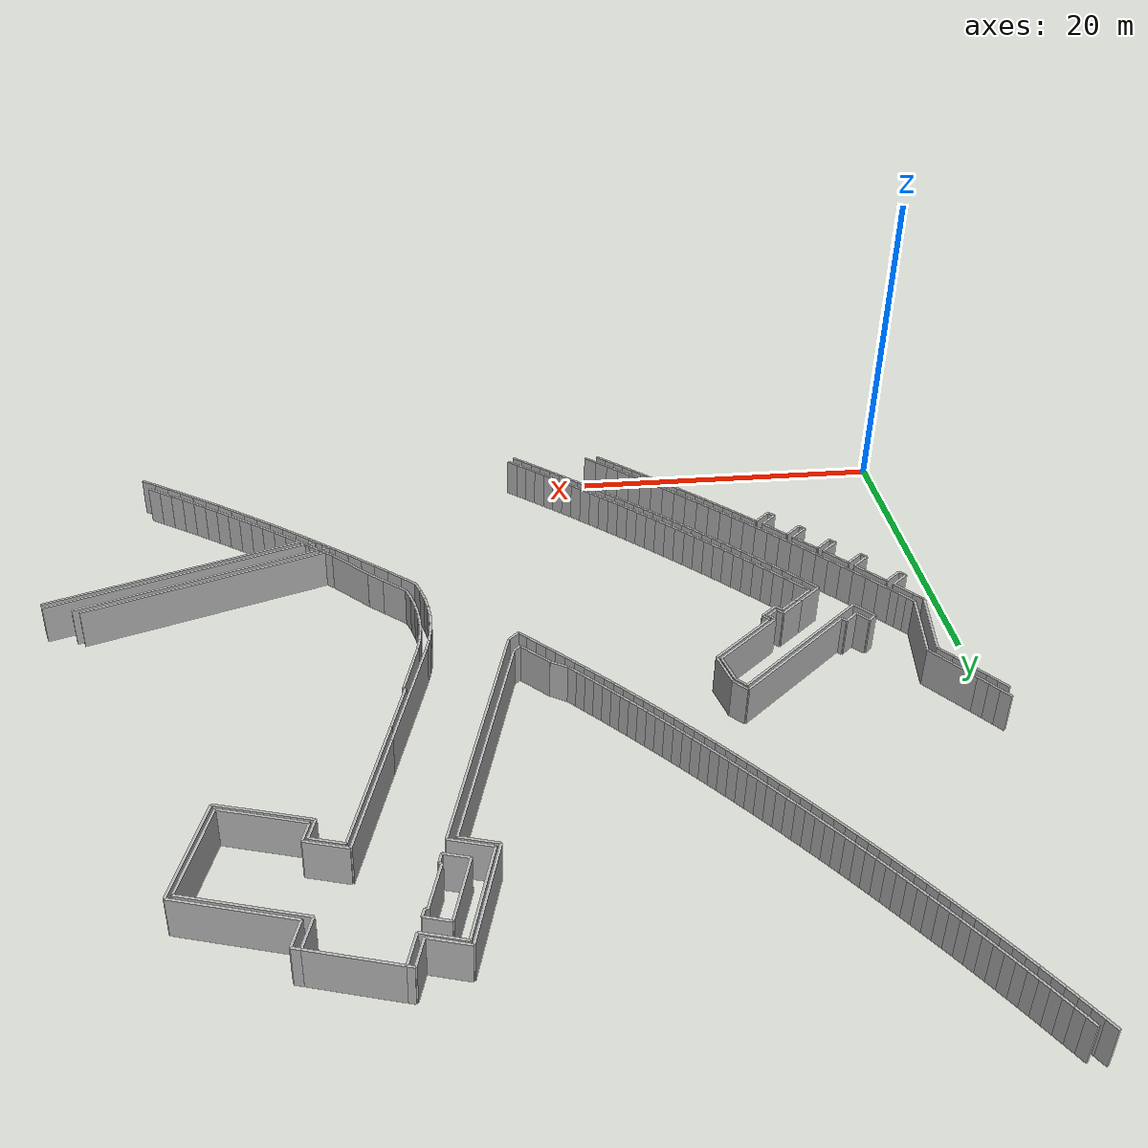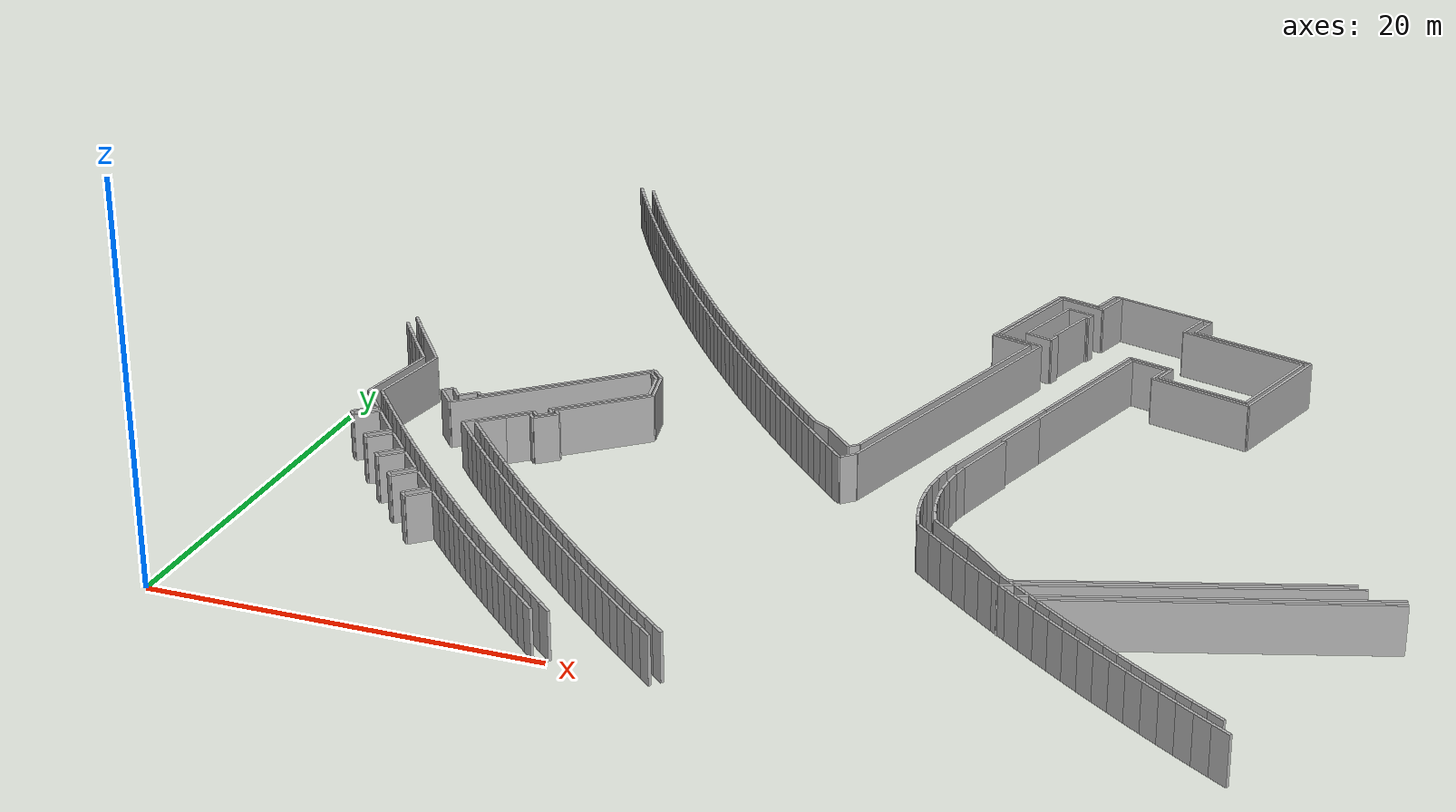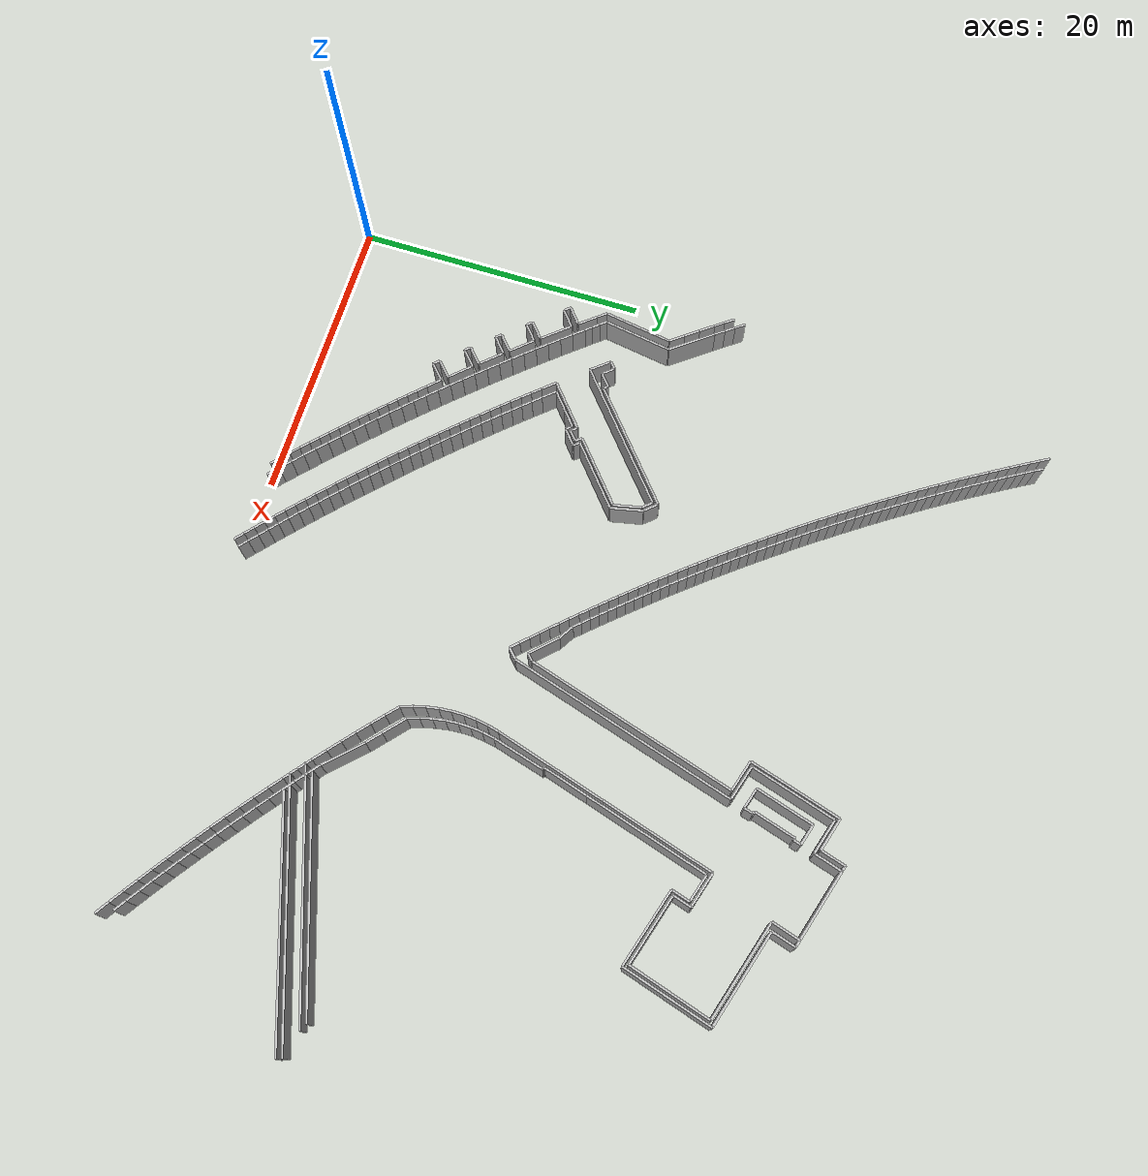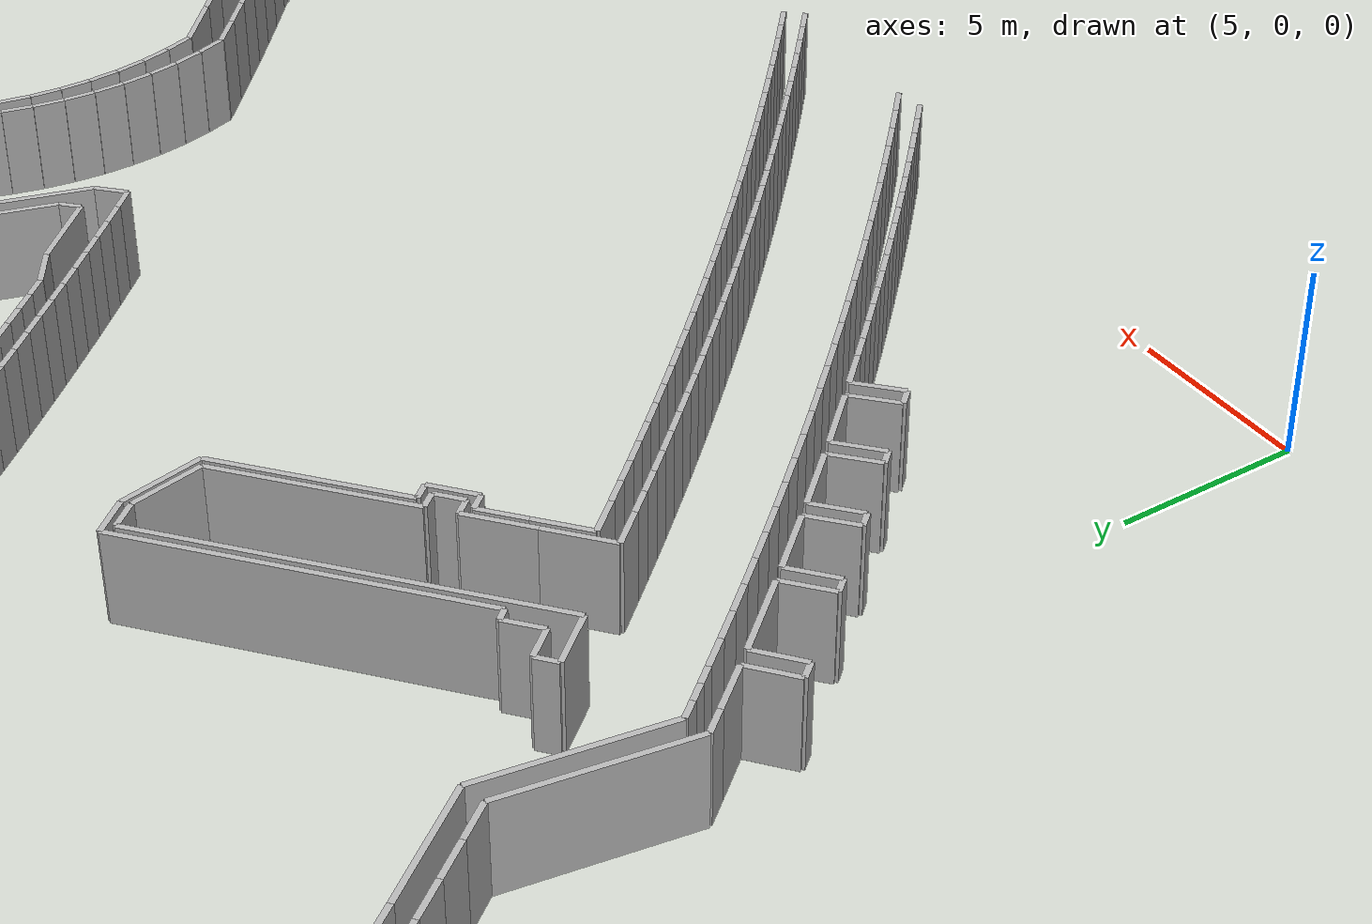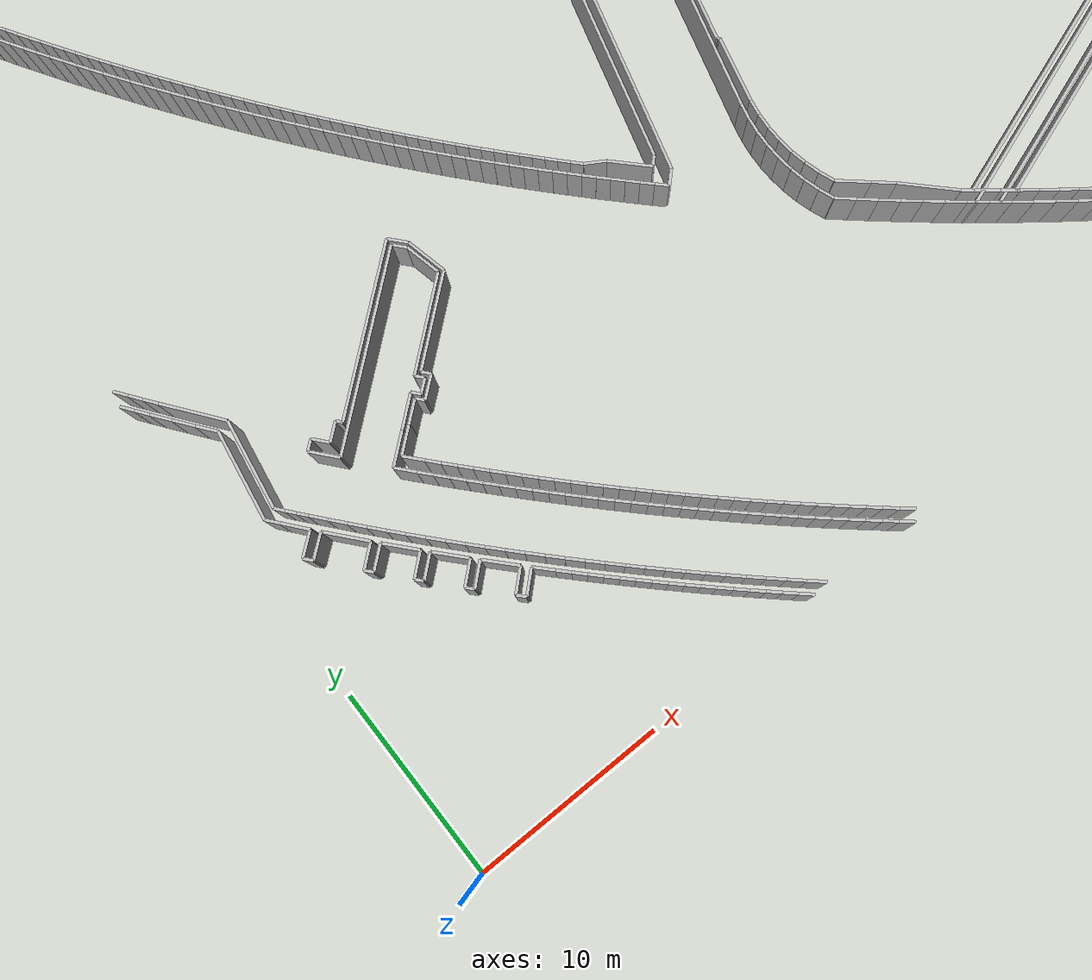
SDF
<?xml version="1.0" ?>
<sdf version="1.6">
  <model name="sps_0201">
    <pose frame="">0 0 0 0 -0 0</pose>
    <static>1</static>
    <self_collide>0</self_collide>
    <allow_auto_disable>0</allow_auto_disable>
    <link name="Wall22">
      <kinematic>0</kinematic>
      <gravity>1</gravity>
      <self_collide>0</self_collide>
      <collision name="collision">
        <geometry>
          <box>
            <size>1.04001 0.15 2.5</size>
          </box>
        </geometry>
        <pose frame="">0 0 0 0 -0 0</pose>
      </collision>
      <visual name="visual">
        <geometry>
          <box>
            <size>1.04001 0.15 2.5</size>
          </box>
        </geometry>
        <pose frame="">0 0 0 0 -0 0</pose>
        <cast_shadows>1</cast_shadows>
        <transparency>0.0</transparency>
      </visual>
      <pose frame="">6.87545 19.8261 1.25 0 -0 0.704597</pose>
    </link>
    <link name="Wall23">
      <kinematic>0</kinematic>
      <gravity>1</gravity>
      <self_collide>0</self_collide>
      <collision name="collision">
        <geometry>
          <box>
            <size>1.85082 0.15 2.5</size>
          </box>
        </geometry>
        <pose frame="">0 0 0 0 -0 0</pose>
      </collision>
      <visual name="visual">
        <geometry>
          <box>
            <size>1.85082 0.15 2.5</size>
          </box>
        </geometry>
        <pose frame="">0 0 0 0 -0 0</pose>
        <cast_shadows>1</cast_shadows>
        <transparency>0.0</transparency>
      </visual>
      <pose frame="">7.62777 11.8847 1.25 0 0 -0.835297</pose>
    </link>
    <link name="Wall24">
      <kinematic>0</kinematic>
      <gravity>1</gravity>
      <self_collide>0</self_collide>
      <collision name="collision">
        <geometry>
          <box>
            <size>1.82676 0.15 2.5</size>
          </box>
        </geometry>
        <pose frame="">0 0 0 0 -0 0</pose>
      </collision>
      <visual name="visual">
        <geometry>
          <box>
            <size>1.82676 0.15 2.5</size>
          </box>
        </geometry>
        <pose frame="">0 0 0 0 -0 0</pose>
        <cast_shadows>1</cast_shadows>
        <transparency>0.0</transparency>
      </visual>
      <pose frame="">8.73775 17.3015 1.25 0 -0 0.704541</pose>
    </link>
    <link name="Wall25">
      <kinematic>0</kinematic>
      <gravity>1</gravity>
      <self_collide>0</self_collide>
      <collision name="collision">
        <geometry>
          <box>
            <size>1.82281 0.15 2.5</size>
          </box>
        </geometry>
        <pose frame="">0 0 0 0 -0 0</pose>
      </collision>
      <visual name="visual">
        <geometry>
          <box>
            <size>1.82281 0.15 2.5</size>
          </box>
        </geometry>
        <pose frame="">0 0 0 0 -0 0</pose>
        <cast_shadows>1</cast_shadows>
        <transparency>0.0</transparency>
      </visual>
      <pose frame="">10.1281 18.4834 1.25 0 -0 0.704541</pose>
    </link>
    <link name="Wall26">
      <kinematic>0</kinematic>
      <gravity>1</gravity>
      <self_collide>0</self_collide>
      <collision name="collision">
        <geometry>
          <box>
            <size>0.491822 0.15 2.5</size>
          </box>
        </geometry>
        <pose frame="">0 0 0 0 -0 0</pose>
      </collision>
      <visual name="visual">
        <geometry>
          <box>
            <size>0.491822 0.15 2.5</size>
          </box>
        </geometry>
        <pose frame="">0 0 0 0 -0 0</pose>
        <cast_shadows>1</cast_shadows>
        <transparency>0.0</transparency>
      </visual>
      <pose frame="">10.9502 18.5315 1.25 0 0 -0.874056</pose>
    </link>
    <link name="Wall27">
      <kinematic>0</kinematic>
      <gravity>1</gravity>
      <self_collide>0</self_collide>
      <collision name="collision">
        <geometry>
          <box>
            <size>0.800107 0.15 2.5</size>
          </box>
        </geometry>
        <pose frame="">0 0 0 0 -0 0</pose>
      </collision>
      <visual name="visual">
        <geometry>
          <box>
            <size>0.800107 0.15 2.5</size>
          </box>
        </geometry>
        <pose frame="">0 0 0 0 -0 0</pose>
        <cast_shadows>1</cast_shadows>
        <transparency>0.0</transparency>
      </visual>
      <pose frame="">11.4463 18.9518 1.25 0 -0 0.696711</pose>
    </link>
    <link name="Wall29">
      <kinematic>0</kinematic>
      <gravity>1</gravity>
      <self_collide>0</self_collide>
      <collision name="collision">
        <geometry>
          <box>
            <size>10.5653 0.15 2.5</size>
          </box>
        </geometry>
        <pose frame="">0 0 0 0 -0 0</pose>
      </collision>
      <visual name="visual">
        <geometry>
          <box>
            <size>10.5653 0.15 2.5</size>
          </box>
        </geometry>
        <pose frame="">0 0 0 0 -0 0</pose>
        <cast_shadows>1</cast_shadows>
        <transparency>0.0</transparency>
      </visual>
      <pose frame="">10.4505 22.0385 1.25 0 -0 0.704572</pose>
    </link>
    <link name="Wall39">
      <kinematic>0</kinematic>
      <gravity>1</gravity>
      <self_collide>0</self_collide>
      <collision name="collision">
        <geometry>
          <box>
            <size>1.96757 0.15 2.5</size>
          </box>
        </geometry>
        <pose frame="">0 0 0 0 -0 0</pose>
      </collision>
      <visual name="visual">
        <geometry>
          <box>
            <size>1.96757 0.15 2.5</size>
          </box>
        </geometry>
        <pose frame="">0 0 0 0 -0 0</pose>
        <cast_shadows>1</cast_shadows>
        <transparency>0.0</transparency>
      </visual>
      <pose frame="">37.9246 35.3446 1.25 0 -0 2.8548</pose>
    </link>
    <link name="Wall402">
      <kinematic>0</kinematic>
      <gravity>1</gravity>
      <self_collide>0</self_collide>
      <collision name="collision">
        <geometry>
          <box>
            <size>1.34944 0.15 2.5</size>
          </box>
        </geometry>
        <pose frame="">0 0 0 0 -0 0</pose>
      </collision>
      <visual name="visual">
        <geometry>
          <box>
            <size>1.34944 0.15 2.5</size>
          </box>
        </geometry>
        <pose frame="">0 0 0 0 -0 0</pose>
        <cast_shadows>1</cast_shadows>
        <transparency>0.0</transparency>
      </visual>
      <pose frame="">2.85216 16.3712 1.25 0 -0 0.687343</pose>
    </link>
    <link name="Wall403">
      <kinematic>0</kinematic>
      <gravity>1</gravity>
      <self_collide>0</self_collide>
      <collision name="collision">
        <geometry>
          <box>
            <size>4.7322 0.15 2.5</size>
          </box>
        </geometry>
        <pose frame="">0 0 0 0 -0 0</pose>
      </collision>
      <visual name="visual">
        <geometry>
          <box>
            <size>4.7322 0.15 2.5</size>
          </box>
        </geometry>
        <pose frame="">0 0 0 0 -0 0</pose>
        <cast_shadows>1</cast_shadows>
        <transparency>0.0</transparency>
      </visual>
      <pose frame="">3.01336 20.9779 1.25 0 0 -1.72778</pose>
    </link>
    <link name="Wall406">
      <kinematic>0</kinematic>
      <gravity>1</gravity>
      <self_collide>0</self_collide>
      <collision name="collision">
        <geometry>
          <box>
            <size>1.35051 0.15 2.5</size>
          </box>
        </geometry>
        <pose frame="">0 0 0 0 -0 0</pose>
      </collision>
      <visual name="visual">
        <geometry>
          <box>
            <size>1.35051 0.15 2.5</size>
          </box>
        </geometry>
        <pose frame="">0 0 0 0 -0 0</pose>
        <cast_shadows>1</cast_shadows>
        <transparency>0.0</transparency>
      </visual>
      <pose frame="">4.68355 14.2057 1.25 0 -0 0.705004</pose>
    </link>
    <link name="Wall407">
      <kinematic>0</kinematic>
      <gravity>1</gravity>
      <self_collide>0</self_collide>
      <collision name="collision">
        <geometry>
          <box>
            <size>1.85036 0.15 2.5</size>
          </box>
        </geometry>
        <pose frame="">0 0 0 0 -0 0</pose>
      </collision>
      <visual name="visual">
        <geometry>
          <box>
            <size>1.85036 0.15 2.5</size>
          </box>
        </geometry>
        <pose frame="">0 0 0 0 -0 0</pose>
        <cast_shadows>1</cast_shadows>
        <transparency>0.0</transparency>
      </visual>
      <pose frame="">6.10006 13.6048 1.25 0 0 -0.849748</pose>
    </link>
    <link name="Wall408">
      <kinematic>0</kinematic>
      <gravity>1</gravity>
      <self_collide>0</self_collide>
      <collision name="collision">
        <geometry>
          <box>
            <size>0.349616 0.15 2.5</size>
          </box>
        </geometry>
        <pose frame="">0 0 0 0 -0 0</pose>
      </collision>
      <visual name="visual">
        <geometry>
          <box>
            <size>0.349616 0.15 2.5</size>
          </box>
        </geometry>
        <pose frame="">0 0 0 0 -0 0</pose>
        <cast_shadows>1</cast_shadows>
        <transparency>0.0</transparency>
      </visual>
      <pose frame="">7.38363 20.0287 1.25 0 -0 2.26621</pose>
    </link>
    <link name="Wall409">
      <kinematic>0</kinematic>
      <gravity>1</gravity>
      <self_collide>0</self_collide>
      <collision name="collision">
        <geometry>
          <box>
            <size>0.499879 0.15 2.5</size>
          </box>
        </geometry>
        <pose frame="">0 0 0 0 -0 0</pose>
      </collision>
      <visual name="visual">
        <geometry>
          <box>
            <size>0.499879 0.15 2.5</size>
          </box>
        </geometry>
        <pose frame="">0 0 0 0 -0 0</pose>
        <cast_shadows>1</cast_shadows>
        <transparency>0.0</transparency>
      </visual>
      <pose frame="">11.5927 19.4002 1.25 0 0 -0.87401</pose>
    </link>
    <link name="Wall412">
      <kinematic>0</kinematic>
      <gravity>1</gravity>
      <self_collide>0</self_collide>
      <collision name="collision">
        <geometry>
          <box>
            <size>1.07775 0.15 2.5</size>
          </box>
        </geometry>
        <pose frame="">0 0 0 0 -0 0</pose>
      </collision>
      <visual name="visual">
        <geometry>
          <box>
            <size>1.07775 0.15 2.5</size>
          </box>
        </geometry>
        <pose frame="">0 0 0 0 -0 0</pose>
        <cast_shadows>1</cast_shadows>
        <transparency>0.0</transparency>
      </visual>
      <pose frame="">14.8383 25.4288 1.25 0 0 -0.857502</pose>
    </link>
    <link name="Wall417">
      <kinematic>0</kinematic>
      <gravity>1</gravity>
      <self_collide>0</self_collide>
      <collision name="collision">
        <geometry>
          <box>
            <size>2.2506 0.15 2.5</size>
          </box>
        </geometry>
        <pose frame="">0 0 0 0 -0 0</pose>
      </collision>
      <visual name="visual">
        <geometry>
          <box>
            <size>2.2506 0.15 2.5</size>
          </box>
        </geometry>
        <pose frame="">0 0 0 0 -0 0</pose>
        <cast_shadows>1</cast_shadows>
        <transparency>0.0</transparency>
      </visual>
      <pose frame="">25.9873 21.5341 1.25 0 -0 2.34037</pose>
    </link>
    <link name="Wall421">
      <kinematic>0</kinematic>
      <gravity>1</gravity>
      <self_collide>0</self_collide>
      <collision name="collision">
        <geometry>
          <box>
            <size>0.887482 0.15 2.5</size>
          </box>
        </geometry>
        <pose frame="">0 0 0 0 -0 0</pose>
      </collision>
      <visual name="visual">
        <geometry>
          <box>
            <size>0.887482 0.15 2.5</size>
          </box>
        </geometry>
        <pose frame="">0 0 0 0 -0 0</pose>
        <cast_shadows>1</cast_shadows>
        <transparency>0.0</transparency>
      </visual>
      <pose frame="">27.0769 19.7676 1.25 0 0 -2.36777</pose>
    </link>
    <link name="Wall422">
      <kinematic>0</kinematic>
      <gravity>1</gravity>
      <self_collide>0</self_collide>
      <collision name="collision">
        <geometry>
          <box>
            <size>2.23408 0.15 2.5</size>
          </box>
        </geometry>
        <pose frame="">0 0 0 0 -0 0</pose>
      </collision>
      <visual name="visual">
        <geometry>
          <box>
            <size>2.23408 0.15 2.5</size>
          </box>
        </geometry>
        <pose frame="">0 0 0 0 -0 0</pose>
        <cast_shadows>1</cast_shadows>
        <transparency>0.0</transparency>
      </visual>
      <pose frame="">30.4044 35.9931 1.25 0 -0 2.85478</pose>
    </link>
    <link name="Wall424">
      <kinematic>0</kinematic>
      <gravity>1</gravity>
      <self_collide>0</self_collide>
      <collision name="collision">
        <geometry>
          <box>
            <size>2.3349 0.15 2.5</size>
          </box>
        </geometry>
        <pose frame="">0 0 0 0 -0 0</pose>
      </collision>
      <visual name="visual">
        <geometry>
          <box>
            <size>2.3349 0.15 2.5</size>
          </box>
        </geometry>
        <pose frame="">0 0 0 0 -0 0</pose>
        <cast_shadows>1</cast_shadows>
        <transparency>0.0</transparency>
      </visual>
      <pose frame="">32.3158 42.2971 1.25 0 0 -0.286752</pose>
    </link>
    <link name="Wall754">
      <kinematic>0</kinematic>
      <gravity>1</gravity>
      <self_collide>0</self_collide>
      <collision name="collision">
        <geometry>
          <box>
            <size>1.34944 0.15 2.5</size>
          </box>
        </geometry>
        <pose frame="">0 0 0 0 -0 0</pose>
      </collision>
      <visual name="visual">
        <geometry>
          <box>
            <size>1.34944 0.15 2.5</size>
          </box>
        </geometry>
        <pose frame="">0 0 0 0 -0 0</pose>
        <cast_shadows>1</cast_shadows>
        <transparency>0.0</transparency>
      </visual>
      <pose frame="">4.97536 13.8625 1.25 0 0 -2.43669</pose>
    </link>
    <link name="Wall1138">
      <kinematic>0</kinematic>
      <gravity>1</gravity>
      <self_collide>0</self_collide>
      <collision name="collision">
        <geometry>
          <box>
            <size>0.4504 0.15 2.5</size>
          </box>
        </geometry>
        <pose frame="">0 0 0 0 -0 0</pose>
      </collision>
      <visual name="visual">
        <geometry>
          <box>
            <size>0.4504 0.15 2.5</size>
          </box>
        </geometry>
        <pose frame="">0 0 0 0 -0 0</pose>
        <cast_shadows>1</cast_shadows>
        <transparency>0.0</transparency>
      </visual>
      <pose frame="">4.31536 13.5967 1.25 0 0 -0.864919</pose>
    </link>
    <link name="Wall1139">
      <kinematic>0</kinematic>
      <gravity>1</gravity>
      <self_collide>0</self_collide>
      <collision name="collision">
        <geometry>
          <box>
            <size>1.34995 0.15 2.5</size>
          </box>
        </geometry>
        <pose frame="">0 0 0 0 -0 0</pose>
      </collision>
      <visual name="visual">
        <geometry>
          <box>
            <size>1.34995 0.15 2.5</size>
          </box>
        </geometry>
        <pose frame="">0 0 0 0 -0 0</pose>
        <cast_shadows>1</cast_shadows>
        <transparency>0.0</transparency>
      </visual>
      <pose frame="">8.04855 10.4127 1.25 0 0 -2.40743</pose>
    </link>
    <link name="Wall1142">
      <kinematic>0</kinematic>
      <gravity>1</gravity>
      <self_collide>0</self_collide>
      <collision name="collision">
        <geometry>
          <box>
            <size>0.500155 0.15 2.5</size>
          </box>
        </geometry>
        <pose frame="">0 0 0 0 -0 0</pose>
      </collision>
      <visual name="visual">
        <geometry>
          <box>
            <size>0.500155 0.15 2.5</size>
          </box>
        </geometry>
        <pose frame="">0 0 0 0 -0 0</pose>
        <cast_shadows>1</cast_shadows>
        <transparency>0.0</transparency>
      </visual>
      <pose frame="">8.99227 8.40669 1.25 0 0 -0.824411</pose>
    </link>
    <link name="Wall1143">
      <kinematic>0</kinematic>
      <gravity>1</gravity>
      <self_collide>0</self_collide>
      <collision name="collision">
        <geometry>
          <box>
            <size>1.0981 0.15 2.5</size>
          </box>
        </geometry>
        <pose frame="">0 0 0 0 -0 0</pose>
      </collision>
      <visual name="visual">
        <geometry>
          <box>
            <size>1.0981 0.15 2.5</size>
          </box>
        </geometry>
        <pose frame="">0 0 0 0 -0 0</pose>
        <cast_shadows>1</cast_shadows>
        <transparency>0.0</transparency>
      </visual>
      <pose frame="">9.02373 16.4959 1.25 0 0 -0.852578</pose>
    </link>
    <link name="Wall1146">
      <kinematic>0</kinematic>
      <gravity>1</gravity>
      <self_collide>0</self_collide>
      <collision name="collision">
        <geometry>
          <box>
            <size>1.85212 0.15 2.5</size>
          </box>
        </geometry>
        <pose frame="">0 0 0 0 -0 0</pose>
      </collision>
      <visual name="visual">
        <geometry>
          <box>
            <size>1.85212 0.15 2.5</size>
          </box>
        </geometry>
        <pose frame="">0 0 0 0 -0 0</pose>
        <cast_shadows>1</cast_shadows>
        <transparency>0.0</transparency>
      </visual>
      <pose frame="">9.18056 10.187 1.25 0 0 -0.821268</pose>
    </link>
    <link name="Wall1147">
      <kinematic>0</kinematic>
      <gravity>1</gravity>
      <self_collide>0</self_collide>
      <collision name="collision">
        <geometry>
          <box>
            <size>1.51884 0.15 2.5</size>
          </box>
        </geometry>
        <pose frame="">0 0 0 0 -0 0</pose>
      </collision>
      <visual name="visual">
        <geometry>
          <box>
            <size>1.51884 0.15 2.5</size>
          </box>
        </geometry>
        <pose frame="">0 0 0 0 -0 0</pose>
        <cast_shadows>1</cast_shadows>
        <transparency>0.0</transparency>
      </visual>
      <pose frame="">9.24103 17.4012 1.25 0 -0 0.704572</pose>
    </link>
    <link name="Wall1148">
      <kinematic>0</kinematic>
      <gravity>1</gravity>
      <self_collide>0</self_collide>
      <collision name="collision">
        <geometry>
          <box>
            <size>1.27685 0.15 2.5</size>
          </box>
        </geometry>
        <pose frame="">0 0 0 0 -0 0</pose>
      </collision>
      <visual name="visual">
        <geometry>
          <box>
            <size>1.27685 0.15 2.5</size>
          </box>
        </geometry>
        <pose frame="">0 0 0 0 -0 0</pose>
        <cast_shadows>1</cast_shadows>
        <transparency>0.0</transparency>
      </visual>
      <pose frame="">10.306 18.3066 1.25 0 -0 0.704572</pose>
    </link>
    <link name="Wall1154">
      <kinematic>0</kinematic>
      <gravity>1</gravity>
      <self_collide>0</self_collide>
      <collision name="collision">
        <geometry>
          <box>
            <size>0.799993 0.15 2.5</size>
          </box>
        </geometry>
        <pose frame="">0 0 0 0 -0 0</pose>
      </collision>
      <visual name="visual">
        <geometry>
          <box>
            <size>0.799993 0.15 2.5</size>
          </box>
        </geometry>
        <pose frame="">0 0 0 0 -0 0</pose>
        <cast_shadows>1</cast_shadows>
        <transparency>0.0</transparency>
      </visual>
      <pose frame="">14.737 25.1576 1.25 0 0 -0.857536</pose>
    </link>
    <link name="Wall1155">
      <kinematic>0</kinematic>
      <gravity>1</gravity>
      <self_collide>0</self_collide>
      <collision name="collision">
        <geometry>
          <box>
            <size>5.08007 0.15 2.5</size>
          </box>
        </geometry>
        <pose frame="">0 0 0 0 -0 0</pose>
      </collision>
      <visual name="visual">
        <geometry>
          <box>
            <size>5.08007 0.15 2.5</size>
          </box>
        </geometry>
        <pose frame="">0 0 0 0 -0 0</pose>
        <cast_shadows>1</cast_shadows>
        <transparency>0.0</transparency>
      </visual>
      <pose frame="">13.7185 21.2074 1.25 0 -0 0.704525</pose>
    </link>
    <link name="Wall1168">
      <kinematic>0</kinematic>
      <gravity>1</gravity>
      <self_collide>0</self_collide>
      <collision name="collision">
        <geometry>
          <box>
            <size>3.67564 0.15 2.5</size>
          </box>
        </geometry>
        <pose frame="">0 0 0 0 -0 0</pose>
      </collision>
      <visual name="visual">
        <geometry>
          <box>
            <size>3.67564 0.15 2.5</size>
          </box>
        </geometry>
        <pose frame="">0 0 0 0 -0 0</pose>
        <cast_shadows>1</cast_shadows>
        <transparency>0.0</transparency>
      </visual>
      <pose frame="">33.1916 22.1685 1.25 0 -0 1.30074</pose>
    </link>
    <link name="Wall1169">
      <kinematic>0</kinematic>
      <gravity>1</gravity>
      <self_collide>0</self_collide>
      <collision name="collision">
        <geometry>
          <box>
            <size>8.11879 0.15 2.5</size>
          </box>
        </geometry>
        <pose frame="">0 0 0 0 -0 0</pose>
      </collision>
      <visual name="visual">
        <geometry>
          <box>
            <size>8.11879 0.15 2.5</size>
          </box>
        </geometry>
        <pose frame="">0 0 0 0 -0 0</pose>
        <cast_shadows>1</cast_shadows>
        <transparency>0.0</transparency>
      </visual>
      <pose frame="">35.6178 32.0543 1.25 0 0 -1.85759</pose>
    </link>
    <link name="Wall1170">
      <kinematic>0</kinematic>
      <gravity>1</gravity>
      <self_collide>0</self_collide>
      <collision name="collision">
        <geometry>
          <box>
            <size>7.94618 0.15 2.5</size>
          </box>
        </geometry>
        <pose frame="">0 0 0 0 -0 0</pose>
      </collision>
      <visual name="visual">
        <geometry>
          <box>
            <size>7.94618 0.15 2.5</size>
          </box>
        </geometry>
        <pose frame="">0 0 0 0 -0 0</pose>
        <cast_shadows>1</cast_shadows>
        <transparency>0.0</transparency>
      </visual>
      <pose frame="">33.3455 24.3499 1.25 0 0 -1.85759</pose>
    </link>
    <link name="Wall1171">
      <kinematic>0</kinematic>
      <gravity>1</gravity>
      <self_collide>0</self_collide>
      <collision name="collision">
        <geometry>
          <box>
            <size>5.53406 0.15 2.5</size>
          </box>
        </geometry>
        <pose frame="">0 0 0 0 -0 0</pose>
      </collision>
      <visual name="visual">
        <geometry>
          <box>
            <size>5.53406 0.15 2.5</size>
          </box>
        </geometry>
        <pose frame="">0 0 0 0 -0 0</pose>
        <cast_shadows>1</cast_shadows>
        <transparency>0.0</transparency>
      </visual>
      <pose frame="">41.1464 33.0091 1.25 0 -0 2.85477</pose>
    </link>
    <link name="Wall1468">
      <kinematic>0</kinematic>
      <gravity>1</gravity>
      <self_collide>0</self_collide>
      <collision name="collision">
        <geometry>
          <box>
            <size>4.75175 0.15 2.5</size>
          </box>
        </geometry>
        <pose frame="">0 0 0 0 -0 0</pose>
      </collision>
      <visual name="visual">
        <geometry>
          <box>
            <size>4.75175 0.15 2.5</size>
          </box>
        </geometry>
        <pose frame="">0 0 0 0 -0 0</pose>
        <cast_shadows>1</cast_shadows>
        <transparency>0.0</transparency>
      </visual>
      <pose frame="">2.38036 20.816 1.25 0 0 -1.72772</pose>
    </link>
    <link name="Wall1470">
      <kinematic>0</kinematic>
      <gravity>1</gravity>
      <self_collide>0</self_collide>
      <collision name="collision">
        <geometry>
          <box>
            <size>1.3495 0.15 2.5</size>
          </box>
        </geometry>
        <pose frame="">0 0 0 0 -0 0</pose>
      </collision>
      <visual name="visual">
        <geometry>
          <box>
            <size>1.3495 0.15 2.5</size>
          </box>
        </geometry>
        <pose frame="">0 0 0 0 -0 0</pose>
        <cast_shadows>1</cast_shadows>
        <transparency>0.0</transparency>
      </visual>
      <pose frame="">3.17013 15.9857 1.25 0 0 -2.4537</pose>
    </link>
    <link name="Wall1471">
      <kinematic>0</kinematic>
      <gravity>1</gravity>
      <self_collide>0</self_collide>
      <collision name="collision">
        <geometry>
          <box>
            <size>0.450705 0.15 2.5</size>
          </box>
        </geometry>
        <pose frame="">0 0 0 0 -0 0</pose>
      </collision>
      <visual name="visual">
        <geometry>
          <box>
            <size>0.450705 0.15 2.5</size>
          </box>
        </geometry>
        <pose frame="">0 0 0 0 -0 0</pose>
        <cast_shadows>1</cast_shadows>
        <transparency>0.0</transparency>
      </visual>
      <pose frame="">7.39626 10.1276 1.25 0 0 -0.835404</pose>
    </link>
    <link name="Wall1472">
      <kinematic>0</kinematic>
      <gravity>1</gravity>
      <self_collide>0</self_collide>
      <collision name="collision">
        <geometry>
          <box>
            <size>1.35059 0.15 2.5</size>
          </box>
        </geometry>
        <pose frame="">0 0 0 0 -0 0</pose>
      </collision>
      <visual name="visual">
        <geometry>
          <box>
            <size>1.35059 0.15 2.5</size>
          </box>
        </geometry>
        <pose frame="">0 0 0 0 -0 0</pose>
        <cast_shadows>1</cast_shadows>
        <transparency>0.0</transparency>
      </visual>
      <pose frame="">7.74688 10.7466 1.25 0 -0 0.733127</pose>
    </link>
    <link name="Wall1473">
      <kinematic>0</kinematic>
      <gravity>1</gravity>
      <self_collide>0</self_collide>
      <collision name="collision">
        <geometry>
          <box>
            <size>1.34996 0.15 2.5</size>
          </box>
        </geometry>
        <pose frame="">0 0 0 0 -0 0</pose>
      </collision>
      <visual name="visual">
        <geometry>
          <box>
            <size>1.34996 0.15 2.5</size>
          </box>
        </geometry>
        <pose frame="">0 0 0 0 -0 0</pose>
        <cast_shadows>1</cast_shadows>
        <transparency>0.0</transparency>
      </visual>
      <pose frame="">9.31698 9.0497 1.25 0 -0 0.748624</pose>
    </link>
    <link name="Wall1474">
      <kinematic>0</kinematic>
      <gravity>1</gravity>
      <self_collide>0</self_collide>
      <collision name="collision">
        <geometry>
          <box>
            <size>0.500044 0.15 2.5</size>
          </box>
        </geometry>
        <pose frame="">0 0 0 0 -0 0</pose>
      </collision>
      <visual name="visual">
        <geometry>
          <box>
            <size>0.500044 0.15 2.5</size>
          </box>
        </geometry>
        <pose frame="">0 0 0 0 -0 0</pose>
        <cast_shadows>1</cast_shadows>
        <transparency>0.0</transparency>
      </visual>
      <pose frame="">10.9789 18.8868 1.25 0 0 -0.873808</pose>
    </link>
    <link name="Wall1484">
      <kinematic>0</kinematic>
      <gravity>1</gravity>
      <self_collide>0</self_collide>
      <collision name="collision">
        <geometry>
          <box>
            <size>0.581381 0.15 2.5</size>
          </box>
        </geometry>
        <pose frame="">0 0 0 0 -0 0</pose>
      </collision>
      <visual name="visual">
        <geometry>
          <box>
            <size>0.581381 0.15 2.5</size>
          </box>
        </geometry>
        <pose frame="">0 0 0 0 -0 0</pose>
        <cast_shadows>1</cast_shadows>
        <transparency>0.0</transparency>
      </visual>
      <pose frame="">26.9782 20.9291 1.25 0 0 -2.36763</pose>
    </link>
    <link name="Wall1486">
      <kinematic>0</kinematic>
      <gravity>1</gravity>
      <self_collide>0</self_collide>
      <collision name="collision">
        <geometry>
          <box>
            <size>15.1642 0.15 2.5</size>
          </box>
        </geometry>
        <pose frame="">0 0 0 0 -0 0</pose>
      </collision>
      <visual name="visual">
        <geometry>
          <box>
            <size>15.1642 0.15 2.5</size>
          </box>
        </geometry>
        <pose frame="">0 0 0 0 -0 0</pose>
        <cast_shadows>1</cast_shadows>
        <transparency>0.0</transparency>
      </visual>
      <pose frame="">29.331 28.4047 1.25 0 -0 1.28399</pose>
    </link>
    <link name="Wall1488">
      <kinematic>0</kinematic>
      <gravity>1</gravity>
      <self_collide>0</self_collide>
      <collision name="collision">
        <geometry>
          <box>
            <size>1.32867 0.15 2.5</size>
          </box>
        </geometry>
        <pose frame="">0 0 0 0 -0 0</pose>
      </collision>
      <visual name="visual">
        <geometry>
          <box>
            <size>1.32867 0.15 2.5</size>
          </box>
        </geometry>
        <pose frame="">0 0 0 0 -0 0</pose>
        <cast_shadows>1</cast_shadows>
        <transparency>0.0</transparency>
      </visual>
      <pose frame="">38.6804 34.4291 1.25 0 -0 1.28405</pose>
    </link>
    <link name="Wall1764">
      <kinematic>0</kinematic>
      <gravity>1</gravity>
      <self_collide>0</self_collide>
      <collision name="collision">
        <geometry>
          <box>
            <size>0.914482 0.15 2.5</size>
          </box>
        </geometry>
        <pose frame="">0 0 0 0 -0 0</pose>
      </collision>
      <visual name="visual">
        <geometry>
          <box>
            <size>0.914482 0.15 2.5</size>
          </box>
        </geometry>
        <pose frame="">0 0 0 0 -0 0</pose>
        <cast_shadows>1</cast_shadows>
        <transparency>0.0</transparency>
      </visual>
      <pose frame="">6.18636 19.8404 1.25 0 -0 2.26607</pose>
    </link>
    <link name="Wall1765">
      <kinematic>0</kinematic>
      <gravity>1</gravity>
      <self_collide>0</self_collide>
      <collision name="collision">
        <geometry>
          <box>
            <size>1.34981 0.15 2.5</size>
          </box>
        </geometry>
        <pose frame="">0 0 0 0 -0 0</pose>
      </collision>
      <visual name="visual">
        <geometry>
          <box>
            <size>1.34981 0.15 2.5</size>
          </box>
        </geometry>
        <pose frame="">0 0 0 0 -0 0</pose>
        <cast_shadows>1</cast_shadows>
        <transparency>0.0</transparency>
      </visual>
      <pose frame="">6.20324 12.4651 1.25 0 -0 0.719549</pose>
    </link>
    <link name="Wall1770">
      <kinematic>0</kinematic>
      <gravity>1</gravity>
      <self_collide>0</self_collide>
      <collision name="collision">
        <geometry>
          <box>
            <size>9.17421 0.15 2.5</size>
          </box>
        </geometry>
        <pose frame="">0 0 0 0 -0 0</pose>
      </collision>
      <visual name="visual">
        <geometry>
          <box>
            <size>9.17421 0.15 2.5</size>
          </box>
        </geometry>
        <pose frame="">0 0 0 0 -0 0</pose>
        <cast_shadows>1</cast_shadows>
        <transparency>0.0</transparency>
      </visual>
      <pose frame="">10.9907 22.8654 1.25 0 -0 0.704518</pose>
    </link>
    <link name="Wall1772">
      <kinematic>0</kinematic>
      <gravity>1</gravity>
      <self_collide>0</self_collide>
      <collision name="collision">
        <geometry>
          <box>
            <size>1.93117 0.15 2.5</size>
          </box>
        </geometry>
        <pose frame="">0 0 0 0 -0 0</pose>
      </collision>
      <visual name="visual">
        <geometry>
          <box>
            <size>1.93117 0.15 2.5</size>
          </box>
        </geometry>
        <pose frame="">0 0 0 0 -0 0</pose>
        <cast_shadows>1</cast_shadows>
        <transparency>0.0</transparency>
      </visual>
      <pose frame="">15.2003 23.9108 1.25 0 0 -1.36046</pose>
    </link>
    <link name="Wall1782">
      <kinematic>0</kinematic>
      <gravity>1</gravity>
      <self_collide>0</self_collide>
      <collision name="collision">
        <geometry>
          <box>
            <size>6.58713 0.15 2.5</size>
          </box>
        </geometry>
        <pose frame="">0 0 0 0 -0 0</pose>
      </collision>
      <visual name="visual">
        <geometry>
          <box>
            <size>6.58713 0.15 2.5</size>
          </box>
        </geometry>
        <pose frame="">0 0 0 0 -0 0</pose>
        <cast_shadows>1</cast_shadows>
        <transparency>0.0</transparency>
      </visual>
      <pose frame="">30.2645 39.4682 1.25 0 -0 1.28405</pose>
    </link>
    <link name="Wall1783">
      <kinematic>0</kinematic>
      <gravity>1</gravity>
      <self_collide>0</self_collide>
      <collision name="collision">
        <geometry>
          <box>
            <size>1.76891 0.15 2.5</size>
          </box>
        </geometry>
        <pose frame="">0 0 0 0 -0 0</pose>
      </collision>
      <visual name="visual">
        <geometry>
          <box>
            <size>1.76891 0.15 2.5</size>
          </box>
        </geometry>
        <pose frame="">0 0 0 0 -0 0</pose>
        <cast_shadows>1</cast_shadows>
        <transparency>0.0</transparency>
      </visual>
      <pose frame="">33.6859 42.8152 1.25 0 -0 1.28387</pose>
    </link>
    <link name="Wall1784">
      <kinematic>0</kinematic>
      <gravity>1</gravity>
      <self_collide>0</self_collide>
      <collision name="collision">
        <geometry>
          <box>
            <size>0.397031 0.15 2.5</size>
          </box>
        </geometry>
        <pose frame="">0 0 0 0 -0 0</pose>
      </collision>
      <visual name="visual">
        <geometry>
          <box>
            <size>0.397031 0.15 2.5</size>
          </box>
        </geometry>
        <pose frame="">0 0 0 0 -0 0</pose>
        <cast_shadows>1</cast_shadows>
        <transparency>0.0</transparency>
      </visual>
      <pose frame="">34.1266 43.6073 1.25 0 0 -0.286936</pose>
    </link>
    <link name="Wall1785">
      <kinematic>0</kinematic>
      <gravity>1</gravity>
      <self_collide>0</self_collide>
      <collision name="collision">
        <geometry>
          <box>
            <size>3.11157 0.15 2.5</size>
          </box>
        </geometry>
        <pose frame="">0 0 0 0 -0 0</pose>
      </collision>
      <visual name="visual">
        <geometry>
          <box>
            <size>3.11157 0.15 2.5</size>
          </box>
        </geometry>
        <pose frame="">0 0 0 0 -0 0</pose>
        <cast_shadows>1</cast_shadows>
        <transparency>0.0</transparency>
      </visual>
      <pose frame="">36.4737 11.5634 1.25 0 0 -0.795454</pose>
    </link>
    <link name="Wall2098">
      <kinematic>0</kinematic>
      <gravity>1</gravity>
      <self_collide>0</self_collide>
      <collision name="collision">
        <geometry>
          <box>
            <size>2.32488 0.15 2.5</size>
          </box>
        </geometry>
        <pose frame="">0 0 0 0 -0 0</pose>
      </collision>
      <visual name="visual">
        <geometry>
          <box>
            <size>2.32488 0.15 2.5</size>
          </box>
        </geometry>
        <pose frame="">0 0 0 0 -0 0</pose>
        <cast_shadows>1</cast_shadows>
        <transparency>0.0</transparency>
      </visual>
      <pose frame="">4.44463 15.5287 1.25 0 0 -0.865903</pose>
    </link>
    <link name="Wall2099">
      <kinematic>0</kinematic>
      <gravity>1</gravity>
      <self_collide>0</self_collide>
      <collision name="collision">
        <geometry>
          <box>
            <size>0.600053 0.15 2.5</size>
          </box>
        </geometry>
        <pose frame="">0 0 0 0 -0 0</pose>
      </collision>
      <visual name="visual">
        <geometry>
          <box>
            <size>0.600053 0.15 2.5</size>
          </box>
        </geometry>
        <pose frame="">0 0 0 0 -0 0</pose>
        <cast_shadows>1</cast_shadows>
        <transparency>0.0</transparency>
      </visual>
      <pose frame="">5.66125 20.0016 1.25 0 -0 0.704467</pose>
    </link>
    <link name="Wall2100">
      <kinematic>0</kinematic>
      <gravity>1</gravity>
      <self_collide>0</self_collide>
      <collision name="collision">
        <geometry>
          <box>
            <size>0.449065 0.15 2.5</size>
          </box>
        </geometry>
        <pose frame="">0 0 0 0 -0 0</pose>
      </collision>
      <visual name="visual">
        <geometry>
          <box>
            <size>0.449065 0.15 2.5</size>
          </box>
        </geometry>
        <pose frame="">0 0 0 0 -0 0</pose>
        <cast_shadows>1</cast_shadows>
        <transparency>0.0</transparency>
      </visual>
      <pose frame="">5.84325 11.8511 1.25 0 0 -0.853398</pose>
    </link>
    <link name="Wall2101">
      <kinematic>0</kinematic>
      <gravity>1</gravity>
      <self_collide>0</self_collide>
      <collision name="collision">
        <geometry>
          <box>
            <size>1.5502 0.15 2.5</size>
          </box>
        </geometry>
        <pose frame="">0 0 0 0 -0 0</pose>
      </collision>
      <visual name="visual">
        <geometry>
          <box>
            <size>1.5502 0.15 2.5</size>
          </box>
        </geometry>
        <pose frame="">0 0 0 0 -0 0</pose>
        <cast_shadows>1</cast_shadows>
        <transparency>0.0</transparency>
      </visual>
      <pose frame="">5.92916 19.2121 1.25 0 -0 2.26606</pose>
    </link>
    <link name="Wall2102">
      <kinematic>0</kinematic>
      <gravity>1</gravity>
      <self_collide>0</self_collide>
      <collision name="collision">
        <geometry>
          <box>
            <size>1.35001 0.15 2.5</size>
          </box>
        </geometry>
        <pose frame="">0 0 0 0 -0 0</pose>
      </collision>
      <visual name="visual">
        <geometry>
          <box>
            <size>1.35001 0.15 2.5</size>
          </box>
        </geometry>
        <pose frame="">0 0 0 0 -0 0</pose>
        <cast_shadows>1</cast_shadows>
        <transparency>0.0</transparency>
      </visual>
      <pose frame="">6.49886 12.1264 1.25 0 0 -2.42277</pose>
    </link>
    <link name="Wall2104">
      <kinematic>0</kinematic>
      <gravity>1</gravity>
      <self_collide>0</self_collide>
      <collision name="collision">
        <geometry>
          <box>
            <size>1.30009 0.15 2.5</size>
          </box>
        </geometry>
        <pose frame="">0 0 0 0 -0 0</pose>
      </collision>
      <visual name="visual">
        <geometry>
          <box>
            <size>1.30009 0.15 2.5</size>
          </box>
        </geometry>
        <pose frame="">0 0 0 0 -0 0</pose>
        <cast_shadows>1</cast_shadows>
        <transparency>0.0</transparency>
      </visual>
      <pose frame="">11.6067 18.76 1.25 0 -0 0.696614</pose>
    </link>
    <link name="Wall2105">
      <kinematic>0</kinematic>
      <gravity>1</gravity>
      <self_collide>0</self_collide>
      <collision name="collision">
        <geometry>
          <box>
            <size>0.502067 0.15 2.5</size>
          </box>
        </geometry>
        <pose frame="">0 0 0 0 -0 0</pose>
      </collision>
      <visual name="visual">
        <geometry>
          <box>
            <size>0.502067 0.15 2.5</size>
          </box>
        </geometry>
        <pose frame="">0 0 0 0 -0 0</pose>
        <cast_shadows>1</cast_shadows>
        <transparency>0.0</transparency>
      </visual>
      <pose frame="">11.9442 19.3697 1.25 0 0 -0.874486</pose>
    </link>
    <link name="Wall2106">
      <kinematic>0</kinematic>
      <gravity>1</gravity>
      <self_collide>0</self_collide>
      <collision name="collision">
        <geometry>
          <box>
            <size>2.21768 0.15 2.5</size>
          </box>
        </geometry>
        <pose frame="">0 0 0 0 -0 0</pose>
      </collision>
      <visual name="visual">
        <geometry>
          <box>
            <size>2.21768 0.15 2.5</size>
          </box>
        </geometry>
        <pose frame="">0 0 0 0 -0 0</pose>
        <cast_shadows>1</cast_shadows>
        <transparency>0.0</transparency>
      </visual>
      <pose frame="">15.4224 23.9369 1.25 0 0 -1.36049</pose>
    </link>
    <link name="Wall2114">
      <kinematic>0</kinematic>
      <gravity>1</gravity>
      <self_collide>0</self_collide>
      <collision name="collision">
        <geometry>
          <box>
            <size>1.13538 0.15 2.5</size>
          </box>
        </geometry>
        <pose frame="">0 0 0 0 -0 0</pose>
      </collision>
      <visual name="visual">
        <geometry>
          <box>
            <size>1.13538 0.15 2.5</size>
          </box>
        </geometry>
        <pose frame="">0 0 0 0 -0 0</pose>
        <cast_shadows>1</cast_shadows>
        <transparency>0.0</transparency>
      </visual>
      <pose frame="">24.719 22.637 1.25 0 -0 2.59575</pose>
    </link>
    <link name="Wall2121">
      <kinematic>0</kinematic>
      <gravity>1</gravity>
      <self_collide>0</self_collide>
      <collision name="collision">
        <geometry>
          <box>
            <size>0.132901 0.15 2.5</size>
          </box>
        </geometry>
        <pose frame="">0 0 0 0 -0 0</pose>
      </collision>
      <visual name="visual">
        <geometry>
          <box>
            <size>0.132901 0.15 2.5</size>
          </box>
        </geometry>
        <pose frame="">0 0 0 0 -0 0</pose>
        <cast_shadows>1</cast_shadows>
        <transparency>0.0</transparency>
      </visual>
      <pose frame="">33.6157 23.9465 1.25 0 -0 3.039</pose>
    </link>
    <link name="Wall2122">
      <kinematic>0</kinematic>
      <gravity>1</gravity>
      <self_collide>0</self_collide>
      <collision name="collision">
        <geometry>
          <box>
            <size>3.26043 0.15 2.5</size>
          </box>
        </geometry>
        <pose frame="">0 0 0 0 -0 0</pose>
      </collision>
      <visual name="visual">
        <geometry>
          <box>
            <size>3.26043 0.15 2.5</size>
          </box>
        </geometry>
        <pose frame="">0 0 0 0 -0 0</pose>
        <cast_shadows>1</cast_shadows>
        <transparency>0.0</transparency>
      </visual>
      <pose frame="">34.0095 25.5173 1.25 0 -0 1.2848</pose>
    </link>
    <link name="Wall2123">
      <kinematic>0</kinematic>
      <gravity>1</gravity>
      <self_collide>0</self_collide>
      <collision name="collision">
        <geometry>
          <box>
            <size>8.87608 0.15 2.5</size>
          </box>
        </geometry>
        <pose frame="">0 0 0 0 -0 0</pose>
      </collision>
      <visual name="visual">
        <geometry>
          <box>
            <size>8.87608 0.15 2.5</size>
          </box>
        </geometry>
        <pose frame="">0 0 0 0 -0 0</pose>
        <cast_shadows>1</cast_shadows>
        <transparency>0.0</transparency>
      </visual>
      <pose frame="">35.7215 31.3391 1.25 0 -0 1.2848</pose>
    </link>
    <link name="Wall2128">
      <kinematic>0</kinematic>
      <gravity>1</gravity>
      <self_collide>0</self_collide>
      <collision name="collision">
        <geometry>
          <box>
            <size>6.79757 0.15 2.5</size>
          </box>
        </geometry>
        <pose frame="">0 0 0 0 -0 0</pose>
      </collision>
      <visual name="visual">
        <geometry>
          <box>
            <size>6.79757 0.15 2.5</size>
          </box>
        </geometry>
        <pose frame="">0 0 0 0 -0 0</pose>
        <cast_shadows>1</cast_shadows>
        <transparency>0.0</transparency>
      </visual>
      <pose frame="">42.3707 39.3935 1.25 0 0 -0.286779</pose>
    </link>
    <link name="Wall2478">
      <kinematic>0</kinematic>
      <gravity>1</gravity>
      <self_collide>0</self_collide>
      <collision name="collision">
        <geometry>
          <box>
            <size>0.50008 0.15 2.5</size>
          </box>
        </geometry>
        <pose frame="">0 0 0 0 -0 0</pose>
      </collision>
      <visual name="visual">
        <geometry>
          <box>
            <size>0.50008 0.15 2.5</size>
          </box>
        </geometry>
        <pose frame="">0 0 0 0 -0 0</pose>
        <cast_shadows>1</cast_shadows>
        <transparency>0.0</transparency>
      </visual>
      <pose frame="">2.48974 15.7502 1.25 0 0 -0.881168</pose>
    </link>
    <link name="Wall2479">
      <kinematic>0</kinematic>
      <gravity>1</gravity>
      <self_collide>0</self_collide>
      <collision name="collision">
        <geometry>
          <box>
            <size>0.74414 0.15 2.5</size>
          </box>
        </geometry>
        <pose frame="">0 0 0 0 -0 0</pose>
      </collision>
      <visual name="visual">
        <geometry>
          <box>
            <size>0.74414 0.15 2.5</size>
          </box>
        </geometry>
        <pose frame="">0 0 0 0 -0 0</pose>
        <cast_shadows>1</cast_shadows>
        <transparency>0.0</transparency>
      </visual>
      <pose frame="">2.24448 18.1812 1.25 0 0 -0.885704</pose>
    </link>
    <link name="Wall2480">
      <kinematic>0</kinematic>
      <gravity>1</gravity>
      <self_collide>0</self_collide>
      <collision name="collision">
        <geometry>
          <box>
            <size>1.41253 0.15 2.5</size>
          </box>
        </geometry>
        <pose frame="">0 0 0 0 -0 0</pose>
      </collision>
      <visual name="visual">
        <geometry>
          <box>
            <size>1.41253 0.15 2.5</size>
          </box>
        </geometry>
        <pose frame="">0 0 0 0 -0 0</pose>
        <cast_shadows>1</cast_shadows>
        <transparency>0.0</transparency>
      </visual>
      <pose frame="">2.92679 17.3462 1.25 0 0 -0.885704</pose>
    </link>
    <link name="Wall2481">
      <kinematic>0</kinematic>
      <gravity>1</gravity>
      <self_collide>0</self_collide>
      <collision name="collision">
        <geometry>
          <box>
            <size>1.35039 0.15 2.5</size>
          </box>
        </geometry>
        <pose frame="">0 0 0 0 -0 0</pose>
      </collision>
      <visual name="visual">
        <geometry>
          <box>
            <size>1.35039 0.15 2.5</size>
          </box>
        </geometry>
        <pose frame="">0 0 0 0 -0 0</pose>
        <cast_shadows>1</cast_shadows>
        <transparency>0.0</transparency>
      </visual>
      <pose frame="">9.65716 8.6822 1.25 0 0 -2.39388</pose>
    </link>
    <link name="Wall2485">
      <kinematic>0</kinematic>
      <gravity>1</gravity>
      <self_collide>0</self_collide>
      <collision name="collision">
        <geometry>
          <box>
            <size>5.21017 0.15 2.5</size>
          </box>
        </geometry>
        <pose frame="">0 0 0 0 -0 0</pose>
      </collision>
      <visual name="visual">
        <geometry>
          <box>
            <size>5.21017 0.15 2.5</size>
          </box>
        </geometry>
        <pose frame="">0 0 0 0 -0 0</pose>
        <cast_shadows>1</cast_shadows>
        <transparency>0.0</transparency>
      </visual>
      <pose frame="">13.4171 21.2792 1.25 0 -0 0.704563</pose>
    </link>
    <link name="Wall2503">
      <kinematic>0</kinematic>
      <gravity>1</gravity>
      <self_collide>0</self_collide>
      <collision name="collision">
        <geometry>
          <box>
            <size>4.13837 0.15 2.5</size>
          </box>
        </geometry>
        <pose frame="">0 0 0 0 -0 0</pose>
      </collision>
      <visual name="visual">
        <geometry>
          <box>
            <size>4.13837 0.15 2.5</size>
          </box>
        </geometry>
        <pose frame="">0 0 0 0 -0 0</pose>
        <cast_shadows>1</cast_shadows>
        <transparency>0.0</transparency>
      </visual>
      <pose frame="">31.4722 39.1296 1.25 0 0 -1.85757</pose>
    </link>
    <link name="Wall2504">
      <kinematic>0</kinematic>
      <gravity>1</gravity>
      <self_collide>0</self_collide>
      <collision name="collision">
        <geometry>
          <box>
            <size>1.47778 0.15 2.5</size>
          </box>
        </geometry>
        <pose frame="">0 0 0 0 -0 0</pose>
      </collision>
      <visual name="visual">
        <geometry>
          <box>
            <size>1.47778 0.15 2.5</size>
          </box>
        </geometry>
        <pose frame="">0 0 0 0 -0 0</pose>
        <cast_shadows>1</cast_shadows>
        <transparency>0.0</transparency>
      </visual>
      <pose frame="">31.5956 36.9359 1.25 0 0 -0.286793</pose>
    </link>
    <link name="Wall2507">
      <kinematic>0</kinematic>
      <gravity>1</gravity>
      <self_collide>0</self_collide>
      <collision name="collision">
        <geometry>
          <box>
            <size>1.78191 0.15 2.5</size>
          </box>
        </geometry>
        <pose frame="">0 0 0 0 -0 0</pose>
      </collision>
      <visual name="visual">
        <geometry>
          <box>
            <size>1.78191 0.15 2.5</size>
          </box>
        </geometry>
        <pose frame="">0 0 0 0 -0 0</pose>
        <cast_shadows>1</cast_shadows>
        <transparency>0.0</transparency>
      </visual>
      <pose frame="">33.8 14.0663 1.25 0 0 -0.720717</pose>
    </link>
    <link name="Wall2508">
      <kinematic>0</kinematic>
      <gravity>1</gravity>
      <self_collide>0</self_collide>
      <collision name="collision">
        <geometry>
          <box>
            <size>1.21813 0.15 2.5</size>
          </box>
        </geometry>
        <pose frame="">0 0 0 0 -0 0</pose>
      </collision>
      <visual name="visual">
        <geometry>
          <box>
            <size>1.21813 0.15 2.5</size>
          </box>
        </geometry>
        <pose frame="">0 0 0 0 -0 0</pose>
        <cast_shadows>1</cast_shadows>
        <transparency>0.0</transparency>
      </visual>
      <pose frame="">34.9271 13.0765 1.25 0 0 -0.720717</pose>
    </link>
    <link name="Wall2509">
      <kinematic>0</kinematic>
      <gravity>1</gravity>
      <self_collide>0</self_collide>
      <collision name="collision">
        <geometry>
          <box>
            <size>1.70988 0.15 2.5</size>
          </box>
        </geometry>
        <pose frame="">0 0 0 0 -0 0</pose>
      </collision>
      <visual name="visual">
        <geometry>
          <box>
            <size>1.70988 0.15 2.5</size>
          </box>
        </geometry>
        <pose frame="">0 0 0 0 -0 0</pose>
        <cast_shadows>1</cast_shadows>
        <transparency>0.0</transparency>
      </visual>
      <pose frame="">39.3526 41.1749 1.25 0 0 -1.85764</pose>
    </link>
    <link name="Wall2510">
      <kinematic>0</kinematic>
      <gravity>1</gravity>
      <self_collide>0</self_collide>
      <collision name="collision">
        <geometry>
          <box>
            <size>0.502075 0.15 2.5</size>
          </box>
        </geometry>
        <pose frame="">0 0 0 0 -0 0</pose>
      </collision>
      <visual name="visual">
        <geometry>
          <box>
            <size>0.502075 0.15 2.5</size>
          </box>
        </geometry>
        <pose frame="">0 0 0 0 -0 0</pose>
        <cast_shadows>1</cast_shadows>
        <transparency>0.0</transparency>
      </visual>
      <pose frame="">39.3537 42.0659 1.25 0 0 -0.286799</pose>
    </link>
    <link name="Wall2512">
      <kinematic>0</kinematic>
      <gravity>1</gravity>
      <self_collide>0</self_collide>
      <collision name="collision">
        <geometry>
          <box>
            <size>6.47006 0.15 2.5</size>
          </box>
        </geometry>
        <pose frame="">0 0 0 0 -0 0</pose>
      </collision>
      <visual name="visual">
        <geometry>
          <box>
            <size>6.47006 0.15 2.5</size>
          </box>
        </geometry>
        <pose frame="">0 0 0 0 -0 0</pose>
        <cast_shadows>1</cast_shadows>
        <transparency>0.0</transparency>
      </visual>
      <pose frame="">44.7155 35.3292 1.25 0 0 -1.85758</pose>
    </link>
    <link name="Wall6499">
      <kinematic>0</kinematic>
      <gravity>1</gravity>
      <self_collide>0</self_collide>
      <collision name="collision">
        <geometry>
          <box>
            <size>1.09956 0.15 2.5</size>
          </box>
        </geometry>
        <pose frame="">0 0 0 0 -0 0</pose>
      </collision>
      <visual name="visual">
        <geometry>
          <box>
            <size>1.09956 0.15 2.5</size>
          </box>
        </geometry>
        <pose frame="">0 0 0 0 -0 0</pose>
        <cast_shadows>1</cast_shadows>
        <transparency>0.0</transparency>
      </visual>
      <pose frame="">10.5354 8.74699 1.25 0 0 -0.810875</pose>
    </link>
    <link name="Wall6500">
      <kinematic>0</kinematic>
      <gravity>1</gravity>
      <self_collide>0</self_collide>
      <collision name="collision">
        <geometry>
          <box>
            <size>0.732971 0.15 2.5</size>
          </box>
        </geometry>
        <pose frame="">0 0 0 0 -0 0</pose>
      </collision>
      <visual name="visual">
        <geometry>
          <box>
            <size>0.732971 0.15 2.5</size>
          </box>
        </geometry>
        <pose frame="">0 0 0 0 -0 0</pose>
        <cast_shadows>1</cast_shadows>
        <transparency>0.0</transparency>
      </visual>
      <pose frame="">11.1681 8.08427 1.25 0 0 -0.805066</pose>
    </link>
    <link name="Wall6501">
      <kinematic>0</kinematic>
      <gravity>1</gravity>
      <self_collide>0</self_collide>
      <collision name="collision">
        <geometry>
          <box>
            <size>0.733048 0.15 2.5</size>
          </box>
        </geometry>
        <pose frame="">0 0 0 0 -0 0</pose>
      </collision>
      <visual name="visual">
        <geometry>
          <box>
            <size>0.733048 0.15 2.5</size>
          </box>
        </geometry>
        <pose frame="">0 0 0 0 -0 0</pose>
        <cast_shadows>1</cast_shadows>
        <transparency>0.0</transparency>
      </visual>
      <pose frame="">11.6772 7.5569 1.25 0 0 -0.801001</pose>
    </link>
    <link name="Wall6502">
      <kinematic>0</kinematic>
      <gravity>1</gravity>
      <self_collide>0</self_collide>
      <collision name="collision">
        <geometry>
          <box>
            <size>0.733 0.15 2.5</size>
          </box>
        </geometry>
        <pose frame="">0 0 0 0 -0 0</pose>
      </collision>
      <visual name="visual">
        <geometry>
          <box>
            <size>0.733 0.15 2.5</size>
          </box>
        </geometry>
        <pose frame="">0 0 0 0 -0 0</pose>
        <cast_shadows>1</cast_shadows>
        <transparency>0.0</transparency>
      </visual>
      <pose frame="">12.1887 7.03181 1.25 0 0 -0.796055</pose>
    </link>
    <link name="Wall6503">
      <kinematic>0</kinematic>
      <gravity>1</gravity>
      <self_collide>0</self_collide>
      <collision name="collision">
        <geometry>
          <box>
            <size>0.733276 0.15 2.5</size>
          </box>
        </geometry>
        <pose frame="">0 0 0 0 -0 0</pose>
      </collision>
      <visual name="visual">
        <geometry>
          <box>
            <size>0.733276 0.15 2.5</size>
          </box>
        </geometry>
        <pose frame="">0 0 0 0 -0 0</pose>
        <cast_shadows>1</cast_shadows>
        <transparency>0.0</transparency>
      </visual>
      <pose frame="">12.7026 6.50902 1.25 0 0 -0.791755</pose>
    </link>
    <link name="Wall6504">
      <kinematic>0</kinematic>
      <gravity>1</gravity>
      <self_collide>0</self_collide>
      <collision name="collision">
        <geometry>
          <box>
            <size>0.733046 0.15 2.5</size>
          </box>
        </geometry>
        <pose frame="">0 0 0 0 -0 0</pose>
      </collision>
      <visual name="visual">
        <geometry>
          <box>
            <size>0.733046 0.15 2.5</size>
          </box>
        </geometry>
        <pose frame="">0 0 0 0 -0 0</pose>
        <cast_shadows>1</cast_shadows>
        <transparency>0.0</transparency>
      </visual>
      <pose frame="">13.219 5.98851 1.25 0 0 -0.787106</pose>
    </link>
    <link name="Wall6505">
      <kinematic>0</kinematic>
      <gravity>1</gravity>
      <self_collide>0</self_collide>
      <collision name="collision">
        <geometry>
          <box>
            <size>0.733134 0.15 2.5</size>
          </box>
        </geometry>
        <pose frame="">0 0 0 0 -0 0</pose>
      </collision>
      <visual name="visual">
        <geometry>
          <box>
            <size>0.733134 0.15 2.5</size>
          </box>
        </geometry>
        <pose frame="">0 0 0 0 -0 0</pose>
        <cast_shadows>1</cast_shadows>
        <transparency>0.0</transparency>
      </visual>
      <pose frame="">13.7376 5.47038 1.25 0 0 -0.782749</pose>
    </link>
    <link name="Wall6506">
      <kinematic>0</kinematic>
      <gravity>1</gravity>
      <self_collide>0</self_collide>
      <collision name="collision">
        <geometry>
          <box>
            <size>0.733151 0.15 2.5</size>
          </box>
        </geometry>
        <pose frame="">0 0 0 0 -0 0</pose>
      </collision>
      <visual name="visual">
        <geometry>
          <box>
            <size>0.733151 0.15 2.5</size>
          </box>
        </geometry>
        <pose frame="">0 0 0 0 -0 0</pose>
        <cast_shadows>1</cast_shadows>
        <transparency>0.0</transparency>
      </visual>
      <pose frame="">14.2586 4.95457 1.25 0 0 -0.77804</pose>
    </link>
    <link name="Wall6507">
      <kinematic>0</kinematic>
      <gravity>1</gravity>
      <self_collide>0</self_collide>
      <collision name="collision">
        <geometry>
          <box>
            <size>0.733009 0.15 2.5</size>
          </box>
        </geometry>
        <pose frame="">0 0 0 0 -0 0</pose>
      </collision>
      <visual name="visual">
        <geometry>
          <box>
            <size>0.733009 0.15 2.5</size>
          </box>
        </geometry>
        <pose frame="">0 0 0 0 -0 0</pose>
        <cast_shadows>1</cast_shadows>
        <transparency>0.0</transparency>
      </visual>
      <pose frame="">14.7819 4.44118 1.25 0 0 -0.773681</pose>
    </link>
    <link name="Wall6508">
      <kinematic>0</kinematic>
      <gravity>1</gravity>
      <self_collide>0</self_collide>
      <collision name="collision">
        <geometry>
          <box>
            <size>0.733233 0.15 2.5</size>
          </box>
        </geometry>
        <pose frame="">0 0 0 0 -0 0</pose>
      </collision>
      <visual name="visual">
        <geometry>
          <box>
            <size>0.733233 0.15 2.5</size>
          </box>
        </geometry>
        <pose frame="">0 0 0 0 -0 0</pose>
        <cast_shadows>1</cast_shadows>
        <transparency>0.0</transparency>
      </visual>
      <pose frame="">15.3075 3.93019 1.25 0 0 -0.76874</pose>
    </link>
    <link name="Wall6509">
      <kinematic>0</kinematic>
      <gravity>1</gravity>
      <self_collide>0</self_collide>
      <collision name="collision">
        <geometry>
          <box>
            <size>0.73329 0.15 2.5</size>
          </box>
        </geometry>
        <pose frame="">0 0 0 0 -0 0</pose>
      </collision>
      <visual name="visual">
        <geometry>
          <box>
            <size>0.73329 0.15 2.5</size>
          </box>
        </geometry>
        <pose frame="">0 0 0 0 -0 0</pose>
        <cast_shadows>1</cast_shadows>
        <transparency>0.0</transparency>
      </visual>
      <pose frame="">15.8357 3.42149 1.25 0 0 -0.764621</pose>
    </link>
    <link name="Wall6510">
      <kinematic>0</kinematic>
      <gravity>1</gravity>
      <self_collide>0</self_collide>
      <collision name="collision">
        <geometry>
          <box>
            <size>0.733111 0.15 2.5</size>
          </box>
        </geometry>
        <pose frame="">0 0 0 0 -0 0</pose>
      </collision>
      <visual name="visual">
        <geometry>
          <box>
            <size>0.733111 0.15 2.5</size>
          </box>
        </geometry>
        <pose frame="">0 0 0 0 -0 0</pose>
        <cast_shadows>1</cast_shadows>
        <transparency>0.0</transparency>
      </visual>
      <pose frame="">16.366 2.91518 1.25 0 0 -0.759905</pose>
    </link>
    <link name="Wall6511">
      <kinematic>0</kinematic>
      <gravity>1</gravity>
      <self_collide>0</self_collide>
      <collision name="collision">
        <geometry>
          <box>
            <size>0.733118 0.15 2.5</size>
          </box>
        </geometry>
        <pose frame="">0 0 0 0 -0 0</pose>
      </collision>
      <visual name="visual">
        <geometry>
          <box>
            <size>0.733118 0.15 2.5</size>
          </box>
        </geometry>
        <pose frame="">0 0 0 0 -0 0</pose>
        <cast_shadows>1</cast_shadows>
        <transparency>0.0</transparency>
      </visual>
      <pose frame="">16.8986 2.41139 1.25 0 0 -0.755311</pose>
    </link>
    <link name="Wall6512">
      <kinematic>0</kinematic>
      <gravity>1</gravity>
      <self_collide>0</self_collide>
      <collision name="collision">
        <geometry>
          <box>
            <size>0.733179 0.15 2.5</size>
          </box>
        </geometry>
        <pose frame="">0 0 0 0 -0 0</pose>
      </collision>
      <visual name="visual">
        <geometry>
          <box>
            <size>0.733179 0.15 2.5</size>
          </box>
        </geometry>
        <pose frame="">0 0 0 0 -0 0</pose>
        <cast_shadows>1</cast_shadows>
        <transparency>0.0</transparency>
      </visual>
      <pose frame="">17.4334 1.90999 1.25 0 0 -0.750897</pose>
    </link>
    <link name="Wall6513">
      <kinematic>0</kinematic>
      <gravity>1</gravity>
      <self_collide>0</self_collide>
      <collision name="collision">
        <geometry>
          <box>
            <size>0.732961 0.15 2.5</size>
          </box>
        </geometry>
        <pose frame="">0 0 0 0 -0 0</pose>
      </collision>
      <visual name="visual">
        <geometry>
          <box>
            <size>0.732961 0.15 2.5</size>
          </box>
        </geometry>
        <pose frame="">0 0 0 0 -0 0</pose>
        <cast_shadows>1</cast_shadows>
        <transparency>0.0</transparency>
      </visual>
      <pose frame="">17.9705 1.41109 1.25 0 0 -0.746173</pose>
    </link>
    <link name="Wall6514">
      <kinematic>0</kinematic>
      <gravity>1</gravity>
      <self_collide>0</self_collide>
      <collision name="collision">
        <geometry>
          <box>
            <size>0.733142 0.15 2.5</size>
          </box>
        </geometry>
        <pose frame="">0 0 0 0 -0 0</pose>
      </collision>
      <visual name="visual">
        <geometry>
          <box>
            <size>0.733142 0.15 2.5</size>
          </box>
        </geometry>
        <pose frame="">0 0 0 0 -0 0</pose>
        <cast_shadows>1</cast_shadows>
        <transparency>0.0</transparency>
      </visual>
      <pose frame="">18.5099 0.914687 1.25 0 0 -0.741646</pose>
    </link>
    <link name="Wall6515">
      <kinematic>0</kinematic>
      <gravity>1</gravity>
      <self_collide>0</self_collide>
      <collision name="collision">
        <geometry>
          <box>
            <size>0.732985 0.15 2.5</size>
          </box>
        </geometry>
        <pose frame="">0 0 0 0 -0 0</pose>
      </collision>
      <visual name="visual">
        <geometry>
          <box>
            <size>0.732985 0.15 2.5</size>
          </box>
        </geometry>
        <pose frame="">0 0 0 0 -0 0</pose>
        <cast_shadows>1</cast_shadows>
        <transparency>0.0</transparency>
      </visual>
      <pose frame="">19.0515 0.420669 1.25 0 0 -0.737333</pose>
    </link>
    <link name="Wall6563">
      <kinematic>0</kinematic>
      <gravity>1</gravity>
      <self_collide>0</self_collide>
      <collision name="collision">
        <geometry>
          <box>
            <size>17.1673 0.15 2.5</size>
          </box>
        </geometry>
        <pose frame="">0 0 0 0 -0 0</pose>
      </collision>
      <visual name="visual">
        <geometry>
          <box>
            <size>17.1673 0.15 2.5</size>
          </box>
        </geometry>
        <pose frame="">0 0 0 0 -0 0</pose>
        <cast_shadows>1</cast_shadows>
        <transparency>0.0</transparency>
      </visual>
      <pose frame="">46.8191 11.6091 1.25 0 0 -2.81138</pose>
    </link>
    <link name="Wall6564">
      <kinematic>0</kinematic>
      <gravity>1</gravity>
      <self_collide>0</self_collide>
      <collision name="collision">
        <geometry>
          <box>
            <size>0.0600473 0.15 2.5</size>
          </box>
        </geometry>
        <pose frame="">0 0 0 0 -0 0</pose>
      </collision>
      <visual name="visual">
        <geometry>
          <box>
            <size>0.0600473 0.15 2.5</size>
          </box>
        </geometry>
        <pose frame="">0 0 0 0 -0 0</pose>
        <cast_shadows>1</cast_shadows>
        <transparency>0.0</transparency>
      </visual>
      <pose frame="">38.6713 8.81477 1.25 0 0 -2.7626</pose>
    </link>
    <link name="Wall9124">
      <kinematic>0</kinematic>
      <gravity>1</gravity>
      <self_collide>0</self_collide>
      <collision name="collision">
        <geometry>
          <box>
            <size>15.4451 0.15 2.5</size>
          </box>
        </geometry>
        <pose frame="">0 0 0 0 -0 0</pose>
      </collision>
      <visual name="visual">
        <geometry>
          <box>
            <size>15.4451 0.15 2.5</size>
          </box>
        </geometry>
        <pose frame="">0 0 0 0 -0 0</pose>
        <cast_shadows>1</cast_shadows>
        <transparency>0.0</transparency>
      </visual>
      <pose frame="">45.3364 12.5762 1.25 0 0 -2.81082</pose>
    </link>
    <link name="Wall9125">
      <kinematic>0</kinematic>
      <gravity>1</gravity>
      <self_collide>0</self_collide>
      <collision name="collision">
        <geometry>
          <box>
            <size>0.950824 0.15 2.5</size>
          </box>
        </geometry>
        <pose frame="">0 0 0 0 -0 0</pose>
      </collision>
      <visual name="visual">
        <geometry>
          <box>
            <size>0.950824 0.15 2.5</size>
          </box>
        </geometry>
        <pose frame="">0 0 0 0 -0 0</pose>
        <cast_shadows>1</cast_shadows>
        <transparency>0.0</transparency>
      </visual>
      <pose frame="">37.931 10.1517 1.25 0 0 -0.684506</pose>
    </link>
    <link name="Wall9126">
      <kinematic>0</kinematic>
      <gravity>1</gravity>
      <self_collide>0</self_collide>
      <collision name="collision">
        <geometry>
          <box>
            <size>0.950754 0.15 2.5</size>
          </box>
        </geometry>
        <pose frame="">0 0 0 0 -0 0</pose>
      </collision>
      <visual name="visual">
        <geometry>
          <box>
            <size>0.950754 0.15 2.5</size>
          </box>
        </geometry>
        <pose frame="">0 0 0 0 -0 0</pose>
        <cast_shadows>1</cast_shadows>
        <transparency>0.0</transparency>
      </visual>
      <pose frame="">38.6696 9.55299 1.25 0 0 -0.677789</pose>
    </link>
    <link name="Wall9127">
      <kinematic>0</kinematic>
      <gravity>1</gravity>
      <self_collide>0</self_collide>
      <collision name="collision">
        <geometry>
          <box>
            <size>0.950728 0.15 2.5</size>
          </box>
        </geometry>
        <pose frame="">0 0 0 0 -0 0</pose>
      </collision>
      <visual name="visual">
        <geometry>
          <box>
            <size>0.950728 0.15 2.5</size>
          </box>
        </geometry>
        <pose frame="">0 0 0 0 -0 0</pose>
        <cast_shadows>1</cast_shadows>
        <transparency>0.0</transparency>
      </visual>
      <pose frame="">39.4122 8.9593 1.25 0 0 -0.671071</pose>
    </link>
    <link name="Wall9128">
      <kinematic>0</kinematic>
      <gravity>1</gravity>
      <self_collide>0</self_collide>
      <collision name="collision">
        <geometry>
          <box>
            <size>0.950911 0.15 2.5</size>
          </box>
        </geometry>
        <pose frame="">0 0 0 0 -0 0</pose>
      </collision>
      <visual name="visual">
        <geometry>
          <box>
            <size>0.950911 0.15 2.5</size>
          </box>
        </geometry>
        <pose frame="">0 0 0 0 -0 0</pose>
        <cast_shadows>1</cast_shadows>
        <transparency>0.0</transparency>
      </visual>
      <pose frame="">40.1587 8.37041 1.25 0 0 -0.664787</pose>
    </link>
    <link name="Wall9129">
      <kinematic>0</kinematic>
      <gravity>1</gravity>
      <self_collide>0</self_collide>
      <collision name="collision">
        <geometry>
          <box>
            <size>0.950856 0.15 2.5</size>
          </box>
        </geometry>
        <pose frame="">0 0 0 0 -0 0</pose>
      </collision>
      <visual name="visual">
        <geometry>
          <box>
            <size>0.950856 0.15 2.5</size>
          </box>
        </geometry>
        <pose frame="">0 0 0 0 -0 0</pose>
        <cast_shadows>1</cast_shadows>
        <transparency>0.0</transparency>
      </visual>
      <pose frame="">40.909 7.78639 1.25 0 0 -0.657919</pose>
    </link>
    <link name="Wall9130">
      <kinematic>0</kinematic>
      <gravity>1</gravity>
      <self_collide>0</self_collide>
      <collision name="collision">
        <geometry>
          <box>
            <size>0.95097 0.15 2.5</size>
          </box>
        </geometry>
        <pose frame="">0 0 0 0 -0 0</pose>
      </collision>
      <visual name="visual">
        <geometry>
          <box>
            <size>0.95097 0.15 2.5</size>
          </box>
        </geometry>
        <pose frame="">0 0 0 0 -0 0</pose>
        <cast_shadows>1</cast_shadows>
        <transparency>0.0</transparency>
      </visual>
      <pose frame="">41.6634 7.20738 1.25 0 0 -0.651434</pose>
    </link>
    <link name="Wall9131">
      <kinematic>0</kinematic>
      <gravity>1</gravity>
      <self_collide>0</self_collide>
      <collision name="collision">
        <geometry>
          <box>
            <size>0.950855 0.15 2.5</size>
          </box>
        </geometry>
        <pose frame="">0 0 0 0 -0 0</pose>
      </collision>
      <visual name="visual">
        <geometry>
          <box>
            <size>0.950855 0.15 2.5</size>
          </box>
        </geometry>
        <pose frame="">0 0 0 0 -0 0</pose>
        <cast_shadows>1</cast_shadows>
        <transparency>0.0</transparency>
      </visual>
      <pose frame="">42.4216 6.6335 1.25 0 0 -0.644361</pose>
    </link>
    <link name="Wall9132">
      <kinematic>0</kinematic>
      <gravity>1</gravity>
      <self_collide>0</self_collide>
      <collision name="collision">
        <geometry>
          <box>
            <size>0.950675 0.15 2.5</size>
          </box>
        </geometry>
        <pose frame="">0 0 0 0 -0 0</pose>
      </collision>
      <visual name="visual">
        <geometry>
          <box>
            <size>0.950675 0.15 2.5</size>
          </box>
        </geometry>
        <pose frame="">0 0 0 0 -0 0</pose>
        <cast_shadows>1</cast_shadows>
        <transparency>0.0</transparency>
      </visual>
      <pose frame="">43.1836 6.06489 1.25 0 0 -0.637774</pose>
    </link>
    <link name="Wall9133">
      <kinematic>0</kinematic>
      <gravity>1</gravity>
      <self_collide>0</self_collide>
      <collision name="collision">
        <geometry>
          <box>
            <size>0.950828 0.15 2.5</size>
          </box>
        </geometry>
        <pose frame="">0 0 0 0 -0 0</pose>
      </collision>
      <visual name="visual">
        <geometry>
          <box>
            <size>0.950828 0.15 2.5</size>
          </box>
        </geometry>
        <pose frame="">0 0 0 0 -0 0</pose>
        <cast_shadows>1</cast_shadows>
        <transparency>0.0</transparency>
      </visual>
      <pose frame="">43.9492 5.5013 1.25 0 0 -0.631279</pose>
    </link>
    <link name="Wall9134">
      <kinematic>0</kinematic>
      <gravity>1</gravity>
      <self_collide>0</self_collide>
      <collision name="collision">
        <geometry>
          <box>
            <size>0.950821 0.15 2.5</size>
          </box>
        </geometry>
        <pose frame="">0 0 0 0 -0 0</pose>
      </collision>
      <visual name="visual">
        <geometry>
          <box>
            <size>0.950821 0.15 2.5</size>
          </box>
        </geometry>
        <pose frame="">0 0 0 0 -0 0</pose>
        <cast_shadows>1</cast_shadows>
        <transparency>0.0</transparency>
      </visual>
      <pose frame="">44.7187 4.94279 1.25 0 0 -0.624384</pose>
    </link>
    <link name="Wall9135">
      <kinematic>0</kinematic>
      <gravity>1</gravity>
      <self_collide>0</self_collide>
      <collision name="collision">
        <geometry>
          <box>
            <size>0.950844 0.15 2.5</size>
          </box>
        </geometry>
        <pose frame="">0 0 0 0 -0 0</pose>
      </collision>
      <visual name="visual">
        <geometry>
          <box>
            <size>0.950844 0.15 2.5</size>
          </box>
        </geometry>
        <pose frame="">0 0 0 0 -0 0</pose>
        <cast_shadows>1</cast_shadows>
        <transparency>0.0</transparency>
      </visual>
      <pose frame="">45.4921 4.38957 1.25 0 0 -0.617578</pose>
    </link>
    <link name="Wall9136">
      <kinematic>0</kinematic>
      <gravity>1</gravity>
      <self_collide>0</self_collide>
      <collision name="collision">
        <geometry>
          <box>
            <size>0.950702 0.15 2.5</size>
          </box>
        </geometry>
        <pose frame="">0 0 0 0 -0 0</pose>
      </collision>
      <visual name="visual">
        <geometry>
          <box>
            <size>0.950702 0.15 2.5</size>
          </box>
        </geometry>
        <pose frame="">0 0 0 0 -0 0</pose>
        <cast_shadows>1</cast_shadows>
        <transparency>0.0</transparency>
      </visual>
      <pose frame="">46.2689 3.84148 1.25 0 0 -0.611241</pose>
    </link>
    <link name="Wall9137">
      <kinematic>0</kinematic>
      <gravity>1</gravity>
      <self_collide>0</self_collide>
      <collision name="collision">
        <geometry>
          <box>
            <size>0.950757 0.15 2.5</size>
          </box>
        </geometry>
        <pose frame="">0 0 0 0 -0 0</pose>
      </collision>
      <visual name="visual">
        <geometry>
          <box>
            <size>0.950757 0.15 2.5</size>
          </box>
        </geometry>
        <pose frame="">0 0 0 0 -0 0</pose>
        <cast_shadows>1</cast_shadows>
        <transparency>0.0</transparency>
      </visual>
      <pose frame="">47.0494 3.2986 1.25 0 0 -0.604241</pose>
    </link>
    <link name="Wall9138">
      <kinematic>0</kinematic>
      <gravity>1</gravity>
      <self_collide>0</self_collide>
      <collision name="collision">
        <geometry>
          <box>
            <size>0.95098 0.15 2.5</size>
          </box>
        </geometry>
        <pose frame="">0 0 0 0 -0 0</pose>
      </collision>
      <visual name="visual">
        <geometry>
          <box>
            <size>0.95098 0.15 2.5</size>
          </box>
        </geometry>
        <pose frame="">0 0 0 0 -0 0</pose>
        <cast_shadows>1</cast_shadows>
        <transparency>0.0</transparency>
      </visual>
      <pose frame="">47.8337 2.761 1.25 0 0 -0.597544</pose>
    </link>
    <link name="Wall9139">
      <kinematic>0</kinematic>
      <gravity>1</gravity>
      <self_collide>0</self_collide>
      <collision name="collision">
        <geometry>
          <box>
            <size>0.950873 0.15 2.5</size>
          </box>
        </geometry>
        <pose frame="">0 0 0 0 -0 0</pose>
      </collision>
      <visual name="visual">
        <geometry>
          <box>
            <size>0.950873 0.15 2.5</size>
          </box>
        </geometry>
        <pose frame="">0 0 0 0 -0 0</pose>
        <cast_shadows>1</cast_shadows>
        <transparency>0.0</transparency>
      </visual>
      <pose frame="">48.6216 2.22859 1.25 0 0 -0.590958</pose>
    </link>
    <link name="Wall9140">
      <kinematic>0</kinematic>
      <gravity>1</gravity>
      <self_collide>0</self_collide>
      <collision name="collision">
        <geometry>
          <box>
            <size>0.95074 0.15 2.5</size>
          </box>
        </geometry>
        <pose frame="">0 0 0 0 -0 0</pose>
      </collision>
      <visual name="visual">
        <geometry>
          <box>
            <size>0.95074 0.15 2.5</size>
          </box>
        </geometry>
        <pose frame="">0 0 0 0 -0 0</pose>
        <cast_shadows>1</cast_shadows>
        <transparency>0.0</transparency>
      </visual>
      <pose frame="">49.413 1.70149 1.25 0 0 -0.584264</pose>
    </link>
    <link name="Wall12745">
      <kinematic>0</kinematic>
      <gravity>1</gravity>
      <self_collide>0</self_collide>
      <collision name="collision">
        <geometry>
          <box>
            <size>0.712393 0.15 2.5</size>
          </box>
        </geometry>
        <pose frame="">0 0 0 0 -0 0</pose>
      </collision>
      <visual name="visual">
        <geometry>
          <box>
            <size>0.712393 0.15 2.5</size>
          </box>
        </geometry>
        <pose frame="">0 0 0 0 -0 0</pose>
        <cast_shadows>1</cast_shadows>
        <transparency>0.0</transparency>
      </visual>
      <pose frame="">3.76525 49.7069 1.25 0 0 -1.05459</pose>
    </link>
    <link name="Wall12746">
      <kinematic>0</kinematic>
      <gravity>1</gravity>
      <self_collide>0</self_collide>
      <collision name="collision">
        <geometry>
          <box>
            <size>0.712179 0.15 2.5</size>
          </box>
        </geometry>
        <pose frame="">0 0 0 0 -0 0</pose>
      </collision>
      <visual name="visual">
        <geometry>
          <box>
            <size>0.712179 0.15 2.5</size>
          </box>
        </geometry>
        <pose frame="">0 0 0 0 -0 0</pose>
        <cast_shadows>1</cast_shadows>
        <transparency>0.0</transparency>
      </visual>
      <pose frame="">4.11837 49.0883 1.25 0 0 -1.04959</pose>
    </link>
    <link name="Wall12747">
      <kinematic>0</kinematic>
      <gravity>1</gravity>
      <self_collide>0</self_collide>
      <collision name="collision">
        <geometry>
          <box>
            <size>0.712392 0.15 2.5</size>
          </box>
        </geometry>
        <pose frame="">0 0 0 0 -0 0</pose>
      </collision>
      <visual name="visual">
        <geometry>
          <box>
            <size>0.712392 0.15 2.5</size>
          </box>
        </geometry>
        <pose frame="">0 0 0 0 -0 0</pose>
        <cast_shadows>1</cast_shadows>
        <transparency>0.0</transparency>
      </visual>
      <pose frame="">4.47457 48.4715 1.25 0 0 -1.04462</pose>
    </link>
    <link name="Wall12748">
      <kinematic>0</kinematic>
      <gravity>1</gravity>
      <self_collide>0</self_collide>
      <collision name="collision">
        <geometry>
          <box>
            <size>0.712319 0.15 2.5</size>
          </box>
        </geometry>
        <pose frame="">0 0 0 0 -0 0</pose>
      </collision>
      <visual name="visual">
        <geometry>
          <box>
            <size>0.712319 0.15 2.5</size>
          </box>
        </geometry>
        <pose frame="">0 0 0 0 -0 0</pose>
        <cast_shadows>1</cast_shadows>
        <transparency>0.0</transparency>
      </visual>
      <pose frame="">4.83385 47.8564 1.25 0 0 -1.03969</pose>
    </link>
    <link name="Wall12749">
      <kinematic>0</kinematic>
      <gravity>1</gravity>
      <self_collide>0</self_collide>
      <collision name="collision">
        <geometry>
          <box>
            <size>0.712231 0.15 2.5</size>
          </box>
        </geometry>
        <pose frame="">0 0 0 0 -0 0</pose>
      </collision>
      <visual name="visual">
        <geometry>
          <box>
            <size>0.712231 0.15 2.5</size>
          </box>
        </geometry>
        <pose frame="">0 0 0 0 -0 0</pose>
        <cast_shadows>1</cast_shadows>
        <transparency>0.0</transparency>
      </visual>
      <pose frame="">5.19625 47.2432 1.25 0 0 -1.03434</pose>
    </link>
    <link name="Wall12750">
      <kinematic>0</kinematic>
      <gravity>1</gravity>
      <self_collide>0</self_collide>
      <collision name="collision">
        <geometry>
          <box>
            <size>0.712404 0.15 2.5</size>
          </box>
        </geometry>
        <pose frame="">0 0 0 0 -0 0</pose>
      </collision>
      <visual name="visual">
        <geometry>
          <box>
            <size>0.712404 0.15 2.5</size>
          </box>
        </geometry>
        <pose frame="">0 0 0 0 -0 0</pose>
        <cast_shadows>1</cast_shadows>
        <transparency>0.0</transparency>
      </visual>
      <pose frame="">5.56176 46.6318 1.25 0 0 -1.0296</pose>
    </link>
    <link name="Wall12751">
      <kinematic>0</kinematic>
      <gravity>1</gravity>
      <self_collide>0</self_collide>
      <collision name="collision">
        <geometry>
          <box>
            <size>0.712436 0.15 2.5</size>
          </box>
        </geometry>
        <pose frame="">0 0 0 0 -0 0</pose>
      </collision>
      <visual name="visual">
        <geometry>
          <box>
            <size>0.712436 0.15 2.5</size>
          </box>
        </geometry>
        <pose frame="">0 0 0 0 -0 0</pose>
        <cast_shadows>1</cast_shadows>
        <transparency>0.0</transparency>
      </visual>
      <pose frame="">5.93026 46.0221 1.25 0 0 -1.02472</pose>
    </link>
    <link name="Wall12752">
      <kinematic>0</kinematic>
      <gravity>1</gravity>
      <self_collide>0</self_collide>
      <collision name="collision">
        <geometry>
          <box>
            <size>0.712321 0.15 2.5</size>
          </box>
        </geometry>
        <pose frame="">0 0 0 0 -0 0</pose>
      </collision>
      <visual name="visual">
        <geometry>
          <box>
            <size>0.712321 0.15 2.5</size>
          </box>
        </geometry>
        <pose frame="">0 0 0 0 -0 0</pose>
        <cast_shadows>1</cast_shadows>
        <transparency>0.0</transparency>
      </visual>
      <pose frame="">6.30184 45.4143 1.25 0 0 -1.0194</pose>
    </link>
    <link name="Wall12753">
      <kinematic>0</kinematic>
      <gravity>1</gravity>
      <self_collide>0</self_collide>
      <collision name="collision">
        <geometry>
          <box>
            <size>0.712473 0.15 2.5</size>
          </box>
        </geometry>
        <pose frame="">0 0 0 0 -0 0</pose>
      </collision>
      <visual name="visual">
        <geometry>
          <box>
            <size>0.712473 0.15 2.5</size>
          </box>
        </geometry>
        <pose frame="">0 0 0 0 -0 0</pose>
        <cast_shadows>1</cast_shadows>
        <transparency>0.0</transparency>
      </visual>
      <pose frame="">6.67654 44.8084 1.25 0 0 -1.01449</pose>
    </link>
    <link name="Wall12754">
      <kinematic>0</kinematic>
      <gravity>1</gravity>
      <self_collide>0</self_collide>
      <collision name="collision">
        <geometry>
          <box>
            <size>0.712201 0.15 2.5</size>
          </box>
        </geometry>
        <pose frame="">0 0 0 0 -0 0</pose>
      </collision>
      <visual name="visual">
        <geometry>
          <box>
            <size>0.712201 0.15 2.5</size>
          </box>
        </geometry>
        <pose frame="">0 0 0 0 -0 0</pose>
        <cast_shadows>1</cast_shadows>
        <transparency>0.0</transparency>
      </visual>
      <pose frame="">7.05416 44.2044 1.25 0 0 -1.00961</pose>
    </link>
    <link name="Wall12755">
      <kinematic>0</kinematic>
      <gravity>1</gravity>
      <self_collide>0</self_collide>
      <collision name="collision">
        <geometry>
          <box>
            <size>0.71227 0.15 2.5</size>
          </box>
        </geometry>
        <pose frame="">0 0 0 0 -0 0</pose>
      </collision>
      <visual name="visual">
        <geometry>
          <box>
            <size>0.71227 0.15 2.5</size>
          </box>
        </geometry>
        <pose frame="">0 0 0 0 -0 0</pose>
        <cast_shadows>1</cast_shadows>
        <transparency>0.0</transparency>
      </visual>
      <pose frame="">7.43465 43.6023 1.25 0 0 -1.0048</pose>
    </link>
    <link name="Wall12756">
      <kinematic>0</kinematic>
      <gravity>1</gravity>
      <self_collide>0</self_collide>
      <collision name="collision">
        <geometry>
          <box>
            <size>0.712062 0.15 2.5</size>
          </box>
        </geometry>
        <pose frame="">0 0 0 0 -0 0</pose>
      </collision>
      <visual name="visual">
        <geometry>
          <box>
            <size>0.712062 0.15 2.5</size>
          </box>
        </geometry>
        <pose frame="">0 0 0 0 -0 0</pose>
        <cast_shadows>1</cast_shadows>
        <transparency>0.0</transparency>
      </visual>
      <pose frame="">7.81814 43.0022 1.25 0 0 -0.999531</pose>
    </link>
    <link name="Wall12757">
      <kinematic>0</kinematic>
      <gravity>1</gravity>
      <self_collide>0</self_collide>
      <collision name="collision">
        <geometry>
          <box>
            <size>0.712352 0.15 2.5</size>
          </box>
        </geometry>
        <pose frame="">0 0 0 0 -0 0</pose>
      </collision>
      <visual name="visual">
        <geometry>
          <box>
            <size>0.712352 0.15 2.5</size>
          </box>
        </geometry>
        <pose frame="">0 0 0 0 -0 0</pose>
        <cast_shadows>1</cast_shadows>
        <transparency>0.0</transparency>
      </visual>
      <pose frame="">8.20464 42.404 1.25 0 0 -0.994795</pose>
    </link>
    <link name="Wall12758">
      <kinematic>0</kinematic>
      <gravity>1</gravity>
      <self_collide>0</self_collide>
      <collision name="collision">
        <geometry>
          <box>
            <size>0.712435 0.15 2.5</size>
          </box>
        </geometry>
        <pose frame="">0 0 0 0 -0 0</pose>
      </collision>
      <visual name="visual">
        <geometry>
          <box>
            <size>0.712435 0.15 2.5</size>
          </box>
        </geometry>
        <pose frame="">0 0 0 0 -0 0</pose>
        <cast_shadows>1</cast_shadows>
        <transparency>0.0</transparency>
      </visual>
      <pose frame="">8.59426 41.8076 1.25 0 0 -0.989447</pose>
    </link>
    <link name="Wall12759">
      <kinematic>0</kinematic>
      <gravity>1</gravity>
      <self_collide>0</self_collide>
      <collision name="collision">
        <geometry>
          <box>
            <size>0.71237 0.15 2.5</size>
          </box>
        </geometry>
        <pose frame="">0 0 0 0 -0 0</pose>
      </collision>
      <visual name="visual">
        <geometry>
          <box>
            <size>0.71237 0.15 2.5</size>
          </box>
        </geometry>
        <pose frame="">0 0 0 0 -0 0</pose>
        <cast_shadows>1</cast_shadows>
        <transparency>0.0</transparency>
      </visual>
      <pose frame="">8.98696 41.2132 1.25 0 0 -0.984457</pose>
    </link>
    <link name="Wall12760">
      <kinematic>0</kinematic>
      <gravity>1</gravity>
      <self_collide>0</self_collide>
      <collision name="collision">
        <geometry>
          <box>
            <size>0.712354 0.15 2.5</size>
          </box>
        </geometry>
        <pose frame="">0 0 0 0 -0 0</pose>
      </collision>
      <visual name="visual">
        <geometry>
          <box>
            <size>0.712354 0.15 2.5</size>
          </box>
        </geometry>
        <pose frame="">0 0 0 0 -0 0</pose>
        <cast_shadows>1</cast_shadows>
        <transparency>0.0</transparency>
      </visual>
      <pose frame="">9.38244 40.6207 1.25 0 0 -0.980013</pose>
    </link>
    <link name="Wall12761">
      <kinematic>0</kinematic>
      <gravity>1</gravity>
      <self_collide>0</self_collide>
      <collision name="collision">
        <geometry>
          <box>
            <size>0.712342 0.15 2.5</size>
          </box>
        </geometry>
        <pose frame="">0 0 0 0 -0 0</pose>
      </collision>
      <visual name="visual">
        <geometry>
          <box>
            <size>0.712342 0.15 2.5</size>
          </box>
        </geometry>
        <pose frame="">0 0 0 0 -0 0</pose>
        <cast_shadows>1</cast_shadows>
        <transparency>0.0</transparency>
      </visual>
      <pose frame="">9.78084 40.0302 1.25 0 0 -0.974524</pose>
    </link>
    <link name="Wall12762">
      <kinematic>0</kinematic>
      <gravity>1</gravity>
      <self_collide>0</self_collide>
      <collision name="collision">
        <geometry>
          <box>
            <size>0.712364 0.15 2.5</size>
          </box>
        </geometry>
        <pose frame="">0 0 0 0 -0 0</pose>
      </collision>
      <visual name="visual">
        <geometry>
          <box>
            <size>0.712364 0.15 2.5</size>
          </box>
        </geometry>
        <pose frame="">0 0 0 0 -0 0</pose>
        <cast_shadows>1</cast_shadows>
        <transparency>0.0</transparency>
      </visual>
      <pose frame="">10.1824 39.4418 1.25 0 0 -0.969462</pose>
    </link>
    <link name="Wall12763">
      <kinematic>0</kinematic>
      <gravity>1</gravity>
      <self_collide>0</self_collide>
      <collision name="collision">
        <geometry>
          <box>
            <size>0.712265 0.15 2.5</size>
          </box>
        </geometry>
        <pose frame="">0 0 0 0 -0 0</pose>
      </collision>
      <visual name="visual">
        <geometry>
          <box>
            <size>0.712265 0.15 2.5</size>
          </box>
        </geometry>
        <pose frame="">0 0 0 0 -0 0</pose>
        <cast_shadows>1</cast_shadows>
        <transparency>0.0</transparency>
      </visual>
      <pose frame="">10.5868 38.8554 1.25 0 0 -0.964683</pose>
    </link>
    <link name="Wall12764">
      <kinematic>0</kinematic>
      <gravity>1</gravity>
      <self_collide>0</self_collide>
      <collision name="collision">
        <geometry>
          <box>
            <size>0.712663 0.15 2.5</size>
          </box>
        </geometry>
        <pose frame="">0 0 0 0 -0 0</pose>
      </collision>
      <visual name="visual">
        <geometry>
          <box>
            <size>0.712663 0.15 2.5</size>
          </box>
        </geometry>
        <pose frame="">0 0 0 0 -0 0</pose>
        <cast_shadows>1</cast_shadows>
        <transparency>0.0</transparency>
      </visual>
      <pose frame="">10.9941 38.2709 1.25 0 0 -0.959537</pose>
    </link>
    <link name="Wall12765">
      <kinematic>0</kinematic>
      <gravity>1</gravity>
      <self_collide>0</self_collide>
      <collision name="collision">
        <geometry>
          <box>
            <size>0.712179 0.15 2.5</size>
          </box>
        </geometry>
        <pose frame="">0 0 0 0 -0 0</pose>
      </collision>
      <visual name="visual">
        <geometry>
          <box>
            <size>0.712179 0.15 2.5</size>
          </box>
        </geometry>
        <pose frame="">0 0 0 0 -0 0</pose>
        <cast_shadows>1</cast_shadows>
        <transparency>0.0</transparency>
      </visual>
      <pose frame="">11.4044 37.6885 1.25 0 0 -0.954552</pose>
    </link>
    <link name="Wall12766">
      <kinematic>0</kinematic>
      <gravity>1</gravity>
      <self_collide>0</self_collide>
      <collision name="collision">
        <geometry>
          <box>
            <size>0.712322 0.15 2.5</size>
          </box>
        </geometry>
        <pose frame="">0 0 0 0 -0 0</pose>
      </collision>
      <visual name="visual">
        <geometry>
          <box>
            <size>0.712322 0.15 2.5</size>
          </box>
        </geometry>
        <pose frame="">0 0 0 0 -0 0</pose>
        <cast_shadows>1</cast_shadows>
        <transparency>0.0</transparency>
      </visual>
      <pose frame="">11.8176 37.1083 1.25 0 0 -0.949541</pose>
    </link>
    <link name="Wall12767">
      <kinematic>0</kinematic>
      <gravity>1</gravity>
      <self_collide>0</self_collide>
      <collision name="collision">
        <geometry>
          <box>
            <size>0.712434 0.15 2.5</size>
          </box>
        </geometry>
        <pose frame="">0 0 0 0 -0 0</pose>
      </collision>
      <visual name="visual">
        <geometry>
          <box>
            <size>0.712434 0.15 2.5</size>
          </box>
        </geometry>
        <pose frame="">0 0 0 0 -0 0</pose>
        <cast_shadows>1</cast_shadows>
        <transparency>0.0</transparency>
      </visual>
      <pose frame="">12.2337 36.5301 1.25 0 0 -0.944482</pose>
    </link>
    <link name="Wall12768">
      <kinematic>0</kinematic>
      <gravity>1</gravity>
      <self_collide>0</self_collide>
      <collision name="collision">
        <geometry>
          <box>
            <size>0.712313 0.15 2.5</size>
          </box>
        </geometry>
        <pose frame="">0 0 0 0 -0 0</pose>
      </collision>
      <visual name="visual">
        <geometry>
          <box>
            <size>0.712313 0.15 2.5</size>
          </box>
        </geometry>
        <pose frame="">0 0 0 0 -0 0</pose>
        <cast_shadows>1</cast_shadows>
        <transparency>0.0</transparency>
      </visual>
      <pose frame="">12.6525 35.9539 1.25 0 0 -0.939909</pose>
    </link>
    <link name="Wall12769">
      <kinematic>0</kinematic>
      <gravity>1</gravity>
      <self_collide>0</self_collide>
      <collision name="collision">
        <geometry>
          <box>
            <size>0.712457 0.15 2.5</size>
          </box>
        </geometry>
        <pose frame="">0 0 0 0 -0 0</pose>
      </collision>
      <visual name="visual">
        <geometry>
          <box>
            <size>0.712457 0.15 2.5</size>
          </box>
        </geometry>
        <pose frame="">0 0 0 0 -0 0</pose>
        <cast_shadows>1</cast_shadows>
        <transparency>0.0</transparency>
      </visual>
      <pose frame="">13.0743 35.3798 1.25 0 0 -0.934423</pose>
    </link>
    <link name="Wall12770">
      <kinematic>0</kinematic>
      <gravity>1</gravity>
      <self_collide>0</self_collide>
      <collision name="collision">
        <geometry>
          <box>
            <size>0.712258 0.15 2.5</size>
          </box>
        </geometry>
        <pose frame="">0 0 0 0 -0 0</pose>
      </collision>
      <visual name="visual">
        <geometry>
          <box>
            <size>0.712258 0.15 2.5</size>
          </box>
        </geometry>
        <pose frame="">0 0 0 0 -0 0</pose>
        <cast_shadows>1</cast_shadows>
        <transparency>0.0</transparency>
      </visual>
      <pose frame="">13.499 34.8079 1.25 0 0 -0.929626</pose>
    </link>
    <link name="Wall12771">
      <kinematic>0</kinematic>
      <gravity>1</gravity>
      <self_collide>0</self_collide>
      <collision name="collision">
        <geometry>
          <box>
            <size>0.712295 0.15 2.5</size>
          </box>
        </geometry>
        <pose frame="">0 0 0 0 -0 0</pose>
      </collision>
      <visual name="visual">
        <geometry>
          <box>
            <size>0.712295 0.15 2.5</size>
          </box>
        </geometry>
        <pose frame="">0 0 0 0 -0 0</pose>
        <cast_shadows>1</cast_shadows>
        <transparency>0.0</transparency>
      </visual>
      <pose frame="">13.9266 34.2382 1.25 0 0 -0.924416</pose>
    </link>
    <link name="Wall12772">
      <kinematic>0</kinematic>
      <gravity>1</gravity>
      <self_collide>0</self_collide>
      <collision name="collision">
        <geometry>
          <box>
            <size>0.71235 0.15 2.5</size>
          </box>
        </geometry>
        <pose frame="">0 0 0 0 -0 0</pose>
      </collision>
      <visual name="visual">
        <geometry>
          <box>
            <size>0.71235 0.15 2.5</size>
          </box>
        </geometry>
        <pose frame="">0 0 0 0 -0 0</pose>
        <cast_shadows>1</cast_shadows>
        <transparency>0.0</transparency>
      </visual>
      <pose frame="">14.357 33.6706 1.25 0 0 -0.919635</pose>
    </link>
    <link name="Wall12773">
      <kinematic>0</kinematic>
      <gravity>1</gravity>
      <self_collide>0</self_collide>
      <collision name="collision">
        <geometry>
          <box>
            <size>0.712205 0.15 2.5</size>
          </box>
        </geometry>
        <pose frame="">0 0 0 0 -0 0</pose>
      </collision>
      <visual name="visual">
        <geometry>
          <box>
            <size>0.712205 0.15 2.5</size>
          </box>
        </geometry>
        <pose frame="">0 0 0 0 -0 0</pose>
        <cast_shadows>1</cast_shadows>
        <transparency>0.0</transparency>
      </visual>
      <pose frame="">14.7902 33.1052 1.25 0 0 -0.914406</pose>
    </link>
    <link name="Wall12774">
      <kinematic>0</kinematic>
      <gravity>1</gravity>
      <self_collide>0</self_collide>
      <collision name="collision">
        <geometry>
          <box>
            <size>0.712406 0.15 2.5</size>
          </box>
        </geometry>
        <pose frame="">0 0 0 0 -0 0</pose>
      </collision>
      <visual name="visual">
        <geometry>
          <box>
            <size>0.712406 0.15 2.5</size>
          </box>
        </geometry>
        <pose frame="">0 0 0 0 -0 0</pose>
        <cast_shadows>1</cast_shadows>
        <transparency>0.0</transparency>
      </visual>
      <pose frame="">15.2262 32.542 1.25 0 0 -0.909423</pose>
    </link>
    <link name="Wall12775">
      <kinematic>0</kinematic>
      <gravity>1</gravity>
      <self_collide>0</self_collide>
      <collision name="collision">
        <geometry>
          <box>
            <size>0.712474 0.15 2.5</size>
          </box>
        </geometry>
        <pose frame="">0 0 0 0 -0 0</pose>
      </collision>
      <visual name="visual">
        <geometry>
          <box>
            <size>0.712474 0.15 2.5</size>
          </box>
        </geometry>
        <pose frame="">0 0 0 0 -0 0</pose>
        <cast_shadows>1</cast_shadows>
        <transparency>0.0</transparency>
      </visual>
      <pose frame="">15.6652 31.9808 1.25 0 0 -0.904712</pose>
    </link>
    <link name="Wall12776">
      <kinematic>0</kinematic>
      <gravity>1</gravity>
      <self_collide>0</self_collide>
      <collision name="collision">
        <geometry>
          <box>
            <size>0.712309 0.15 2.5</size>
          </box>
        </geometry>
        <pose frame="">0 0 0 0 -0 0</pose>
      </collision>
      <visual name="visual">
        <geometry>
          <box>
            <size>0.712309 0.15 2.5</size>
          </box>
        </geometry>
        <pose frame="">0 0 0 0 -0 0</pose>
        <cast_shadows>1</cast_shadows>
        <transparency>0.0</transparency>
      </visual>
      <pose frame="">16.1068 31.4218 1.25 0 0 -0.899615</pose>
    </link>
    <link name="Wall12777">
      <kinematic>0</kinematic>
      <gravity>1</gravity>
      <self_collide>0</self_collide>
      <collision name="collision">
        <geometry>
          <box>
            <size>0.712458 0.15 2.5</size>
          </box>
        </geometry>
        <pose frame="">0 0 0 0 -0 0</pose>
      </collision>
      <visual name="visual">
        <geometry>
          <box>
            <size>0.712458 0.15 2.5</size>
          </box>
        </geometry>
        <pose frame="">0 0 0 0 -0 0</pose>
        <cast_shadows>1</cast_shadows>
        <transparency>0.0</transparency>
      </visual>
      <pose frame="">16.5513 30.8651 1.25 0 0 -0.89441</pose>
    </link>
    <link name="Wall12778">
      <kinematic>0</kinematic>
      <gravity>1</gravity>
      <self_collide>0</self_collide>
      <collision name="collision">
        <geometry>
          <box>
            <size>0.712253 0.15 2.5</size>
          </box>
        </geometry>
        <pose frame="">0 0 0 0 -0 0</pose>
      </collision>
      <visual name="visual">
        <geometry>
          <box>
            <size>0.712253 0.15 2.5</size>
          </box>
        </geometry>
        <pose frame="">0 0 0 0 -0 0</pose>
        <cast_shadows>1</cast_shadows>
        <transparency>0.0</transparency>
      </visual>
      <pose frame="">16.9986 30.3107 1.25 0 0 -0.889444</pose>
    </link>
    <link name="Wall12779">
      <kinematic>0</kinematic>
      <gravity>1</gravity>
      <self_collide>0</self_collide>
      <collision name="collision">
        <geometry>
          <box>
            <size>0.712311 0.15 2.5</size>
          </box>
        </geometry>
        <pose frame="">0 0 0 0 -0 0</pose>
      </collision>
      <visual name="visual">
        <geometry>
          <box>
            <size>0.712311 0.15 2.5</size>
          </box>
        </geometry>
        <pose frame="">0 0 0 0 -0 0</pose>
        <cast_shadows>1</cast_shadows>
        <transparency>0.0</transparency>
      </visual>
      <pose frame="">17.4484 29.7585 1.25 0 0 -0.884868</pose>
    </link>
    <link name="Wall12780">
      <kinematic>0</kinematic>
      <gravity>1</gravity>
      <self_collide>0</self_collide>
      <collision name="collision">
        <geometry>
          <box>
            <size>0.712365 0.15 2.5</size>
          </box>
        </geometry>
        <pose frame="">0 0 0 0 -0 0</pose>
      </collision>
      <visual name="visual">
        <geometry>
          <box>
            <size>0.712365 0.15 2.5</size>
          </box>
        </geometry>
        <pose frame="">0 0 0 0 -0 0</pose>
        <cast_shadows>1</cast_shadows>
        <transparency>0.0</transparency>
      </visual>
      <pose frame="">17.9011 29.2085 1.25 0 0 -0.879382</pose>
    </link>
    <link name="Wall12781">
      <kinematic>0</kinematic>
      <gravity>1</gravity>
      <self_collide>0</self_collide>
      <collision name="collision">
        <geometry>
          <box>
            <size>0.712362 0.15 2.5</size>
          </box>
        </geometry>
        <pose frame="">0 0 0 0 -0 0</pose>
      </collision>
      <visual name="visual">
        <geometry>
          <box>
            <size>0.712362 0.15 2.5</size>
          </box>
        </geometry>
        <pose frame="">0 0 0 0 -0 0</pose>
        <cast_shadows>1</cast_shadows>
        <transparency>0.0</transparency>
      </visual>
      <pose frame="">18.3567 28.6608 1.25 0 0 -0.874698</pose>
    </link>
    <link name="Wall12782">
      <kinematic>0</kinematic>
      <gravity>1</gravity>
      <self_collide>0</self_collide>
      <collision name="collision">
        <geometry>
          <box>
            <size>0.712299 0.15 2.5</size>
          </box>
        </geometry>
        <pose frame="">0 0 0 0 -0 0</pose>
      </collision>
      <visual name="visual">
        <geometry>
          <box>
            <size>0.712299 0.15 2.5</size>
          </box>
        </geometry>
        <pose frame="">0 0 0 0 -0 0</pose>
        <cast_shadows>1</cast_shadows>
        <transparency>0.0</transparency>
      </visual>
      <pose frame="">18.8148 28.1154 1.25 0 0 -0.869475</pose>
    </link>
    <link name="Wall12783">
      <kinematic>0</kinematic>
      <gravity>1</gravity>
      <self_collide>0</self_collide>
      <collision name="collision">
        <geometry>
          <box>
            <size>0.71244 0.15 2.5</size>
          </box>
        </geometry>
        <pose frame="">0 0 0 0 -0 0</pose>
      </collision>
      <visual name="visual">
        <geometry>
          <box>
            <size>0.71244 0.15 2.5</size>
          </box>
        </geometry>
        <pose frame="">0 0 0 0 -0 0</pose>
        <cast_shadows>1</cast_shadows>
        <transparency>0.0</transparency>
      </visual>
      <pose frame="">19.2758 27.5723 1.25 0 0 -0.864475</pose>
    </link>
    <link name="Wall12784">
      <kinematic>0</kinematic>
      <gravity>1</gravity>
      <self_collide>0</self_collide>
      <collision name="collision">
        <geometry>
          <box>
            <size>0.712481 0.15 2.5</size>
          </box>
        </geometry>
        <pose frame="">0 0 0 0 -0 0</pose>
      </collision>
      <visual name="visual">
        <geometry>
          <box>
            <size>0.712481 0.15 2.5</size>
          </box>
        </geometry>
        <pose frame="">0 0 0 0 -0 0</pose>
        <cast_shadows>1</cast_shadows>
        <transparency>0.0</transparency>
      </visual>
      <pose frame="">19.7396 27.0314 1.25 0 0 -0.859671</pose>
    </link>
    <link name="Wall12785">
      <kinematic>0</kinematic>
      <gravity>1</gravity>
      <self_collide>0</self_collide>
      <collision name="collision">
        <geometry>
          <box>
            <size>0.712175 0.15 2.5</size>
          </box>
        </geometry>
        <pose frame="">0 0 0 0 -0 0</pose>
      </collision>
      <visual name="visual">
        <geometry>
          <box>
            <size>0.712175 0.15 2.5</size>
          </box>
        </geometry>
        <pose frame="">0 0 0 0 -0 0</pose>
        <cast_shadows>1</cast_shadows>
        <transparency>0.0</transparency>
      </visual>
      <pose frame="">20.2059 26.4929 1.25 0 0 -0.854538</pose>
    </link>
    <link name="Wall12786">
      <kinematic>0</kinematic>
      <gravity>1</gravity>
      <self_collide>0</self_collide>
      <collision name="collision">
        <geometry>
          <box>
            <size>0.712415 0.15 2.5</size>
          </box>
        </geometry>
        <pose frame="">0 0 0 0 -0 0</pose>
      </collision>
      <visual name="visual">
        <geometry>
          <box>
            <size>0.712415 0.15 2.5</size>
          </box>
        </geometry>
        <pose frame="">0 0 0 0 -0 0</pose>
        <cast_shadows>1</cast_shadows>
        <transparency>0.0</transparency>
      </visual>
      <pose frame="">20.6749 25.9568 1.25 0 0 -0.849597</pose>
    </link>
    <link name="Wall12787">
      <kinematic>0</kinematic>
      <gravity>1</gravity>
      <self_collide>0</self_collide>
      <collision name="collision">
        <geometry>
          <box>
            <size>0.712324 0.15 2.5</size>
          </box>
        </geometry>
        <pose frame="">0 0 0 0 -0 0</pose>
      </collision>
      <visual name="visual">
        <geometry>
          <box>
            <size>0.712324 0.15 2.5</size>
          </box>
        </geometry>
        <pose frame="">0 0 0 0 -0 0</pose>
        <cast_shadows>1</cast_shadows>
        <transparency>0.0</transparency>
      </visual>
      <pose frame="">21.1466 25.423 1.25 0 0 -0.844567</pose>
    </link>
    <link name="Wall12788">
      <kinematic>0</kinematic>
      <gravity>1</gravity>
      <self_collide>0</self_collide>
      <collision name="collision">
        <geometry>
          <box>
            <size>0.712377 0.15 2.5</size>
          </box>
        </geometry>
        <pose frame="">0 0 0 0 -0 0</pose>
      </collision>
      <visual name="visual">
        <geometry>
          <box>
            <size>0.712377 0.15 2.5</size>
          </box>
        </geometry>
        <pose frame="">0 0 0 0 -0 0</pose>
        <cast_shadows>1</cast_shadows>
        <transparency>0.0</transparency>
      </visual>
      <pose frame="">21.621 24.8916 1.25 0 0 -0.839465</pose>
    </link>
    <link name="Wall12789">
      <kinematic>0</kinematic>
      <gravity>1</gravity>
      <self_collide>0</self_collide>
      <collision name="collision">
        <geometry>
          <box>
            <size>0.712199 0.15 2.5</size>
          </box>
        </geometry>
        <pose frame="">0 0 0 0 -0 0</pose>
      </collision>
      <visual name="visual">
        <geometry>
          <box>
            <size>0.712199 0.15 2.5</size>
          </box>
        </geometry>
        <pose frame="">0 0 0 0 -0 0</pose>
        <cast_shadows>1</cast_shadows>
        <transparency>0.0</transparency>
      </visual>
      <pose frame="">22.098 24.3626 1.25 0 0 -0.834624</pose>
    </link>
    <link name="Wall12790">
      <kinematic>0</kinematic>
      <gravity>1</gravity>
      <self_collide>0</self_collide>
      <collision name="collision">
        <geometry>
          <box>
            <size>0.71233 0.15 2.5</size>
          </box>
        </geometry>
        <pose frame="">0 0 0 0 -0 0</pose>
      </collision>
      <visual name="visual">
        <geometry>
          <box>
            <size>0.71233 0.15 2.5</size>
          </box>
        </geometry>
        <pose frame="">0 0 0 0 -0 0</pose>
        <cast_shadows>1</cast_shadows>
        <transparency>0.0</transparency>
      </visual>
      <pose frame="">22.5776 23.836 1.25 0 0 -0.82946</pose>
    </link>
    <link name="Wall12791">
      <kinematic>0</kinematic>
      <gravity>1</gravity>
      <self_collide>0</self_collide>
      <collision name="collision">
        <geometry>
          <box>
            <size>0.712314 0.15 2.5</size>
          </box>
        </geometry>
        <pose frame="">0 0 0 0 -0 0</pose>
      </collision>
      <visual name="visual">
        <geometry>
          <box>
            <size>0.712314 0.15 2.5</size>
          </box>
        </geometry>
        <pose frame="">0 0 0 0 -0 0</pose>
        <cast_shadows>1</cast_shadows>
        <transparency>0.0</transparency>
      </visual>
      <pose frame="">23.0599 23.3118 1.25 0 0 -0.824549</pose>
    </link>
    <link name="Wall12792">
      <kinematic>0</kinematic>
      <gravity>1</gravity>
      <self_collide>0</self_collide>
      <collision name="collision">
        <geometry>
          <box>
            <size>0.712482 0.15 2.5</size>
          </box>
        </geometry>
        <pose frame="">0 0 0 0 -0 0</pose>
      </collision>
      <visual name="visual">
        <geometry>
          <box>
            <size>0.712482 0.15 2.5</size>
          </box>
        </geometry>
        <pose frame="">0 0 0 0 -0 0</pose>
        <cast_shadows>1</cast_shadows>
        <transparency>0.0</transparency>
      </visual>
      <pose frame="">23.5449 22.79 1.25 0 0 -0.819387</pose>
    </link>
    <link name="Wall12793">
      <kinematic>0</kinematic>
      <gravity>1</gravity>
      <self_collide>0</self_collide>
      <collision name="collision">
        <geometry>
          <box>
            <size>0.712506 0.15 2.5</size>
          </box>
        </geometry>
        <pose frame="">0 0 0 0 -0 0</pose>
      </collision>
      <visual name="visual">
        <geometry>
          <box>
            <size>0.712506 0.15 2.5</size>
          </box>
        </geometry>
        <pose frame="">0 0 0 0 -0 0</pose>
        <cast_shadows>1</cast_shadows>
        <transparency>0.0</transparency>
      </visual>
      <pose frame="">24.0325 22.2705 1.25 0 0 -0.81472</pose>
    </link>
    <link name="Wall12794">
      <kinematic>0</kinematic>
      <gravity>1</gravity>
      <self_collide>0</self_collide>
      <collision name="collision">
        <geometry>
          <box>
            <size>0.712276 0.15 2.5</size>
          </box>
        </geometry>
        <pose frame="">0 0 0 0 -0 0</pose>
      </collision>
      <visual name="visual">
        <geometry>
          <box>
            <size>0.712276 0.15 2.5</size>
          </box>
        </geometry>
        <pose frame="">0 0 0 0 -0 0</pose>
        <cast_shadows>1</cast_shadows>
        <transparency>0.0</transparency>
      </visual>
      <pose frame="">24.5226 21.7535 1.25 0 0 -0.809456</pose>
    </link>
    <link name="Wall12795">
      <kinematic>0</kinematic>
      <gravity>1</gravity>
      <self_collide>0</self_collide>
      <collision name="collision">
        <geometry>
          <box>
            <size>0.712418 0.15 2.5</size>
          </box>
        </geometry>
        <pose frame="">0 0 0 0 -0 0</pose>
      </collision>
      <visual name="visual">
        <geometry>
          <box>
            <size>0.712418 0.15 2.5</size>
          </box>
        </geometry>
        <pose frame="">0 0 0 0 -0 0</pose>
        <cast_shadows>1</cast_shadows>
        <transparency>0.0</transparency>
      </visual>
      <pose frame="">25.0153 21.239 1.25 0 0 -0.804664</pose>
    </link>
    <link name="Wall12796">
      <kinematic>0</kinematic>
      <gravity>1</gravity>
      <self_collide>0</self_collide>
      <collision name="collision">
        <geometry>
          <box>
            <size>0.712311 0.15 2.5</size>
          </box>
        </geometry>
        <pose frame="">0 0 0 0 -0 0</pose>
      </collision>
      <visual name="visual">
        <geometry>
          <box>
            <size>0.712311 0.15 2.5</size>
          </box>
        </geometry>
        <pose frame="">0 0 0 0 -0 0</pose>
        <cast_shadows>1</cast_shadows>
        <transparency>0.0</transparency>
      </visual>
      <pose frame="">25.5106 20.727 1.25 0 0 -0.799274</pose>
    </link>
    <link name="Wall12797">
      <kinematic>0</kinematic>
      <gravity>1</gravity>
      <self_collide>0</self_collide>
      <collision name="collision">
        <geometry>
          <box>
            <size>0.71236 0.15 2.5</size>
          </box>
        </geometry>
        <pose frame="">0 0 0 0 -0 0</pose>
      </collision>
      <visual name="visual">
        <geometry>
          <box>
            <size>0.71236 0.15 2.5</size>
          </box>
        </geometry>
        <pose frame="">0 0 0 0 -0 0</pose>
        <cast_shadows>1</cast_shadows>
        <transparency>0.0</transparency>
      </visual>
      <pose frame="">26.0084 20.2175 1.25 0 0 -0.794789</pose>
    </link>
    <link name="Wall12798">
      <kinematic>0</kinematic>
      <gravity>1</gravity>
      <self_collide>0</self_collide>
      <collision name="collision">
        <geometry>
          <box>
            <size>0.712378 0.15 2.5</size>
          </box>
        </geometry>
        <pose frame="">0 0 0 0 -0 0</pose>
      </collision>
      <visual name="visual">
        <geometry>
          <box>
            <size>0.712378 0.15 2.5</size>
          </box>
        </geometry>
        <pose frame="">0 0 0 0 -0 0</pose>
        <cast_shadows>1</cast_shadows>
        <transparency>0.0</transparency>
      </visual>
      <pose frame="">26.5087 19.7104 1.25 0 0 -0.789518</pose>
    </link>
    <link name="Wall12799">
      <kinematic>0</kinematic>
      <gravity>1</gravity>
      <self_collide>0</self_collide>
      <collision name="collision">
        <geometry>
          <box>
            <size>0.836208 0.15 2.5</size>
          </box>
        </geometry>
        <pose frame="">0 0 0 0 -0 0</pose>
      </collision>
      <visual name="visual">
        <geometry>
          <box>
            <size>0.836208 0.15 2.5</size>
          </box>
        </geometry>
        <pose frame="">0 0 0 0 -0 0</pose>
        <cast_shadows>1</cast_shadows>
        <transparency>0.0</transparency>
      </visual>
      <pose frame="">32.3967 14.3728 1.25 0 -0 1.91127</pose>
    </link>
    <link name="Wall12800">
      <kinematic>0</kinematic>
      <gravity>1</gravity>
      <self_collide>0</self_collide>
      <collision name="collision">
        <geometry>
          <box>
            <size>0.836249 0.15 2.5</size>
          </box>
        </geometry>
        <pose frame="">0 0 0 0 -0 0</pose>
      </collision>
      <visual name="visual">
        <geometry>
          <box>
            <size>0.836249 0.15 2.5</size>
          </box>
        </geometry>
        <pose frame="">0 0 0 0 -0 0</pose>
        <cast_shadows>1</cast_shadows>
        <transparency>0.0</transparency>
      </visual>
      <pose frame="">32.1507 15.1713 1.25 0 -0 1.82783</pose>
    </link>
    <link name="Wall12801">
      <kinematic>0</kinematic>
      <gravity>1</gravity>
      <self_collide>0</self_collide>
      <collision name="collision">
        <geometry>
          <box>
            <size>0.836321 0.15 2.5</size>
          </box>
        </geometry>
        <pose frame="">0 0 0 0 -0 0</pose>
      </collision>
      <visual name="visual">
        <geometry>
          <box>
            <size>0.836321 0.15 2.5</size>
          </box>
        </geometry>
        <pose frame="">0 0 0 0 -0 0</pose>
        <cast_shadows>1</cast_shadows>
        <transparency>0.0</transparency>
      </visual>
      <pose frame="">31.9723 15.9876 1.25 0 -0 1.74412</pose>
    </link>
    <link name="Wall12802">
      <kinematic>0</kinematic>
      <gravity>1</gravity>
      <self_collide>0</self_collide>
      <collision name="collision">
        <geometry>
          <box>
            <size>0.836174 0.15 2.5</size>
          </box>
        </geometry>
        <pose frame="">0 0 0 0 -0 0</pose>
      </collision>
      <visual name="visual">
        <geometry>
          <box>
            <size>0.836174 0.15 2.5</size>
          </box>
        </geometry>
        <pose frame="">0 0 0 0 -0 0</pose>
        <cast_shadows>1</cast_shadows>
        <transparency>0.0</transparency>
      </visual>
      <pose frame="">31.8628 16.8159 1.25 0 -0 1.66033</pose>
    </link>
    <link name="Wall12803">
      <kinematic>0</kinematic>
      <gravity>1</gravity>
      <self_collide>0</self_collide>
      <collision name="collision">
        <geometry>
          <box>
            <size>0.836381 0.15 2.5</size>
          </box>
        </geometry>
        <pose frame="">0 0 0 0 -0 0</pose>
      </collision>
      <visual name="visual">
        <geometry>
          <box>
            <size>0.836381 0.15 2.5</size>
          </box>
        </geometry>
        <pose frame="">0 0 0 0 -0 0</pose>
        <cast_shadows>1</cast_shadows>
        <transparency>0.0</transparency>
      </visual>
      <pose frame="">31.8229 17.6505 1.25 0 -0 1.577</pose>
    </link>
    <link name="Wall12804">
      <kinematic>0</kinematic>
      <gravity>1</gravity>
      <self_collide>0</self_collide>
      <collision name="collision">
        <geometry>
          <box>
            <size>0.83613 0.15 2.5</size>
          </box>
        </geometry>
        <pose frame="">0 0 0 0 -0 0</pose>
      </collision>
      <visual name="visual">
        <geometry>
          <box>
            <size>0.83613 0.15 2.5</size>
          </box>
        </geometry>
        <pose frame="">0 0 0 0 -0 0</pose>
        <cast_shadows>1</cast_shadows>
        <transparency>0.0</transparency>
      </visual>
      <pose frame="">31.8527 18.4855 1.25 0 -0 1.49327</pose>
    </link>
    <link name="Wall12805">
      <kinematic>0</kinematic>
      <gravity>1</gravity>
      <self_collide>0</self_collide>
      <collision name="collision">
        <geometry>
          <box>
            <size>0.83619 0.15 2.5</size>
          </box>
        </geometry>
        <pose frame="">0 0 0 0 -0 0</pose>
      </collision>
      <visual name="visual">
        <geometry>
          <box>
            <size>0.83619 0.15 2.5</size>
          </box>
        </geometry>
        <pose frame="">0 0 0 0 -0 0</pose>
        <cast_shadows>1</cast_shadows>
        <transparency>0.0</transparency>
      </visual>
      <pose frame="">31.952 19.315 1.25 0 -0 1.40981</pose>
    </link>
    <link name="Wall12806">
      <kinematic>0</kinematic>
      <gravity>1</gravity>
      <self_collide>0</self_collide>
      <collision name="collision">
        <geometry>
          <box>
            <size>0.836307 0.15 2.5</size>
          </box>
        </geometry>
        <pose frame="">0 0 0 0 -0 0</pose>
      </collision>
      <visual name="visual">
        <geometry>
          <box>
            <size>0.836307 0.15 2.5</size>
          </box>
        </geometry>
        <pose frame="">0 0 0 0 -0 0</pose>
        <cast_shadows>1</cast_shadows>
        <transparency>0.0</transparency>
      </visual>
      <pose frame="">32.1204 20.1334 1.25 0 -0 1.32614</pose>
    </link>
    <link name="Wall12810">
      <kinematic>0</kinematic>
      <gravity>1</gravity>
      <self_collide>0</self_collide>
      <collision name="collision">
        <geometry>
          <box>
            <size>16.3023 0.15 2.5</size>
          </box>
        </geometry>
        <pose frame="">0 0 0 0 -0 0</pose>
      </collision>
      <visual name="visual">
        <geometry>
          <box>
            <size>16.3023 0.15 2.5</size>
          </box>
        </geometry>
        <pose frame="">0 0 0 0 -0 0</pose>
        <cast_shadows>1</cast_shadows>
        <transparency>0.0</transparency>
      </visual>
      <pose frame="">45.4235 12.1714 1.25 0 0 -2.80949</pose>
    </link>
    <link name="Wall12811">
      <kinematic>0</kinematic>
      <gravity>1</gravity>
      <self_collide>0</self_collide>
      <collision name="collision">
        <geometry>
          <box>
            <size>0.0551311 0.15 2.5</size>
          </box>
        </geometry>
        <pose frame="">0 0 0 0 -0 0</pose>
      </collision>
      <visual name="visual">
        <geometry>
          <box>
            <size>0.0551311 0.15 2.5</size>
          </box>
        </geometry>
        <pose frame="">0 0 0 0 -0 0</pose>
        <cast_shadows>1</cast_shadows>
        <transparency>0.0</transparency>
      </visual>
      <pose frame="">37.692 9.50389 1.25 0 0 -2.77116</pose>
    </link>
    <link name="Wall12813">
      <kinematic>0</kinematic>
      <gravity>1</gravity>
      <self_collide>0</self_collide>
      <collision name="collision">
        <geometry>
          <box>
            <size>16.2238 0.15 2.5</size>
          </box>
        </geometry>
        <pose frame="">0 0 0 0 -0 0</pose>
      </collision>
      <visual name="visual">
        <geometry>
          <box>
            <size>16.2238 0.15 2.5</size>
          </box>
        </geometry>
        <pose frame="">0 0 0 0 -0 0</pose>
        <cast_shadows>1</cast_shadows>
        <transparency>0.0</transparency>
      </visual>
      <pose frame="">47.3884 11.4041 1.25 0 0 -2.81404</pose>
    </link>
    <link name="Wall12814">
      <kinematic>0</kinematic>
      <gravity>1</gravity>
      <self_collide>0</self_collide>
      <collision name="collision">
        <geometry>
          <box>
            <size>0.0651843 0.15 2.5</size>
          </box>
        </geometry>
        <pose frame="">0 0 0 0 -0 0</pose>
      </collision>
      <visual name="visual">
        <geometry>
          <box>
            <size>0.0651843 0.15 2.5</size>
          </box>
        </geometry>
        <pose frame="">0 0 0 0 -0 0</pose>
        <cast_shadows>1</cast_shadows>
        <transparency>0.0</transparency>
      </visual>
      <pose frame="">39.6771 8.78358 1.25 0 0 -2.8077</pose>
    </link>
    <link name="Wall18920">
      <kinematic>0</kinematic>
      <gravity>1</gravity>
      <self_collide>0</self_collide>
      <collision name="collision">
        <geometry>
          <box>
            <size>0.745486 0.15 2.5</size>
          </box>
        </geometry>
        <pose frame="">0 0 0 0 -0 0</pose>
      </collision>
      <visual name="visual">
        <geometry>
          <box>
            <size>0.745486 0.15 2.5</size>
          </box>
        </geometry>
        <pose frame="">0 0 0 0 -0 0</pose>
        <cast_shadows>1</cast_shadows>
        <transparency>0.0</transparency>
      </visual>
      <pose frame="">0.249259 27.5043 1.25 0 0 -0.942704</pose>
    </link>
    <link name="Wall18921">
      <kinematic>0</kinematic>
      <gravity>1</gravity>
      <self_collide>0</self_collide>
      <collision name="collision">
        <geometry>
          <box>
            <size>0.745331 0.15 2.5</size>
          </box>
        </geometry>
        <pose frame="">0 0 0 0 -0 0</pose>
      </collision>
      <visual name="visual">
        <geometry>
          <box>
            <size>0.745331 0.15 2.5</size>
          </box>
        </geometry>
        <pose frame="">0 0 0 0 -0 0</pose>
        <cast_shadows>1</cast_shadows>
        <transparency>0.0</transparency>
      </visual>
      <pose frame="">0.688682 26.9022 1.25 0 0 -0.93799</pose>
    </link>
    <link name="Wall18922">
      <kinematic>0</kinematic>
      <gravity>1</gravity>
      <self_collide>0</self_collide>
      <collision name="collision">
        <geometry>
          <box>
            <size>0.745337 0.15 2.5</size>
          </box>
        </geometry>
        <pose frame="">0 0 0 0 -0 0</pose>
      </collision>
      <visual name="visual">
        <geometry>
          <box>
            <size>0.745337 0.15 2.5</size>
          </box>
        </geometry>
        <pose frame="">0 0 0 0 -0 0</pose>
        <cast_shadows>1</cast_shadows>
        <transparency>0.0</transparency>
      </visual>
      <pose frame="">1.13097 26.3023 1.25 0 0 -0.933011</pose>
    </link>
    <link name="Wall18923">
      <kinematic>0</kinematic>
      <gravity>1</gravity>
      <self_collide>0</self_collide>
      <collision name="collision">
        <geometry>
          <box>
            <size>3.36865 0.15 2.5</size>
          </box>
        </geometry>
        <pose frame="">0 0 0 0 -0 0</pose>
      </collision>
      <visual name="visual">
        <geometry>
          <box>
            <size>3.36865 0.15 2.5</size>
          </box>
        </geometry>
        <pose frame="">0 0 0 0 -0 0</pose>
        <cast_shadows>1</cast_shadows>
        <transparency>0.0</transparency>
      </visual>
      <pose frame="">2.36806 24.6589 1.25 0 0 -0.923874</pose>
    </link>
    <link name="Wall18936">
      <kinematic>0</kinematic>
      <gravity>1</gravity>
      <self_collide>0</self_collide>
      <collision name="collision">
        <geometry>
          <box>
            <size>0.630425 0.15 2.5</size>
          </box>
        </geometry>
        <pose frame="">0 0 0 0 -0 0</pose>
      </collision>
      <visual name="visual">
        <geometry>
          <box>
            <size>0.630425 0.15 2.5</size>
          </box>
        </geometry>
        <pose frame="">0 0 0 0 -0 0</pose>
        <cast_shadows>1</cast_shadows>
        <transparency>0.0</transparency>
      </visual>
      <pose frame="">4.58935 49.4736 1.25 0 0 -1.05049</pose>
    </link>
    <link name="Wall18937">
      <kinematic>0</kinematic>
      <gravity>1</gravity>
      <self_collide>0</self_collide>
      <collision name="collision">
        <geometry>
          <box>
            <size>0.630488 0.15 2.5</size>
          </box>
        </geometry>
        <pose frame="">0 0 0 0 -0 0</pose>
      </collision>
      <visual name="visual">
        <geometry>
          <box>
            <size>0.630488 0.15 2.5</size>
          </box>
        </geometry>
        <pose frame="">0 0 0 0 -0 0</pose>
        <cast_shadows>1</cast_shadows>
        <transparency>0.0</transparency>
      </visual>
      <pose frame="">4.90404 48.9273 1.25 0 0 -1.04585</pose>
    </link>
    <link name="Wall18938">
      <kinematic>0</kinematic>
      <gravity>1</gravity>
      <self_collide>0</self_collide>
      <collision name="collision">
        <geometry>
          <box>
            <size>0.630345 0.15 2.5</size>
          </box>
        </geometry>
        <pose frame="">0 0 0 0 -0 0</pose>
      </collision>
      <visual name="visual">
        <geometry>
          <box>
            <size>0.630345 0.15 2.5</size>
          </box>
        </geometry>
        <pose frame="">0 0 0 0 -0 0</pose>
        <cast_shadows>1</cast_shadows>
        <transparency>0.0</transparency>
      </visual>
      <pose frame="">5.22124 48.3825 1.25 0 0 -1.04124</pose>
    </link>
    <link name="Wall18939">
      <kinematic>0</kinematic>
      <gravity>1</gravity>
      <self_collide>0</self_collide>
      <collision name="collision">
        <geometry>
          <box>
            <size>0.630249 0.15 2.5</size>
          </box>
        </geometry>
        <pose frame="">0 0 0 0 -0 0</pose>
      </collision>
      <visual name="visual">
        <geometry>
          <box>
            <size>0.630249 0.15 2.5</size>
          </box>
        </geometry>
        <pose frame="">0 0 0 0 -0 0</pose>
        <cast_shadows>1</cast_shadows>
        <transparency>0.0</transparency>
      </visual>
      <pose frame="">5.54076 47.8392 1.25 0 0 -1.0371</pose>
    </link>
    <link name="Wall18940">
      <kinematic>0</kinematic>
      <gravity>1</gravity>
      <self_collide>0</self_collide>
      <collision name="collision">
        <geometry>
          <box>
            <size>0.630508 0.15 2.5</size>
          </box>
        </geometry>
        <pose frame="">0 0 0 0 -0 0</pose>
      </collision>
      <visual name="visual">
        <geometry>
          <box>
            <size>0.630508 0.15 2.5</size>
          </box>
        </geometry>
        <pose frame="">0 0 0 0 -0 0</pose>
        <cast_shadows>1</cast_shadows>
        <transparency>0.0</transparency>
      </visual>
      <pose frame="">5.86266 47.2972 1.25 0 0 -1.03262</pose>
    </link>
    <link name="Wall18941">
      <kinematic>0</kinematic>
      <gravity>1</gravity>
      <self_collide>0</self_collide>
      <collision name="collision">
        <geometry>
          <box>
            <size>0.630404 0.15 2.5</size>
          </box>
        </geometry>
        <pose frame="">0 0 0 0 -0 0</pose>
      </collision>
      <visual name="visual">
        <geometry>
          <box>
            <size>0.630404 0.15 2.5</size>
          </box>
        </geometry>
        <pose frame="">0 0 0 0 -0 0</pose>
        <cast_shadows>1</cast_shadows>
        <transparency>0.0</transparency>
      </visual>
      <pose frame="">6.18706 46.7566 1.25 0 0 -1.028</pose>
    </link>
    <link name="Wall18942">
      <kinematic>0</kinematic>
      <gravity>1</gravity>
      <self_collide>0</self_collide>
      <collision name="collision">
        <geometry>
          <box>
            <size>0.63031 0.15 2.5</size>
          </box>
        </geometry>
        <pose frame="">0 0 0 0 -0 0</pose>
      </collision>
      <visual name="visual">
        <geometry>
          <box>
            <size>0.63031 0.15 2.5</size>
          </box>
        </geometry>
        <pose frame="">0 0 0 0 -0 0</pose>
        <cast_shadows>1</cast_shadows>
        <transparency>0.0</transparency>
      </visual>
      <pose frame="">6.51376 46.2175 1.25 0 0 -1.02395</pose>
    </link>
    <link name="Wall18943">
      <kinematic>0</kinematic>
      <gravity>1</gravity>
      <self_collide>0</self_collide>
      <collision name="collision">
        <geometry>
          <box>
            <size>0.630567 0.15 2.5</size>
          </box>
        </geometry>
        <pose frame="">0 0 0 0 -0 0</pose>
      </collision>
      <visual name="visual">
        <geometry>
          <box>
            <size>0.630567 0.15 2.5</size>
          </box>
        </geometry>
        <pose frame="">0 0 0 0 -0 0</pose>
        <cast_shadows>1</cast_shadows>
        <transparency>0.0</transparency>
      </visual>
      <pose frame="">6.84286 45.6798 1.25 0 0 -1.0192</pose>
    </link>
    <link name="Wall18944">
      <kinematic>0</kinematic>
      <gravity>1</gravity>
      <self_collide>0</self_collide>
      <collision name="collision">
        <geometry>
          <box>
            <size>0.630385 0.15 2.5</size>
          </box>
        </geometry>
        <pose frame="">0 0 0 0 -0 0</pose>
      </collision>
      <visual name="visual">
        <geometry>
          <box>
            <size>0.630385 0.15 2.5</size>
          </box>
        </geometry>
        <pose frame="">0 0 0 0 -0 0</pose>
        <cast_shadows>1</cast_shadows>
        <transparency>0.0</transparency>
      </visual>
      <pose frame="">7.17446 45.1436 1.25 0 0 -1.0147</pose>
    </link>
    <link name="Wall18945">
      <kinematic>0</kinematic>
      <gravity>1</gravity>
      <self_collide>0</self_collide>
      <collision name="collision">
        <geometry>
          <box>
            <size>0.630488 0.15 2.5</size>
          </box>
        </geometry>
        <pose frame="">0 0 0 0 -0 0</pose>
      </collision>
      <visual name="visual">
        <geometry>
          <box>
            <size>0.630488 0.15 2.5</size>
          </box>
        </geometry>
        <pose frame="">0 0 0 0 -0 0</pose>
        <cast_shadows>1</cast_shadows>
        <transparency>0.0</transparency>
      </visual>
      <pose frame="">7.50845 44.6089 1.25 0 0 -1.01024</pose>
    </link>
    <link name="Wall18946">
      <kinematic>0</kinematic>
      <gravity>1</gravity>
      <self_collide>0</self_collide>
      <collision name="collision">
        <geometry>
          <box>
            <size>0.630111 0.15 2.5</size>
          </box>
        </geometry>
        <pose frame="">0 0 0 0 -0 0</pose>
      </collision>
      <visual name="visual">
        <geometry>
          <box>
            <size>0.630111 0.15 2.5</size>
          </box>
        </geometry>
        <pose frame="">0 0 0 0 -0 0</pose>
        <cast_shadows>1</cast_shadows>
        <transparency>0.0</transparency>
      </visual>
      <pose frame="">7.84475 44.0758 1.25 0 0 -1.00574</pose>
    </link>
    <link name="Wall18947">
      <kinematic>0</kinematic>
      <gravity>1</gravity>
      <self_collide>0</self_collide>
      <collision name="collision">
        <geometry>
          <box>
            <size>0.630412 0.15 2.5</size>
          </box>
        </geometry>
        <pose frame="">0 0 0 0 -0 0</pose>
      </collision>
      <visual name="visual">
        <geometry>
          <box>
            <size>0.630412 0.15 2.5</size>
          </box>
        </geometry>
        <pose frame="">0 0 0 0 -0 0</pose>
        <cast_shadows>1</cast_shadows>
        <transparency>0.0</transparency>
      </visual>
      <pose frame="">8.18334 43.5442 1.25 0 0 -1.00156</pose>
    </link>
    <link name="Wall18948">
      <kinematic>0</kinematic>
      <gravity>1</gravity>
      <self_collide>0</self_collide>
      <collision name="collision">
        <geometry>
          <box>
            <size>0.630398 0.15 2.5</size>
          </box>
        </geometry>
        <pose frame="">0 0 0 0 -0 0</pose>
      </collision>
      <visual name="visual">
        <geometry>
          <box>
            <size>0.630398 0.15 2.5</size>
          </box>
        </geometry>
        <pose frame="">0 0 0 0 -0 0</pose>
        <cast_shadows>1</cast_shadows>
        <transparency>0.0</transparency>
      </visual>
      <pose frame="">8.52434 43.014 1.25 0 0 -0.996946</pose>
    </link>
    <link name="Wall18949">
      <kinematic>0</kinematic>
      <gravity>1</gravity>
      <self_collide>0</self_collide>
      <collision name="collision">
        <geometry>
          <box>
            <size>0.630313 0.15 2.5</size>
          </box>
        </geometry>
        <pose frame="">0 0 0 0 -0 0</pose>
      </collision>
      <visual name="visual">
        <geometry>
          <box>
            <size>0.630313 0.15 2.5</size>
          </box>
        </geometry>
        <pose frame="">0 0 0 0 -0 0</pose>
        <cast_shadows>1</cast_shadows>
        <transparency>0.0</transparency>
      </visual>
      <pose frame="">8.86776 42.4854 1.25 0 0 -0.992355</pose>
    </link>
    <link name="Wall18950">
      <kinematic>0</kinematic>
      <gravity>1</gravity>
      <self_collide>0</self_collide>
      <collision name="collision">
        <geometry>
          <box>
            <size>0.630496 0.15 2.5</size>
          </box>
        </geometry>
        <pose frame="">0 0 0 0 -0 0</pose>
      </collision>
      <visual name="visual">
        <geometry>
          <box>
            <size>0.630496 0.15 2.5</size>
          </box>
        </geometry>
        <pose frame="">0 0 0 0 -0 0</pose>
        <cast_shadows>1</cast_shadows>
        <transparency>0.0</transparency>
      </visual>
      <pose frame="">9.21355 41.9583 1.25 0 0 -0.988029</pose>
    </link>
    <link name="Wall18951">
      <kinematic>0</kinematic>
      <gravity>1</gravity>
      <self_collide>0</self_collide>
      <collision name="collision">
        <geometry>
          <box>
            <size>0.630335 0.15 2.5</size>
          </box>
        </geometry>
        <pose frame="">0 0 0 0 -0 0</pose>
      </collision>
      <visual name="visual">
        <geometry>
          <box>
            <size>0.630335 0.15 2.5</size>
          </box>
        </geometry>
        <pose frame="">0 0 0 0 -0 0</pose>
        <cast_shadows>1</cast_shadows>
        <transparency>0.0</transparency>
      </visual>
      <pose frame="">9.56164 41.4327 1.25 0 0 -0.98368</pose>
    </link>
    <link name="Wall18952">
      <kinematic>0</kinematic>
      <gravity>1</gravity>
      <self_collide>0</self_collide>
      <collision name="collision">
        <geometry>
          <box>
            <size>0.630373 0.15 2.5</size>
          </box>
        </geometry>
        <pose frame="">0 0 0 0 -0 0</pose>
      </collision>
      <visual name="visual">
        <geometry>
          <box>
            <size>0.630373 0.15 2.5</size>
          </box>
        </geometry>
        <pose frame="">0 0 0 0 -0 0</pose>
        <cast_shadows>1</cast_shadows>
        <transparency>0.0</transparency>
      </visual>
      <pose frame="">9.91204 40.9087 1.25 0 0 -0.979061</pose>
    </link>
    <link name="Wall18953">
      <kinematic>0</kinematic>
      <gravity>1</gravity>
      <self_collide>0</self_collide>
      <collision name="collision">
        <geometry>
          <box>
            <size>0.630439 0.15 2.5</size>
          </box>
        </geometry>
        <pose frame="">0 0 0 0 -0 0</pose>
      </collision>
      <visual name="visual">
        <geometry>
          <box>
            <size>0.630439 0.15 2.5</size>
          </box>
        </geometry>
        <pose frame="">0 0 0 0 -0 0</pose>
        <cast_shadows>1</cast_shadows>
        <transparency>0.0</transparency>
      </visual>
      <pose frame="">10.2648 40.3862 1.25 0 0 -0.974926</pose>
    </link>
    <link name="Wall18954">
      <kinematic>0</kinematic>
      <gravity>1</gravity>
      <self_collide>0</self_collide>
      <collision name="collision">
        <geometry>
          <box>
            <size>0.630468 0.15 2.5</size>
          </box>
        </geometry>
        <pose frame="">0 0 0 0 -0 0</pose>
      </collision>
      <visual name="visual">
        <geometry>
          <box>
            <size>0.630468 0.15 2.5</size>
          </box>
        </geometry>
        <pose frame="">0 0 0 0 -0 0</pose>
        <cast_shadows>1</cast_shadows>
        <transparency>0.0</transparency>
      </visual>
      <pose frame="">10.6198 39.8652 1.25 0 0 -0.970389</pose>
    </link>
    <link name="Wall18955">
      <kinematic>0</kinematic>
      <gravity>1</gravity>
      <self_collide>0</self_collide>
      <collision name="collision">
        <geometry>
          <box>
            <size>0.63036 0.15 2.5</size>
          </box>
        </geometry>
        <pose frame="">0 0 0 0 -0 0</pose>
      </collision>
      <visual name="visual">
        <geometry>
          <box>
            <size>0.63036 0.15 2.5</size>
          </box>
        </geometry>
        <pose frame="">0 0 0 0 -0 0</pose>
        <cast_shadows>1</cast_shadows>
        <transparency>0.0</transparency>
      </visual>
      <pose frame="">10.9772 39.3459 1.25 0 0 -0.965686</pose>
    </link>
    <link name="Wall18956">
      <kinematic>0</kinematic>
      <gravity>1</gravity>
      <self_collide>0</self_collide>
      <collision name="collision">
        <geometry>
          <box>
            <size>0.63041 0.15 2.5</size>
          </box>
        </geometry>
        <pose frame="">0 0 0 0 -0 0</pose>
      </collision>
      <visual name="visual">
        <geometry>
          <box>
            <size>0.63041 0.15 2.5</size>
          </box>
        </geometry>
        <pose frame="">0 0 0 0 -0 0</pose>
        <cast_shadows>1</cast_shadows>
        <transparency>0.0</transparency>
      </visual>
      <pose frame="">11.3368 38.8282 1.25 0 0 -0.961498</pose>
    </link>
    <link name="Wall18957">
      <kinematic>0</kinematic>
      <gravity>1</gravity>
      <self_collide>0</self_collide>
      <collision name="collision">
        <geometry>
          <box>
            <size>0.630563 0.15 2.5</size>
          </box>
        </geometry>
        <pose frame="">0 0 0 0 -0 0</pose>
      </collision>
      <visual name="visual">
        <geometry>
          <box>
            <size>0.630563 0.15 2.5</size>
          </box>
        </geometry>
        <pose frame="">0 0 0 0 -0 0</pose>
        <cast_shadows>1</cast_shadows>
        <transparency>0.0</transparency>
      </visual>
      <pose frame="">11.6988 38.312 1.25 0 0 -0.956938</pose>
    </link>
    <link name="Wall18958">
      <kinematic>0</kinematic>
      <gravity>1</gravity>
      <self_collide>0</self_collide>
      <collision name="collision">
        <geometry>
          <box>
            <size>0.630197 0.15 2.5</size>
          </box>
        </geometry>
        <pose frame="">0 0 0 0 -0 0</pose>
      </collision>
      <visual name="visual">
        <geometry>
          <box>
            <size>0.630197 0.15 2.5</size>
          </box>
        </geometry>
        <pose frame="">0 0 0 0 -0 0</pose>
        <cast_shadows>1</cast_shadows>
        <transparency>0.0</transparency>
      </visual>
      <pose frame="">12.063 37.7975 1.25 0 0 -0.952731</pose>
    </link>
    <link name="Wall18959">
      <kinematic>0</kinematic>
      <gravity>1</gravity>
      <self_collide>0</self_collide>
      <collision name="collision">
        <geometry>
          <box>
            <size>0.630382 0.15 2.5</size>
          </box>
        </geometry>
        <pose frame="">0 0 0 0 -0 0</pose>
      </collision>
      <visual name="visual">
        <geometry>
          <box>
            <size>0.630382 0.15 2.5</size>
          </box>
        </geometry>
        <pose frame="">0 0 0 0 -0 0</pose>
        <cast_shadows>1</cast_shadows>
        <transparency>0.0</transparency>
      </visual>
      <pose frame="">12.4295 37.2847 1.25 0 0 -0.947823</pose>
    </link>
    <link name="Wall18960">
      <kinematic>0</kinematic>
      <gravity>1</gravity>
      <self_collide>0</self_collide>
      <collision name="collision">
        <geometry>
          <box>
            <size>0.630323 0.15 2.5</size>
          </box>
        </geometry>
        <pose frame="">0 0 0 0 -0 0</pose>
      </collision>
      <visual name="visual">
        <geometry>
          <box>
            <size>0.630323 0.15 2.5</size>
          </box>
        </geometry>
        <pose frame="">0 0 0 0 -0 0</pose>
        <cast_shadows>1</cast_shadows>
        <transparency>0.0</transparency>
      </visual>
      <pose frame="">12.7983 36.7735 1.25 0 0 -0.943815</pose>
    </link>
    <link name="Wall18961">
      <kinematic>0</kinematic>
      <gravity>1</gravity>
      <self_collide>0</self_collide>
      <collision name="collision">
        <geometry>
          <box>
            <size>0.630536 0.15 2.5</size>
          </box>
        </geometry>
        <pose frame="">0 0 0 0 -0 0</pose>
      </collision>
      <visual name="visual">
        <geometry>
          <box>
            <size>0.630536 0.15 2.5</size>
          </box>
        </geometry>
        <pose frame="">0 0 0 0 -0 0</pose>
        <cast_shadows>1</cast_shadows>
        <transparency>0.0</transparency>
      </visual>
      <pose frame="">13.1695 36.2639 1.25 0 0 -0.938911</pose>
    </link>
    <link name="Wall18962">
      <kinematic>0</kinematic>
      <gravity>1</gravity>
      <self_collide>0</self_collide>
      <collision name="collision">
        <geometry>
          <box>
            <size>0.630414 0.15 2.5</size>
          </box>
        </geometry>
        <pose frame="">0 0 0 0 -0 0</pose>
      </collision>
      <visual name="visual">
        <geometry>
          <box>
            <size>0.630414 0.15 2.5</size>
          </box>
        </geometry>
        <pose frame="">0 0 0 0 -0 0</pose>
        <cast_shadows>1</cast_shadows>
        <transparency>0.0</transparency>
      </visual>
      <pose frame="">13.5429 35.7559 1.25 0 0 -0.934925</pose>
    </link>
    <link name="Wall18963">
      <kinematic>0</kinematic>
      <gravity>1</gravity>
      <self_collide>0</self_collide>
      <collision name="collision">
        <geometry>
          <box>
            <size>0.630361 0.15 2.5</size>
          </box>
        </geometry>
        <pose frame="">0 0 0 0 -0 0</pose>
      </collision>
      <visual name="visual">
        <geometry>
          <box>
            <size>0.630361 0.15 2.5</size>
          </box>
        </geometry>
        <pose frame="">0 0 0 0 -0 0</pose>
        <cast_shadows>1</cast_shadows>
        <transparency>0.0</transparency>
      </visual>
      <pose frame="">13.9184 35.2496 1.25 0 0 -0.930161</pose>
    </link>
    <link name="Wall18964">
      <kinematic>0</kinematic>
      <gravity>1</gravity>
      <self_collide>0</self_collide>
      <collision name="collision">
        <geometry>
          <box>
            <size>0.630335 0.15 2.5</size>
          </box>
        </geometry>
        <pose frame="">0 0 0 0 -0 0</pose>
      </collision>
      <visual name="visual">
        <geometry>
          <box>
            <size>0.630335 0.15 2.5</size>
          </box>
        </geometry>
        <pose frame="">0 0 0 0 -0 0</pose>
        <cast_shadows>1</cast_shadows>
        <transparency>0.0</transparency>
      </visual>
      <pose frame="">14.2963 34.745 1.25 0 0 -0.926017</pose>
    </link>
    <link name="Wall18965">
      <kinematic>0</kinematic>
      <gravity>1</gravity>
      <self_collide>0</self_collide>
      <collision name="collision">
        <geometry>
          <box>
            <size>0.630321 0.15 2.5</size>
          </box>
        </geometry>
        <pose frame="">0 0 0 0 -0 0</pose>
      </collision>
      <visual name="visual">
        <geometry>
          <box>
            <size>0.630321 0.15 2.5</size>
          </box>
        </geometry>
        <pose frame="">0 0 0 0 -0 0</pose>
        <cast_shadows>1</cast_shadows>
        <transparency>0.0</transparency>
      </visual>
      <pose frame="">14.6763 34.2421 1.25 0 0 -0.921388</pose>
    </link>
    <link name="Wall18966">
      <kinematic>0</kinematic>
      <gravity>1</gravity>
      <self_collide>0</self_collide>
      <collision name="collision">
        <geometry>
          <box>
            <size>0.63054 0.15 2.5</size>
          </box>
        </geometry>
        <pose frame="">0 0 0 0 -0 0</pose>
      </collision>
      <visual name="visual">
        <geometry>
          <box>
            <size>0.63054 0.15 2.5</size>
          </box>
        </geometry>
        <pose frame="">0 0 0 0 -0 0</pose>
        <cast_shadows>1</cast_shadows>
        <transparency>0.0</transparency>
      </visual>
      <pose frame="">15.0586 33.7409 1.25 0 0 -0.916783</pose>
    </link>
    <link name="Wall18967">
      <kinematic>0</kinematic>
      <gravity>1</gravity>
      <self_collide>0</self_collide>
      <collision name="collision">
        <geometry>
          <box>
            <size>0.630463 0.15 2.5</size>
          </box>
        </geometry>
        <pose frame="">0 0 0 0 -0 0</pose>
      </collision>
      <visual name="visual">
        <geometry>
          <box>
            <size>0.630463 0.15 2.5</size>
          </box>
        </geometry>
        <pose frame="">0 0 0 0 -0 0</pose>
        <cast_shadows>1</cast_shadows>
        <transparency>0.0</transparency>
      </visual>
      <pose frame="">15.4433 33.2413 1.25 0 0 -0.912657</pose>
    </link>
    <link name="Wall18968">
      <kinematic>0</kinematic>
      <gravity>1</gravity>
      <self_collide>0</self_collide>
      <collision name="collision">
        <geometry>
          <box>
            <size>0.630375 0.15 2.5</size>
          </box>
        </geometry>
        <pose frame="">0 0 0 0 -0 0</pose>
      </collision>
      <visual name="visual">
        <geometry>
          <box>
            <size>0.630375 0.15 2.5</size>
          </box>
        </geometry>
        <pose frame="">0 0 0 0 -0 0</pose>
        <cast_shadows>1</cast_shadows>
        <transparency>0.0</transparency>
      </visual>
      <pose frame="">15.8299 32.7434 1.25 0 0 -0.908259</pose>
    </link>
    <link name="Wall18969">
      <kinematic>0</kinematic>
      <gravity>1</gravity>
      <self_collide>0</self_collide>
      <collision name="collision">
        <geometry>
          <box>
            <size>0.630328 0.15 2.5</size>
          </box>
        </geometry>
        <pose frame="">0 0 0 0 -0 0</pose>
      </collision>
      <visual name="visual">
        <geometry>
          <box>
            <size>0.630328 0.15 2.5</size>
          </box>
        </geometry>
        <pose frame="">0 0 0 0 -0 0</pose>
        <cast_shadows>1</cast_shadows>
        <transparency>0.0</transparency>
      </visual>
      <pose frame="">16.2188 32.2473 1.25 0 0 -0.903647</pose>
    </link>
    <link name="Wall18970">
      <kinematic>0</kinematic>
      <gravity>1</gravity>
      <self_collide>0</self_collide>
      <collision name="collision">
        <geometry>
          <box>
            <size>0.630417 0.15 2.5</size>
          </box>
        </geometry>
        <pose frame="">0 0 0 0 -0 0</pose>
      </collision>
      <visual name="visual">
        <geometry>
          <box>
            <size>0.630417 0.15 2.5</size>
          </box>
        </geometry>
        <pose frame="">0 0 0 0 -0 0</pose>
        <cast_shadows>1</cast_shadows>
        <transparency>0.0</transparency>
      </visual>
      <pose frame="">16.61 31.753 1.25 0 0 -0.898943</pose>
    </link>
    <link name="Wall18971">
      <kinematic>0</kinematic>
      <gravity>1</gravity>
      <self_collide>0</self_collide>
      <collision name="collision">
        <geometry>
          <box>
            <size>0.630434 0.15 2.5</size>
          </box>
        </geometry>
        <pose frame="">0 0 0 0 -0 0</pose>
      </collision>
      <visual name="visual">
        <geometry>
          <box>
            <size>0.630434 0.15 2.5</size>
          </box>
        </geometry>
        <pose frame="">0 0 0 0 -0 0</pose>
        <cast_shadows>1</cast_shadows>
        <transparency>0.0</transparency>
      </visual>
      <pose frame="">17.0034 31.2604 1.25 0 0 -0.894876</pose>
    </link>
    <link name="Wall18972">
      <kinematic>0</kinematic>
      <gravity>1</gravity>
      <self_collide>0</self_collide>
      <collision name="collision">
        <geometry>
          <box>
            <size>0.630386 0.15 2.5</size>
          </box>
        </geometry>
        <pose frame="">0 0 0 0 -0 0</pose>
      </collision>
      <visual name="visual">
        <geometry>
          <box>
            <size>0.630386 0.15 2.5</size>
          </box>
        </geometry>
        <pose frame="">0 0 0 0 -0 0</pose>
        <cast_shadows>1</cast_shadows>
        <transparency>0.0</transparency>
      </visual>
      <pose frame="">17.3989 30.7695 1.25 0 0 -0.89034</pose>
    </link>
    <link name="Wall18973">
      <kinematic>0</kinematic>
      <gravity>1</gravity>
      <self_collide>0</self_collide>
      <collision name="collision">
        <geometry>
          <box>
            <size>0.630515 0.15 2.5</size>
          </box>
        </geometry>
        <pose frame="">0 0 0 0 -0 0</pose>
      </collision>
      <visual name="visual">
        <geometry>
          <box>
            <size>0.630515 0.15 2.5</size>
          </box>
        </geometry>
        <pose frame="">0 0 0 0 -0 0</pose>
        <cast_shadows>1</cast_shadows>
        <transparency>0.0</transparency>
      </visual>
      <pose frame="">17.7967 30.2804 1.25 0 0 -0.885639</pose>
    </link>
    <link name="Wall18974">
      <kinematic>0</kinematic>
      <gravity>1</gravity>
      <self_collide>0</self_collide>
      <collision name="collision">
        <geometry>
          <box>
            <size>0.630378 0.15 2.5</size>
          </box>
        </geometry>
        <pose frame="">0 0 0 0 -0 0</pose>
      </collision>
      <visual name="visual">
        <geometry>
          <box>
            <size>0.630378 0.15 2.5</size>
          </box>
        </geometry>
        <pose frame="">0 0 0 0 -0 0</pose>
        <cast_shadows>1</cast_shadows>
        <transparency>0.0</transparency>
      </visual>
      <pose frame="">18.1967 29.7931 1.25 0 0 -0.881327</pose>
    </link>
    <link name="Wall18975">
      <kinematic>0</kinematic>
      <gravity>1</gravity>
      <self_collide>0</self_collide>
      <collision name="collision">
        <geometry>
          <box>
            <size>0.630252 0.15 2.5</size>
          </box>
        </geometry>
        <pose frame="">0 0 0 0 -0 0</pose>
      </collision>
      <visual name="visual">
        <geometry>
          <box>
            <size>0.630252 0.15 2.5</size>
          </box>
        </geometry>
        <pose frame="">0 0 0 0 -0 0</pose>
        <cast_shadows>1</cast_shadows>
        <transparency>0.0</transparency>
      </visual>
      <pose frame="">18.5987 29.3076 1.25 0 0 -0.877013</pose>
    </link>
    <link name="Wall18976">
      <kinematic>0</kinematic>
      <gravity>1</gravity>
      <self_collide>0</self_collide>
      <collision name="collision">
        <geometry>
          <box>
            <size>0.630467 0.15 2.5</size>
          </box>
        </geometry>
        <pose frame="">0 0 0 0 -0 0</pose>
      </collision>
      <visual name="visual">
        <geometry>
          <box>
            <size>0.630467 0.15 2.5</size>
          </box>
        </geometry>
        <pose frame="">0 0 0 0 -0 0</pose>
        <cast_shadows>1</cast_shadows>
        <transparency>0.0</transparency>
      </visual>
      <pose frame="">19.003 28.8239 1.25 0 0 -0.872377</pose>
    </link>
    <link name="Wall18977">
      <kinematic>0</kinematic>
      <gravity>1</gravity>
      <self_collide>0</self_collide>
      <collision name="collision">
        <geometry>
          <box>
            <size>0.630506 0.15 2.5</size>
          </box>
        </geometry>
        <pose frame="">0 0 0 0 -0 0</pose>
      </collision>
      <visual name="visual">
        <geometry>
          <box>
            <size>0.630506 0.15 2.5</size>
          </box>
        </geometry>
        <pose frame="">0 0 0 0 -0 0</pose>
        <cast_shadows>1</cast_shadows>
        <transparency>0.0</transparency>
      </visual>
      <pose frame="">19.4094 28.3419 1.25 0 0 -0.868249</pose>
    </link>
    <link name="Wall18978">
      <kinematic>0</kinematic>
      <gravity>1</gravity>
      <self_collide>0</self_collide>
      <collision name="collision">
        <geometry>
          <box>
            <size>0.630256 0.15 2.5</size>
          </box>
        </geometry>
        <pose frame="">0 0 0 0 -0 0</pose>
      </collision>
      <visual name="visual">
        <geometry>
          <box>
            <size>0.630256 0.15 2.5</size>
          </box>
        </geometry>
        <pose frame="">0 0 0 0 -0 0</pose>
        <cast_shadows>1</cast_shadows>
        <transparency>0.0</transparency>
      </visual>
      <pose frame="">19.8179 27.8618 1.25 0 0 -0.863336</pose>
    </link>
    <link name="Wall18979">
      <kinematic>0</kinematic>
      <gravity>1</gravity>
      <self_collide>0</self_collide>
      <collision name="collision">
        <geometry>
          <box>
            <size>0.630463 0.15 2.5</size>
          </box>
        </geometry>
        <pose frame="">0 0 0 0 -0 0</pose>
      </collision>
      <visual name="visual">
        <geometry>
          <box>
            <size>0.630463 0.15 2.5</size>
          </box>
        </geometry>
        <pose frame="">0 0 0 0 -0 0</pose>
        <cast_shadows>1</cast_shadows>
        <transparency>0.0</transparency>
      </visual>
      <pose frame="">20.2284 27.3835 1.25 0 0 -0.859534</pose>
    </link>
    <link name="Wall18980">
      <kinematic>0</kinematic>
      <gravity>1</gravity>
      <self_collide>0</self_collide>
      <collision name="collision">
        <geometry>
          <box>
            <size>0.630419 0.15 2.5</size>
          </box>
        </geometry>
        <pose frame="">0 0 0 0 -0 0</pose>
      </collision>
      <visual name="visual">
        <geometry>
          <box>
            <size>0.630419 0.15 2.5</size>
          </box>
        </geometry>
        <pose frame="">0 0 0 0 -0 0</pose>
        <cast_shadows>1</cast_shadows>
        <transparency>0.0</transparency>
      </visual>
      <pose frame="">20.6411 26.9069 1.25 0 0 -0.854735</pose>
    </link>
    <link name="Wall18981">
      <kinematic>0</kinematic>
      <gravity>1</gravity>
      <self_collide>0</self_collide>
      <collision name="collision">
        <geometry>
          <box>
            <size>0.630228 0.15 2.5</size>
          </box>
        </geometry>
        <pose frame="">0 0 0 0 -0 0</pose>
      </collision>
      <visual name="visual">
        <geometry>
          <box>
            <size>0.630228 0.15 2.5</size>
          </box>
        </geometry>
        <pose frame="">0 0 0 0 -0 0</pose>
        <cast_shadows>1</cast_shadows>
        <transparency>0.0</transparency>
      </visual>
      <pose frame="">21.056 26.4323 1.25 0 0 -0.850226</pose>
    </link>
    <link name="Wall18982">
      <kinematic>0</kinematic>
      <gravity>1</gravity>
      <self_collide>0</self_collide>
      <collision name="collision">
        <geometry>
          <box>
            <size>0.630313 0.15 2.5</size>
          </box>
        </geometry>
        <pose frame="">0 0 0 0 -0 0</pose>
      </collision>
      <visual name="visual">
        <geometry>
          <box>
            <size>0.630313 0.15 2.5</size>
          </box>
        </geometry>
        <pose frame="">0 0 0 0 -0 0</pose>
        <cast_shadows>1</cast_shadows>
        <transparency>0.0</transparency>
      </visual>
      <pose frame="">21.4729 25.9596 1.25 0 0 -0.845827</pose>
    </link>
    <link name="Wall18983">
      <kinematic>0</kinematic>
      <gravity>1</gravity>
      <self_collide>0</self_collide>
      <collision name="collision">
        <geometry>
          <box>
            <size>0.630492 0.15 2.5</size>
          </box>
        </geometry>
        <pose frame="">0 0 0 0 -0 0</pose>
      </collision>
      <visual name="visual">
        <geometry>
          <box>
            <size>0.630492 0.15 2.5</size>
          </box>
        </geometry>
        <pose frame="">0 0 0 0 -0 0</pose>
        <cast_shadows>1</cast_shadows>
        <transparency>0.0</transparency>
      </visual>
      <pose frame="">21.892 25.4887 1.25 0 0 -0.841284</pose>
    </link>
    <link name="Wall18984">
      <kinematic>0</kinematic>
      <gravity>1</gravity>
      <self_collide>0</self_collide>
      <collision name="collision">
        <geometry>
          <box>
            <size>0.630435 0.15 2.5</size>
          </box>
        </geometry>
        <pose frame="">0 0 0 0 -0 0</pose>
      </collision>
      <visual name="visual">
        <geometry>
          <box>
            <size>0.630435 0.15 2.5</size>
          </box>
        </geometry>
        <pose frame="">0 0 0 0 -0 0</pose>
        <cast_shadows>1</cast_shadows>
        <transparency>0.0</transparency>
      </visual>
      <pose frame="">22.3132 25.0196 1.25 0 0 -0.837039</pose>
    </link>
    <link name="Wall18985">
      <kinematic>0</kinematic>
      <gravity>1</gravity>
      <self_collide>0</self_collide>
      <collision name="collision">
        <geometry>
          <box>
            <size>0.630294 0.15 2.5</size>
          </box>
        </geometry>
        <pose frame="">0 0 0 0 -0 0</pose>
      </collision>
      <visual name="visual">
        <geometry>
          <box>
            <size>0.630294 0.15 2.5</size>
          </box>
        </geometry>
        <pose frame="">0 0 0 0 -0 0</pose>
        <cast_shadows>1</cast_shadows>
        <transparency>0.0</transparency>
      </visual>
      <pose frame="">22.7364 24.5524 1.25 0 0 -0.832525</pose>
    </link>
    <link name="Wall18986">
      <kinematic>0</kinematic>
      <gravity>1</gravity>
      <self_collide>0</self_collide>
      <collision name="collision">
        <geometry>
          <box>
            <size>0.63047 0.15 2.5</size>
          </box>
        </geometry>
        <pose frame="">0 0 0 0 -0 0</pose>
      </collision>
      <visual name="visual">
        <geometry>
          <box>
            <size>0.63047 0.15 2.5</size>
          </box>
        </geometry>
        <pose frame="">0 0 0 0 -0 0</pose>
        <cast_shadows>1</cast_shadows>
        <transparency>0.0</transparency>
      </visual>
      <pose frame="">23.1616 24.0871 1.25 0 0 -0.828058</pose>
    </link>
    <link name="Wall18987">
      <kinematic>0</kinematic>
      <gravity>1</gravity>
      <self_collide>0</self_collide>
      <collision name="collision">
        <geometry>
          <box>
            <size>0.630614 0.15 2.5</size>
          </box>
        </geometry>
        <pose frame="">0 0 0 0 -0 0</pose>
      </collision>
      <visual name="visual">
        <geometry>
          <box>
            <size>0.630614 0.15 2.5</size>
          </box>
        </geometry>
        <pose frame="">0 0 0 0 -0 0</pose>
        <cast_shadows>1</cast_shadows>
        <transparency>0.0</transparency>
      </visual>
      <pose frame="">23.5891 23.6236 1.25 0 0 -0.823528</pose>
    </link>
    <link name="Wall18988">
      <kinematic>0</kinematic>
      <gravity>1</gravity>
      <self_collide>0</self_collide>
      <collision name="collision">
        <geometry>
          <box>
            <size>0.630387 0.15 2.5</size>
          </box>
        </geometry>
        <pose frame="">0 0 0 0 -0 0</pose>
      </collision>
      <visual name="visual">
        <geometry>
          <box>
            <size>0.630387 0.15 2.5</size>
          </box>
        </geometry>
        <pose frame="">0 0 0 0 -0 0</pose>
        <cast_shadows>1</cast_shadows>
        <transparency>0.0</transparency>
      </visual>
      <pose frame="">24.0186 23.162 1.25 0 0 -0.819226</pose>
    </link>
    <link name="Wall18991">
      <kinematic>0</kinematic>
      <gravity>1</gravity>
      <self_collide>0</self_collide>
      <collision name="collision">
        <geometry>
          <box>
            <size>1.47799 0.15 2.5</size>
          </box>
        </geometry>
        <pose frame="">0 0 0 0 -0 0</pose>
      </collision>
      <visual name="visual">
        <geometry>
          <box>
            <size>1.47799 0.15 2.5</size>
          </box>
        </geometry>
        <pose frame="">0 0 0 0 -0 0</pose>
        <cast_shadows>1</cast_shadows>
        <transparency>0.0</transparency>
      </visual>
      <pose frame="">32.7663 40.9052 1.25 0 0 -0.286837</pose>
    </link>
    <link name="Wall18992">
      <kinematic>0</kinematic>
      <gravity>1</gravity>
      <self_collide>0</self_collide>
      <collision name="collision">
        <geometry>
          <box>
            <size>0.499853 0.15 2.5</size>
          </box>
        </geometry>
        <pose frame="">0 0 0 0 -0 0</pose>
      </collision>
      <visual name="visual">
        <geometry>
          <box>
            <size>0.499853 0.15 2.5</size>
          </box>
        </geometry>
        <pose frame="">0 0 0 0 -0 0</pose>
        <cast_shadows>1</cast_shadows>
        <transparency>0.0</transparency>
      </visual>
      <pose frame="">33.4043 40.4564 1.25 0 0 -1.85763</pose>
    </link>
    <link name="Wall18993">
      <kinematic>0</kinematic>
      <gravity>1</gravity>
      <self_collide>0</self_collide>
      <collision name="collision">
        <geometry>
          <box>
            <size>0.149925 0.15 2.5</size>
          </box>
        </geometry>
        <pose frame="">0 0 0 0 -0 0</pose>
      </collision>
      <visual name="visual">
        <geometry>
          <box>
            <size>0.149925 0.15 2.5</size>
          </box>
        </geometry>
        <pose frame="">0 0 0 0 -0 0</pose>
        <cast_shadows>1</cast_shadows>
        <transparency>0.0</transparency>
      </visual>
      <pose frame="">33.2617 40.2379 1.25 0 -0 2.85474</pose>
    </link>
    <link name="Wall18994">
      <kinematic>0</kinematic>
      <gravity>1</gravity>
      <self_collide>0</self_collide>
      <collision name="collision">
        <geometry>
          <box>
            <size>3.00003 0.15 2.5</size>
          </box>
        </geometry>
        <pose frame="">0 0 0 0 -0 0</pose>
      </collision>
      <visual name="visual">
        <geometry>
          <box>
            <size>3.00003 0.15 2.5</size>
          </box>
        </geometry>
        <pose frame="">0 0 0 0 -0 0</pose>
        <cast_shadows>1</cast_shadows>
        <transparency>0.0</transparency>
      </visual>
      <pose frame="">32.7654 38.8204 1.25 0 0 -1.85765</pose>
    </link>
    <link name="Wall18995">
      <kinematic>0</kinematic>
      <gravity>1</gravity>
      <self_collide>0</self_collide>
      <collision name="collision">
        <geometry>
          <box>
            <size>0.150211 0.15 2.5</size>
          </box>
        </geometry>
        <pose frame="">0 0 0 0 -0 0</pose>
      </collision>
      <visual name="visual">
        <geometry>
          <box>
            <size>0.150211 0.15 2.5</size>
          </box>
        </geometry>
        <pose frame="">0 0 0 0 -0 0</pose>
        <cast_shadows>1</cast_shadows>
        <transparency>0.0</transparency>
      </visual>
      <pose frame="">32.413 37.3604 1.25 0 0 -0.287565</pose>
    </link>
    <link name="Wall18996">
      <kinematic>0</kinematic>
      <gravity>1</gravity>
      <self_collide>0</self_collide>
      <collision name="collision">
        <geometry>
          <box>
            <size>0.643692 0.15 2.5</size>
          </box>
        </geometry>
        <pose frame="">0 0 0 0 -0 0</pose>
      </collision>
      <visual name="visual">
        <geometry>
          <box>
            <size>0.643692 0.15 2.5</size>
          </box>
        </geometry>
        <pose frame="">0 0 0 0 -0 0</pose>
        <cast_shadows>1</cast_shadows>
        <transparency>0.0</transparency>
      </visual>
      <pose frame="">32.394 37.0304 1.25 0 0 -1.85776</pose>
    </link>
    <link name="Wall19003">
      <kinematic>0</kinematic>
      <gravity>1</gravity>
      <self_collide>0</self_collide>
      <collision name="collision">
        <geometry>
          <box>
            <size>1.06687 0.15 2.5</size>
          </box>
        </geometry>
        <pose frame="">0 0 0 0 -0 0</pose>
      </collision>
      <visual name="visual">
        <geometry>
          <box>
            <size>1.06687 0.15 2.5</size>
          </box>
        </geometry>
        <pose frame="">0 0 0 0 -0 0</pose>
        <cast_shadows>1</cast_shadows>
        <transparency>0.0</transparency>
      </visual>
      <pose frame="">32.9348 13.6241 1.25 0 0 -0.727193</pose>
    </link>
    <link name="Wall19004">
      <kinematic>0</kinematic>
      <gravity>1</gravity>
      <self_collide>0</self_collide>
      <collision name="collision">
        <geometry>
          <box>
            <size>1.06664 0.15 2.5</size>
          </box>
        </geometry>
        <pose frame="">0 0 0 0 -0 0</pose>
      </collision>
      <visual name="visual">
        <geometry>
          <box>
            <size>1.06664 0.15 2.5</size>
          </box>
        </geometry>
        <pose frame="">0 0 0 0 -0 0</pose>
        <cast_shadows>1</cast_shadows>
        <transparency>0.0</transparency>
      </visual>
      <pose frame="">33.7344 12.918 1.25 0 0 -0.7196</pose>
    </link>
    <link name="Wall19005">
      <kinematic>0</kinematic>
      <gravity>1</gravity>
      <self_collide>0</self_collide>
      <collision name="collision">
        <geometry>
          <box>
            <size>1.06677 0.15 2.5</size>
          </box>
        </geometry>
        <pose frame="">0 0 0 0 -0 0</pose>
      </collision>
      <visual name="visual">
        <geometry>
          <box>
            <size>1.06677 0.15 2.5</size>
          </box>
        </geometry>
        <pose frame="">0 0 0 0 -0 0</pose>
        <cast_shadows>1</cast_shadows>
        <transparency>0.0</transparency>
      </visual>
      <pose frame="">34.5393 12.218 1.25 0 0 -0.711984</pose>
    </link>
    <link name="Wall19006">
      <kinematic>0</kinematic>
      <gravity>1</gravity>
      <self_collide>0</self_collide>
      <collision name="collision">
        <geometry>
          <box>
            <size>1.06691 0.15 2.5</size>
          </box>
        </geometry>
        <pose frame="">0 0 0 0 -0 0</pose>
      </collision>
      <visual name="visual">
        <geometry>
          <box>
            <size>1.06691 0.15 2.5</size>
          </box>
        </geometry>
        <pose frame="">0 0 0 0 -0 0</pose>
        <cast_shadows>1</cast_shadows>
        <transparency>0.0</transparency>
      </visual>
      <pose frame="">35.3494 11.5238 1.25 0 0 -0.705015</pose>
    </link>
    <link name="Wall19007">
      <kinematic>0</kinematic>
      <gravity>1</gravity>
      <self_collide>0</self_collide>
      <collision name="collision">
        <geometry>
          <box>
            <size>1.0668 0.15 2.5</size>
          </box>
        </geometry>
        <pose frame="">0 0 0 0 -0 0</pose>
      </collision>
      <visual name="visual">
        <geometry>
          <box>
            <size>1.0668 0.15 2.5</size>
          </box>
        </geometry>
        <pose frame="">0 0 0 0 -0 0</pose>
        <cast_shadows>1</cast_shadows>
        <transparency>0.0</transparency>
      </visual>
      <pose frame="">36.1645 10.8355 1.25 0 0 -0.697537</pose>
    </link>
    <link name="Wall19008">
      <kinematic>0</kinematic>
      <gravity>1</gravity>
      <self_collide>0</self_collide>
      <collision name="collision">
        <geometry>
          <box>
            <size>1.06666 0.15 2.5</size>
          </box>
        </geometry>
        <pose frame="">0 0 0 0 -0 0</pose>
      </collision>
      <visual name="visual">
        <geometry>
          <box>
            <size>1.06666 0.15 2.5</size>
          </box>
        </geometry>
        <pose frame="">0 0 0 0 -0 0</pose>
        <cast_shadows>1</cast_shadows>
        <transparency>0.0</transparency>
      </visual>
      <pose frame="">36.9847 10.1535 1.25 0 0 -0.689764</pose>
    </link>
    <link name="Wall19009">
      <kinematic>0</kinematic>
      <gravity>1</gravity>
      <self_collide>0</self_collide>
      <collision name="collision">
        <geometry>
          <box>
            <size>1.06669 0.15 2.5</size>
          </box>
        </geometry>
        <pose frame="">0 0 0 0 -0 0</pose>
      </collision>
      <visual name="visual">
        <geometry>
          <box>
            <size>1.06669 0.15 2.5</size>
          </box>
        </geometry>
        <pose frame="">0 0 0 0 -0 0</pose>
        <cast_shadows>1</cast_shadows>
        <transparency>0.0</transparency>
      </visual>
      <pose frame="">37.81 9.47771 1.25 0 0 -0.682489</pose>
    </link>
    <link name="Wall19010">
      <kinematic>0</kinematic>
      <gravity>1</gravity>
      <self_collide>0</self_collide>
      <collision name="collision">
        <geometry>
          <box>
            <size>1.06676 0.15 2.5</size>
          </box>
        </geometry>
        <pose frame="">0 0 0 0 -0 0</pose>
      </collision>
      <visual name="visual">
        <geometry>
          <box>
            <size>1.06676 0.15 2.5</size>
          </box>
        </geometry>
        <pose frame="">0 0 0 0 -0 0</pose>
        <cast_shadows>1</cast_shadows>
        <transparency>0.0</transparency>
      </visual>
      <pose frame="">38.6403 8.808 1.25 0 0 -0.675009</pose>
    </link>
    <link name="Wall19011">
      <kinematic>0</kinematic>
      <gravity>1</gravity>
      <self_collide>0</self_collide>
      <collision name="collision">
        <geometry>
          <box>
            <size>1.06665 0.15 2.5</size>
          </box>
        </geometry>
        <pose frame="">0 0 0 0 -0 0</pose>
      </collision>
      <visual name="visual">
        <geometry>
          <box>
            <size>1.06665 0.15 2.5</size>
          </box>
        </geometry>
        <pose frame="">0 0 0 0 -0 0</pose>
        <cast_shadows>1</cast_shadows>
        <transparency>0.0</transparency>
      </visual>
      <pose frame="">39.4755 8.14458 1.25 0 0 -0.667422</pose>
    </link>
    <link name="Wall19012">
      <kinematic>0</kinematic>
      <gravity>1</gravity>
      <self_collide>0</self_collide>
      <collision name="collision">
        <geometry>
          <box>
            <size>1.06681 0.15 2.5</size>
          </box>
        </geometry>
        <pose frame="">0 0 0 0 -0 0</pose>
      </collision>
      <visual name="visual">
        <geometry>
          <box>
            <size>1.06681 0.15 2.5</size>
          </box>
        </geometry>
        <pose frame="">0 0 0 0 -0 0</pose>
        <cast_shadows>1</cast_shadows>
        <transparency>0.0</transparency>
      </visual>
      <pose frame="">40.3158 7.48747 1.25 0 0 -0.659899</pose>
    </link>
    <link name="Wall19013">
      <kinematic>0</kinematic>
      <gravity>1</gravity>
      <self_collide>0</self_collide>
      <collision name="collision">
        <geometry>
          <box>
            <size>1.06678 0.15 2.5</size>
          </box>
        </geometry>
        <pose frame="">0 0 0 0 -0 0</pose>
      </collision>
      <visual name="visual">
        <geometry>
          <box>
            <size>1.06678 0.15 2.5</size>
          </box>
        </geometry>
        <pose frame="">0 0 0 0 -0 0</pose>
        <cast_shadows>1</cast_shadows>
        <transparency>0.0</transparency>
      </visual>
      <pose frame="">41.1611 6.83659 1.25 0 0 -0.652553</pose>
    </link>
    <link name="Wall19014">
      <kinematic>0</kinematic>
      <gravity>1</gravity>
      <self_collide>0</self_collide>
      <collision name="collision">
        <geometry>
          <box>
            <size>1.06668 0.15 2.5</size>
          </box>
        </geometry>
        <pose frame="">0 0 0 0 -0 0</pose>
      </collision>
      <visual name="visual">
        <geometry>
          <box>
            <size>1.06668 0.15 2.5</size>
          </box>
        </geometry>
        <pose frame="">0 0 0 0 -0 0</pose>
        <cast_shadows>1</cast_shadows>
        <transparency>0.0</transparency>
      </visual>
      <pose frame="">42.0111 6.19209 1.25 0 0 -0.644943</pose>
    </link>
    <link name="Wall19015">
      <kinematic>0</kinematic>
      <gravity>1</gravity>
      <self_collide>0</self_collide>
      <collision name="collision">
        <geometry>
          <box>
            <size>1.06702 0.15 2.5</size>
          </box>
        </geometry>
        <pose frame="">0 0 0 0 -0 0</pose>
      </collision>
      <visual name="visual">
        <geometry>
          <box>
            <size>1.06702 0.15 2.5</size>
          </box>
        </geometry>
        <pose frame="">0 0 0 0 -0 0</pose>
        <cast_shadows>1</cast_shadows>
        <transparency>0.0</transparency>
      </visual>
      <pose frame="">42.866 5.55388 1.25 0 0 -0.637632</pose>
    </link>
    <link name="Wall19016">
      <kinematic>0</kinematic>
      <gravity>1</gravity>
      <self_collide>0</self_collide>
      <collision name="collision">
        <geometry>
          <box>
            <size>1.06675 0.15 2.5</size>
          </box>
        </geometry>
        <pose frame="">0 0 0 0 -0 0</pose>
      </collision>
      <visual name="visual">
        <geometry>
          <box>
            <size>1.06675 0.15 2.5</size>
          </box>
        </geometry>
        <pose frame="">0 0 0 0 -0 0</pose>
        <cast_shadows>1</cast_shadows>
        <transparency>0.0</transparency>
      </visual>
      <pose frame="">43.7256 4.92207 1.25 0 0 -0.62994</pose>
    </link>
    <link name="Wall19017">
      <kinematic>0</kinematic>
      <gravity>1</gravity>
      <self_collide>0</self_collide>
      <collision name="collision">
        <geometry>
          <box>
            <size>1.06672 0.15 2.5</size>
          </box>
        </geometry>
        <pose frame="">0 0 0 0 -0 0</pose>
      </collision>
      <visual name="visual">
        <geometry>
          <box>
            <size>1.06672 0.15 2.5</size>
          </box>
        </geometry>
        <pose frame="">0 0 0 0 -0 0</pose>
        <cast_shadows>1</cast_shadows>
        <transparency>0.0</transparency>
      </visual>
      <pose frame="">44.59 4.29689 1.25 0 0 -0.622478</pose>
    </link>
    <link name="Wall19018">
      <kinematic>0</kinematic>
      <gravity>1</gravity>
      <self_collide>0</self_collide>
      <collision name="collision">
        <geometry>
          <box>
            <size>1.06671 0.15 2.5</size>
          </box>
        </geometry>
        <pose frame="">0 0 0 0 -0 0</pose>
      </collision>
      <visual name="visual">
        <geometry>
          <box>
            <size>1.06671 0.15 2.5</size>
          </box>
        </geometry>
        <pose frame="">0 0 0 0 -0 0</pose>
        <cast_shadows>1</cast_shadows>
        <transparency>0.0</transparency>
      </visual>
      <pose frame="">45.4589 3.67811 1.25 0 0 -0.615174</pose>
    </link>
    <link name="Wall19019">
      <kinematic>0</kinematic>
      <gravity>1</gravity>
      <self_collide>0</self_collide>
      <collision name="collision">
        <geometry>
          <box>
            <size>1.06693 0.15 2.5</size>
          </box>
        </geometry>
        <pose frame="">0 0 0 0 -0 0</pose>
      </collision>
      <visual name="visual">
        <geometry>
          <box>
            <size>1.06693 0.15 2.5</size>
          </box>
        </geometry>
        <pose frame="">0 0 0 0 -0 0</pose>
        <cast_shadows>1</cast_shadows>
        <transparency>0.0</transparency>
      </visual>
      <pose frame="">46.3325 3.06581 1.25 0 0 -0.607488</pose>
    </link>
    <link name="Wall19020">
      <kinematic>0</kinematic>
      <gravity>1</gravity>
      <self_collide>0</self_collide>
      <collision name="collision">
        <geometry>
          <box>
            <size>1.06665 0.15 2.5</size>
          </box>
        </geometry>
        <pose frame="">0 0 0 0 -0 0</pose>
      </collision>
      <visual name="visual">
        <geometry>
          <box>
            <size>1.06665 0.15 2.5</size>
          </box>
        </geometry>
        <pose frame="">0 0 0 0 -0 0</pose>
        <cast_shadows>1</cast_shadows>
        <transparency>0.0</transparency>
      </visual>
      <pose frame="">47.2107 2.46019 1.25 0 0 -0.599953</pose>
    </link>
    <link name="Wall19021">
      <kinematic>0</kinematic>
      <gravity>1</gravity>
      <self_collide>0</self_collide>
      <collision name="collision">
        <geometry>
          <box>
            <size>1.0667 0.15 2.5</size>
          </box>
        </geometry>
        <pose frame="">0 0 0 0 -0 0</pose>
      </collision>
      <visual name="visual">
        <geometry>
          <box>
            <size>1.0667 0.15 2.5</size>
          </box>
        </geometry>
        <pose frame="">0 0 0 0 -0 0</pose>
        <cast_shadows>1</cast_shadows>
        <transparency>0.0</transparency>
      </visual>
      <pose frame="">48.0933 1.86119 1.25 0 0 -0.592589</pose>
    </link>
    <link name="Wall19022">
      <kinematic>0</kinematic>
      <gravity>1</gravity>
      <self_collide>0</self_collide>
      <collision name="collision">
        <geometry>
          <box>
            <size>1.06688 0.15 2.5</size>
          </box>
        </geometry>
        <pose frame="">0 0 0 0 -0 0</pose>
      </collision>
      <visual name="visual">
        <geometry>
          <box>
            <size>1.06688 0.15 2.5</size>
          </box>
        </geometry>
        <pose frame="">0 0 0 0 -0 0</pose>
        <cast_shadows>1</cast_shadows>
        <transparency>0.0</transparency>
      </visual>
      <pose frame="">48.9804 1.26869 1.25 0 0 -0.585115</pose>
    </link>
    <link name="Wall19023">
      <kinematic>0</kinematic>
      <gravity>1</gravity>
      <self_collide>0</self_collide>
      <collision name="collision">
        <geometry>
          <box>
            <size>1.06667 0.15 2.5</size>
          </box>
        </geometry>
        <pose frame="">0 0 0 0 -0 0</pose>
      </collision>
      <visual name="visual">
        <geometry>
          <box>
            <size>1.06667 0.15 2.5</size>
          </box>
        </geometry>
        <pose frame="">0 0 0 0 -0 0</pose>
        <cast_shadows>1</cast_shadows>
        <transparency>0.0</transparency>
      </visual>
      <pose frame="">49.872 0.682998 1.25 0 0 -0.577306</pose>
    </link>
    <link name="Wall20920">
      <kinematic>0</kinematic>
      <gravity>1</gravity>
      <self_collide>0</self_collide>
      <collision name="collision">
        <geometry>
          <box>
            <size>0.732826 0.15 2.5</size>
          </box>
        </geometry>
        <pose frame="">0 0 0 0 -0 0</pose>
      </collision>
      <visual name="visual">
        <geometry>
          <box>
            <size>0.732826 0.15 2.5</size>
          </box>
        </geometry>
        <pose frame="">0 0 0 0 -0 0</pose>
        <cast_shadows>1</cast_shadows>
        <transparency>0.0</transparency>
      </visual>
      <pose frame="">0.0928262 26.6994 1.25 0 0 -0.939006</pose>
    </link>
    <link name="Wall20921">
      <kinematic>0</kinematic>
      <gravity>1</gravity>
      <self_collide>0</self_collide>
      <collision name="collision">
        <geometry>
          <box>
            <size>0.733063 0.15 2.5</size>
          </box>
        </geometry>
        <pose frame="">0 0 0 0 -0 0</pose>
      </collision>
      <visual name="visual">
        <geometry>
          <box>
            <size>0.733063 0.15 2.5</size>
          </box>
        </geometry>
        <pose frame="">0 0 0 0 -0 0</pose>
        <cast_shadows>1</cast_shadows>
        <transparency>0.0</transparency>
      </visual>
      <pose frame="">0.52703 26.1089 1.25 0 0 -0.934489</pose>
    </link>
    <link name="Wall20922">
      <kinematic>0</kinematic>
      <gravity>1</gravity>
      <self_collide>0</self_collide>
      <collision name="collision">
        <geometry>
          <box>
            <size>1.1085 0.15 2.5</size>
          </box>
        </geometry>
        <pose frame="">0 0 0 0 -0 0</pose>
      </collision>
      <visual name="visual">
        <geometry>
          <box>
            <size>1.1085 0.15 2.5</size>
          </box>
        </geometry>
        <pose frame="">0 0 0 0 -0 0</pose>
        <cast_shadows>1</cast_shadows>
        <transparency>0.0</transparency>
      </visual>
      <pose frame="">1.07723 25.3706 1.25 0 0 -0.927637</pose>
    </link>
    <link name="Wall20923">
      <kinematic>0</kinematic>
      <gravity>1</gravity>
      <self_collide>0</self_collide>
      <collision name="collision">
        <geometry>
          <box>
            <size>1.10845 0.15 2.5</size>
          </box>
        </geometry>
        <pose frame="">0 0 0 0 -0 0</pose>
      </collision>
      <visual name="visual">
        <geometry>
          <box>
            <size>1.10845 0.15 2.5</size>
          </box>
        </geometry>
        <pose frame="">0 0 0 0 -0 0</pose>
        <cast_shadows>1</cast_shadows>
        <transparency>0.0</transparency>
      </visual>
      <pose frame="">1.74413 24.4852 1.25 0 0 -0.922846</pose>
    </link>
    <link name="Wall20924">
      <kinematic>0</kinematic>
      <gravity>1</gravity>
      <self_collide>0</self_collide>
      <collision name="collision">
        <geometry>
          <box>
            <size>1.10836 0.15 2.5</size>
          </box>
        </geometry>
        <pose frame="">0 0 0 0 -0 0</pose>
      </collision>
      <visual name="visual">
        <geometry>
          <box>
            <size>1.10836 0.15 2.5</size>
          </box>
        </geometry>
        <pose frame="">0 0 0 0 -0 0</pose>
        <cast_shadows>1</cast_shadows>
        <transparency>0.0</transparency>
      </visual>
      <pose frame="">2.41515 23.603 1.25 0 0 -0.91822</pose>
    </link>
    <link name="Wall20979">
      <kinematic>0</kinematic>
      <gravity>1</gravity>
      <self_collide>0</self_collide>
      <collision name="collision">
        <geometry>
          <box>
            <size>0.835599 0.15 2.5</size>
          </box>
        </geometry>
        <pose frame="">0 0 0 0 -0 0</pose>
      </collision>
      <visual name="visual">
        <geometry>
          <box>
            <size>0.835599 0.15 2.5</size>
          </box>
        </geometry>
        <pose frame="">0 0 0 0 -0 0</pose>
        <cast_shadows>1</cast_shadows>
        <transparency>0.0</transparency>
      </visual>
      <pose frame="">32.9919 15.0484 1.25 0 -0 1.9092</pose>
    </link>
    <link name="Wall20980">
      <kinematic>0</kinematic>
      <gravity>1</gravity>
      <self_collide>0</self_collide>
      <collision name="collision">
        <geometry>
          <box>
            <size>0.835653 0.15 2.5</size>
          </box>
        </geometry>
        <pose frame="">0 0 0 0 -0 0</pose>
      </collision>
      <visual name="visual">
        <geometry>
          <box>
            <size>0.835653 0.15 2.5</size>
          </box>
        </geometry>
        <pose frame="">0 0 0 0 -0 0</pose>
        <cast_shadows>1</cast_shadows>
        <transparency>0.0</transparency>
      </visual>
      <pose frame="">32.7497 15.8473 1.25 0 -0 1.8213</pose>
    </link>
    <link name="Wall20981">
      <kinematic>0</kinematic>
      <gravity>1</gravity>
      <self_collide>0</self_collide>
      <collision name="collision">
        <geometry>
          <box>
            <size>0.835634 0.15 2.5</size>
          </box>
        </geometry>
        <pose frame="">0 0 0 0 -0 0</pose>
      </collision>
      <visual name="visual">
        <geometry>
          <box>
            <size>0.835634 0.15 2.5</size>
          </box>
        </geometry>
        <pose frame="">0 0 0 0 -0 0</pose>
        <cast_shadows>1</cast_shadows>
        <transparency>0.0</transparency>
      </visual>
      <pose frame="">32.5784 16.6644 1.25 0 -0 1.73359</pose>
    </link>
    <link name="Wall20982">
      <kinematic>0</kinematic>
      <gravity>1</gravity>
      <self_collide>0</self_collide>
      <collision name="collision">
        <geometry>
          <box>
            <size>0.835509 0.15 2.5</size>
          </box>
        </geometry>
        <pose frame="">0 0 0 0 -0 0</pose>
      </collision>
      <visual name="visual">
        <geometry>
          <box>
            <size>0.835509 0.15 2.5</size>
          </box>
        </geometry>
        <pose frame="">0 0 0 0 -0 0</pose>
        <cast_shadows>1</cast_shadows>
        <transparency>0.0</transparency>
      </visual>
      <pose frame="">32.4795 17.4933 1.25 0 -0 1.6453</pose>
    </link>
    <link name="Wall20983">
      <kinematic>0</kinematic>
      <gravity>1</gravity>
      <self_collide>0</self_collide>
      <collision name="collision">
        <geometry>
          <box>
            <size>0.835521 0.15 2.5</size>
          </box>
        </geometry>
        <pose frame="">0 0 0 0 -0 0</pose>
      </collision>
      <visual name="visual">
        <geometry>
          <box>
            <size>0.835521 0.15 2.5</size>
          </box>
        </geometry>
        <pose frame="">0 0 0 0 -0 0</pose>
        <cast_shadows>1</cast_shadows>
        <transparency>0.0</transparency>
      </visual>
      <pose frame="">32.4539 18.3276 1.25 0 -0 1.55765</pose>
    </link>
    <link name="Wall20984">
      <kinematic>0</kinematic>
      <gravity>1</gravity>
      <self_collide>0</self_collide>
      <collision name="collision">
        <geometry>
          <box>
            <size>0.835653 0.15 2.5</size>
          </box>
        </geometry>
        <pose frame="">0 0 0 0 -0 0</pose>
      </collision>
      <visual name="visual">
        <geometry>
          <box>
            <size>0.835653 0.15 2.5</size>
          </box>
        </geometry>
        <pose frame="">0 0 0 0 -0 0</pose>
        <cast_shadows>1</cast_shadows>
        <transparency>0.0</transparency>
      </visual>
      <pose frame="">32.5017 19.161 1.25 0 -0 1.46939</pose>
    </link>
    <link name="Wall20985">
      <kinematic>0</kinematic>
      <gravity>1</gravity>
      <self_collide>0</self_collide>
      <collision name="collision">
        <geometry>
          <box>
            <size>0.835544 0.15 2.5</size>
          </box>
        </geometry>
        <pose frame="">0 0 0 0 -0 0</pose>
      </collision>
      <visual name="visual">
        <geometry>
          <box>
            <size>0.835544 0.15 2.5</size>
          </box>
        </geometry>
        <pose frame="">0 0 0 0 -0 0</pose>
        <cast_shadows>1</cast_shadows>
        <transparency>0.0</transparency>
      </visual>
      <pose frame="">32.6226 19.987 1.25 0 -0 1.3815</pose>
    </link>
    <link name="Wall24507">
      <kinematic>0</kinematic>
      <gravity>1</gravity>
      <self_collide>0</self_collide>
      <collision name="collision">
        <geometry>
          <box>
            <size>0.545886 0.15 2.5</size>
          </box>
        </geometry>
        <pose frame="">0 0 0 0 -0 0</pose>
      </collision>
      <visual name="visual">
        <geometry>
          <box>
            <size>0.545886 0.15 2.5</size>
          </box>
        </geometry>
        <pose frame="">0 0 0 0 -0 0</pose>
        <cast_shadows>1</cast_shadows>
        <transparency>0.0</transparency>
      </visual>
      <pose frame="">2.81506 18.4241 1.25 0 0 -0.887167</pose>
    </link>
    <link name="Wall24508">
      <kinematic>0</kinematic>
      <gravity>1</gravity>
      <self_collide>0</self_collide>
      <collision name="collision">
        <geometry>
          <box>
            <size>0.546017 0.15 2.5</size>
          </box>
        </geometry>
        <pose frame="">0 0 0 0 -0 0</pose>
      </collision>
      <visual name="visual">
        <geometry>
          <box>
            <size>0.546017 0.15 2.5</size>
          </box>
        </geometry>
        <pose frame="">0 0 0 0 -0 0</pose>
        <cast_shadows>1</cast_shadows>
        <transparency>0.0</transparency>
      </visual>
      <pose frame="">3.16106 18.0018 1.25 0 0 -0.881583</pose>
    </link>
    <link name="Wall24509">
      <kinematic>0</kinematic>
      <gravity>1</gravity>
      <self_collide>0</self_collide>
      <collision name="collision">
        <geometry>
          <box>
            <size>0.545806 0.15 2.5</size>
          </box>
        </geometry>
        <pose frame="">0 0 0 0 -0 0</pose>
      </collision>
      <visual name="visual">
        <geometry>
          <box>
            <size>0.545806 0.15 2.5</size>
          </box>
        </geometry>
        <pose frame="">0 0 0 0 -0 0</pose>
        <cast_shadows>1</cast_shadows>
        <transparency>0.0</transparency>
      </visual>
      <pose frame="">3.50945 17.5815 1.25 0 0 -0.875743</pose>
    </link>
    <link name="Wall24510">
      <kinematic>0</kinematic>
      <gravity>1</gravity>
      <self_collide>0</self_collide>
      <collision name="collision">
        <geometry>
          <box>
            <size>0.913857 0.15 2.5</size>
          </box>
        </geometry>
        <pose frame="">0 0 0 0 -0 0</pose>
      </collision>
      <visual name="visual">
        <geometry>
          <box>
            <size>0.913857 0.15 2.5</size>
          </box>
        </geometry>
        <pose frame="">0 0 0 0 -0 0</pose>
        <cast_shadows>1</cast_shadows>
        <transparency>0.0</transparency>
      </visual>
      <pose frame="">3.97665 17.0208 1.25 0 0 -0.87634</pose>
    </link>
    <link name="Wall24511">
      <kinematic>0</kinematic>
      <gravity>1</gravity>
      <self_collide>0</self_collide>
      <collision name="collision">
        <geometry>
          <box>
            <size>0.913767 0.15 2.5</size>
          </box>
        </geometry>
        <pose frame="">0 0 0 0 -0 0</pose>
      </collision>
      <visual name="visual">
        <geometry>
          <box>
            <size>0.913767 0.15 2.5</size>
          </box>
        </geometry>
        <pose frame="">0 0 0 0 -0 0</pose>
        <cast_shadows>1</cast_shadows>
        <transparency>0.0</transparency>
      </visual>
      <pose frame="">4.56335 16.3202 1.25 0 0 -0.870944</pose>
    </link>
    <link name="Wall24512">
      <kinematic>0</kinematic>
      <gravity>1</gravity>
      <self_collide>0</self_collide>
      <collision name="collision">
        <geometry>
          <box>
            <size>0.913709 0.15 2.5</size>
          </box>
        </geometry>
        <pose frame="">0 0 0 0 -0 0</pose>
      </collision>
      <visual name="visual">
        <geometry>
          <box>
            <size>0.913709 0.15 2.5</size>
          </box>
        </geometry>
        <pose frame="">0 0 0 0 -0 0</pose>
        <cast_shadows>1</cast_shadows>
        <transparency>0.0</transparency>
      </visual>
      <pose frame="">5.15395 15.623 1.25 0 0 -0.865025</pose>
    </link>
    <link name="Wall24513">
      <kinematic>0</kinematic>
      <gravity>1</gravity>
      <self_collide>0</self_collide>
      <collision name="collision">
        <geometry>
          <box>
            <size>0.913656 0.15 2.5</size>
          </box>
        </geometry>
        <pose frame="">0 0 0 0 -0 0</pose>
      </collision>
      <visual name="visual">
        <geometry>
          <box>
            <size>0.913656 0.15 2.5</size>
          </box>
        </geometry>
        <pose frame="">0 0 0 0 -0 0</pose>
        <cast_shadows>1</cast_shadows>
        <transparency>0.0</transparency>
      </visual>
      <pose frame="">5.74856 14.9293 1.25 0 0 -0.859344</pose>
    </link>
    <link name="Wall24514">
      <kinematic>0</kinematic>
      <gravity>1</gravity>
      <self_collide>0</self_collide>
      <collision name="collision">
        <geometry>
          <box>
            <size>0.913753 0.15 2.5</size>
          </box>
        </geometry>
        <pose frame="">0 0 0 0 -0 0</pose>
      </collision>
      <visual name="visual">
        <geometry>
          <box>
            <size>0.913753 0.15 2.5</size>
          </box>
        </geometry>
        <pose frame="">0 0 0 0 -0 0</pose>
        <cast_shadows>1</cast_shadows>
        <transparency>0.0</transparency>
      </visual>
      <pose frame="">6.34716 14.239 1.25 0 0 -0.853512</pose>
    </link>
    <link name="Wall24515">
      <kinematic>0</kinematic>
      <gravity>1</gravity>
      <self_collide>0</self_collide>
      <collision name="collision">
        <geometry>
          <box>
            <size>0.913518 0.15 2.5</size>
          </box>
        </geometry>
        <pose frame="">0 0 0 0 -0 0</pose>
      </collision>
      <visual name="visual">
        <geometry>
          <box>
            <size>0.913518 0.15 2.5</size>
          </box>
        </geometry>
        <pose frame="">0 0 0 0 -0 0</pose>
        <cast_shadows>1</cast_shadows>
        <transparency>0.0</transparency>
      </visual>
      <pose frame="">6.94958 13.5521 1.25 0 0 -0.848132</pose>
    </link>
    <link name="Wall24516">
      <kinematic>0</kinematic>
      <gravity>1</gravity>
      <self_collide>0</self_collide>
      <collision name="collision">
        <geometry>
          <box>
            <size>0.913801 0.15 2.5</size>
          </box>
        </geometry>
        <pose frame="">0 0 0 0 -0 0</pose>
      </collision>
      <visual name="visual">
        <geometry>
          <box>
            <size>0.913801 0.15 2.5</size>
          </box>
        </geometry>
        <pose frame="">0 0 0 0 -0 0</pose>
        <cast_shadows>1</cast_shadows>
        <transparency>0.0</transparency>
      </visual>
      <pose frame="">7.55587 12.8686 1.25 0 0 -0.842246</pose>
    </link>
    <link name="Wall24517">
      <kinematic>0</kinematic>
      <gravity>1</gravity>
      <self_collide>0</self_collide>
      <collision name="collision">
        <geometry>
          <box>
            <size>0.913739 0.15 2.5</size>
          </box>
        </geometry>
        <pose frame="">0 0 0 0 -0 0</pose>
      </collision>
      <visual name="visual">
        <geometry>
          <box>
            <size>0.913739 0.15 2.5</size>
          </box>
        </geometry>
        <pose frame="">0 0 0 0 -0 0</pose>
        <cast_shadows>1</cast_shadows>
        <transparency>0.0</transparency>
      </visual>
      <pose frame="">8.16616 12.1885 1.25 0 0 -0.836621</pose>
    </link>
    <link name="Wall24518">
      <kinematic>0</kinematic>
      <gravity>1</gravity>
      <self_collide>0</self_collide>
      <collision name="collision">
        <geometry>
          <box>
            <size>0.913702 0.15 2.5</size>
          </box>
        </geometry>
        <pose frame="">0 0 0 0 -0 0</pose>
      </collision>
      <visual name="visual">
        <geometry>
          <box>
            <size>0.913702 0.15 2.5</size>
          </box>
        </geometry>
        <pose frame="">0 0 0 0 -0 0</pose>
        <cast_shadows>1</cast_shadows>
        <transparency>0.0</transparency>
      </visual>
      <pose frame="">8.78027 11.5119 1.25 0 0 -0.830901</pose>
    </link>
    <link name="Wall24519">
      <kinematic>0</kinematic>
      <gravity>1</gravity>
      <self_collide>0</self_collide>
      <collision name="collision">
        <geometry>
          <box>
            <size>0.913747 0.15 2.5</size>
          </box>
        </geometry>
        <pose frame="">0 0 0 0 -0 0</pose>
      </collision>
      <visual name="visual">
        <geometry>
          <box>
            <size>0.913747 0.15 2.5</size>
          </box>
        </geometry>
        <pose frame="">0 0 0 0 -0 0</pose>
        <cast_shadows>1</cast_shadows>
        <transparency>0.0</transparency>
      </visual>
      <pose frame="">9.39815 10.8388 1.25 0 0 -0.825415</pose>
    </link>
    <link name="Wall24520">
      <kinematic>0</kinematic>
      <gravity>1</gravity>
      <self_collide>0</self_collide>
      <collision name="collision">
        <geometry>
          <box>
            <size>0.913679 0.15 2.5</size>
          </box>
        </geometry>
        <pose frame="">0 0 0 0 -0 0</pose>
      </collision>
      <visual name="visual">
        <geometry>
          <box>
            <size>0.913679 0.15 2.5</size>
          </box>
        </geometry>
        <pose frame="">0 0 0 0 -0 0</pose>
        <cast_shadows>1</cast_shadows>
        <transparency>0.0</transparency>
      </visual>
      <pose frame="">10.0198 10.1692 1.25 0 0 -0.819604</pose>
    </link>
    <link name="Wall24521">
      <kinematic>0</kinematic>
      <gravity>1</gravity>
      <self_collide>0</self_collide>
      <collision name="collision">
        <geometry>
          <box>
            <size>0.913813 0.15 2.5</size>
          </box>
        </geometry>
        <pose frame="">0 0 0 0 -0 0</pose>
      </collision>
      <visual name="visual">
        <geometry>
          <box>
            <size>0.913813 0.15 2.5</size>
          </box>
        </geometry>
        <pose frame="">0 0 0 0 -0 0</pose>
        <cast_shadows>1</cast_shadows>
        <transparency>0.0</transparency>
      </visual>
      <pose frame="">10.6454 9.50319 1.25 0 0 -0.813692</pose>
    </link>
    <link name="Wall24522">
      <kinematic>0</kinematic>
      <gravity>1</gravity>
      <self_collide>0</self_collide>
      <collision name="collision">
        <geometry>
          <box>
            <size>0.913683 0.15 2.5</size>
          </box>
        </geometry>
        <pose frame="">0 0 0 0 -0 0</pose>
      </collision>
      <visual name="visual">
        <geometry>
          <box>
            <size>0.913683 0.15 2.5</size>
          </box>
        </geometry>
        <pose frame="">0 0 0 0 -0 0</pose>
        <cast_shadows>1</cast_shadows>
        <transparency>0.0</transparency>
      </visual>
      <pose frame="">11.2749 8.8408 1.25 0 0 -0.80812</pose>
    </link>
    <link name="Wall24523">
      <kinematic>0</kinematic>
      <gravity>1</gravity>
      <self_collide>0</self_collide>
      <collision name="collision">
        <geometry>
          <box>
            <size>0.913714 0.15 2.5</size>
          </box>
        </geometry>
        <pose frame="">0 0 0 0 -0 0</pose>
      </collision>
      <visual name="visual">
        <geometry>
          <box>
            <size>0.913714 0.15 2.5</size>
          </box>
        </geometry>
        <pose frame="">0 0 0 0 -0 0</pose>
        <cast_shadows>1</cast_shadows>
        <transparency>0.0</transparency>
      </visual>
      <pose frame="">11.9079 8.1819 1.25 0 0 -0.802781</pose>
    </link>
    <link name="Wall24524">
      <kinematic>0</kinematic>
      <gravity>1</gravity>
      <self_collide>0</self_collide>
      <collision name="collision">
        <geometry>
          <box>
            <size>0.913764 0.15 2.5</size>
          </box>
        </geometry>
        <pose frame="">0 0 0 0 -0 0</pose>
      </collision>
      <visual name="visual">
        <geometry>
          <box>
            <size>0.913764 0.15 2.5</size>
          </box>
        </geometry>
        <pose frame="">0 0 0 0 -0 0</pose>
        <cast_shadows>1</cast_shadows>
        <transparency>0.0</transparency>
      </visual>
      <pose frame="">12.5446 7.5266 1.25 0 0 -0.796687</pose>
    </link>
    <link name="Wall24525">
      <kinematic>0</kinematic>
      <gravity>1</gravity>
      <self_collide>0</self_collide>
      <collision name="collision">
        <geometry>
          <box>
            <size>0.913894 0.15 2.5</size>
          </box>
        </geometry>
        <pose frame="">0 0 0 0 -0 0</pose>
      </collision>
      <visual name="visual">
        <geometry>
          <box>
            <size>0.913894 0.15 2.5</size>
          </box>
        </geometry>
        <pose frame="">0 0 0 0 -0 0</pose>
        <cast_shadows>1</cast_shadows>
        <transparency>0.0</transparency>
      </visual>
      <pose frame="">13.1852 6.87489 1.25 0 0 -0.791301</pose>
    </link>
    <link name="Wall24526">
      <kinematic>0</kinematic>
      <gravity>1</gravity>
      <self_collide>0</self_collide>
      <collision name="collision">
        <geometry>
          <box>
            <size>0.913576 0.15 2.5</size>
          </box>
        </geometry>
        <pose frame="">0 0 0 0 -0 0</pose>
      </collision>
      <visual name="visual">
        <geometry>
          <box>
            <size>0.913576 0.15 2.5</size>
          </box>
        </geometry>
        <pose frame="">0 0 0 0 -0 0</pose>
        <cast_shadows>1</cast_shadows>
        <transparency>0.0</transparency>
      </visual>
      <pose frame="">13.8294 6.22688 1.25 0 0 -0.785398</pose>
    </link>
    <link name="Wall24527">
      <kinematic>0</kinematic>
      <gravity>1</gravity>
      <self_collide>0</self_collide>
      <collision name="collision">
        <geometry>
          <box>
            <size>0.913763 0.15 2.5</size>
          </box>
        </geometry>
        <pose frame="">0 0 0 0 -0 0</pose>
      </collision>
      <visual name="visual">
        <geometry>
          <box>
            <size>0.913763 0.15 2.5</size>
          </box>
        </geometry>
        <pose frame="">0 0 0 0 -0 0</pose>
        <cast_shadows>1</cast_shadows>
        <transparency>0.0</transparency>
      </visual>
      <pose frame="">14.4773 5.58259 1.25 0 0 -0.779919</pose>
    </link>
    <link name="Wall24528">
      <kinematic>0</kinematic>
      <gravity>1</gravity>
      <self_collide>0</self_collide>
      <collision name="collision">
        <geometry>
          <box>
            <size>0.913764 0.15 2.5</size>
          </box>
        </geometry>
        <pose frame="">0 0 0 0 -0 0</pose>
      </collision>
      <visual name="visual">
        <geometry>
          <box>
            <size>0.913764 0.15 2.5</size>
          </box>
        </geometry>
        <pose frame="">0 0 0 0 -0 0</pose>
        <cast_shadows>1</cast_shadows>
        <transparency>0.0</transparency>
      </visual>
      <pose frame="">15.1288 4.94191 1.25 0 0 -0.77411</pose>
    </link>
    <link name="Wall24529">
      <kinematic>0</kinematic>
      <gravity>1</gravity>
      <self_collide>0</self_collide>
      <collision name="collision">
        <geometry>
          <box>
            <size>0.913704 0.15 2.5</size>
          </box>
        </geometry>
        <pose frame="">0 0 0 0 -0 0</pose>
      </collision>
      <visual name="visual">
        <geometry>
          <box>
            <size>0.913704 0.15 2.5</size>
          </box>
        </geometry>
        <pose frame="">0 0 0 0 -0 0</pose>
        <cast_shadows>1</cast_shadows>
        <transparency>0.0</transparency>
      </visual>
      <pose frame="">15.7839 4.30492 1.25 0 0 -0.768676</pose>
    </link>
    <link name="Wall24530">
      <kinematic>0</kinematic>
      <gravity>1</gravity>
      <self_collide>0</self_collide>
      <collision name="collision">
        <geometry>
          <box>
            <size>0.913809 0.15 2.5</size>
          </box>
        </geometry>
        <pose frame="">0 0 0 0 -0 0</pose>
      </collision>
      <visual name="visual">
        <geometry>
          <box>
            <size>0.913809 0.15 2.5</size>
          </box>
        </geometry>
        <pose frame="">0 0 0 0 -0 0</pose>
        <cast_shadows>1</cast_shadows>
        <transparency>0.0</transparency>
      </visual>
      <pose frame="">16.4426 3.67161 1.25 0 0 -0.762821</pose>
    </link>
    <link name="Wall24531">
      <kinematic>0</kinematic>
      <gravity>1</gravity>
      <self_collide>0</self_collide>
      <collision name="collision">
        <geometry>
          <box>
            <size>0.913554 0.15 2.5</size>
          </box>
        </geometry>
        <pose frame="">0 0 0 0 -0 0</pose>
      </collision>
      <visual name="visual">
        <geometry>
          <box>
            <size>0.913554 0.15 2.5</size>
          </box>
        </geometry>
        <pose frame="">0 0 0 0 -0 0</pose>
        <cast_shadows>1</cast_shadows>
        <transparency>0.0</transparency>
      </visual>
      <pose frame="">17.1049 3.04219 1.25 0 0 -0.757096</pose>
    </link>
    <link name="Wall24532">
      <kinematic>0</kinematic>
      <gravity>1</gravity>
      <self_collide>0</self_collide>
      <collision name="collision">
        <geometry>
          <box>
            <size>0.913804 0.15 2.5</size>
          </box>
        </geometry>
        <pose frame="">0 0 0 0 -0 0</pose>
      </collision>
      <visual name="visual">
        <geometry>
          <box>
            <size>0.913804 0.15 2.5</size>
          </box>
        </geometry>
        <pose frame="">0 0 0 0 -0 0</pose>
        <cast_shadows>1</cast_shadows>
        <transparency>0.0</transparency>
      </visual>
      <pose frame="">17.7707 2.41658 1.25 0 0 -0.751339</pose>
    </link>
    <link name="Wall24533">
      <kinematic>0</kinematic>
      <gravity>1</gravity>
      <self_collide>0</self_collide>
      <collision name="collision">
        <geometry>
          <box>
            <size>0.913733 0.15 2.5</size>
          </box>
        </geometry>
        <pose frame="">0 0 0 0 -0 0</pose>
      </collision>
      <visual name="visual">
        <geometry>
          <box>
            <size>0.913733 0.15 2.5</size>
          </box>
        </geometry>
        <pose frame="">0 0 0 0 -0 0</pose>
        <cast_shadows>1</cast_shadows>
        <transparency>0.0</transparency>
      </visual>
      <pose frame="">18.4402 1.79469 1.25 0 0 -0.745759</pose>
    </link>
    <link name="Wall24534">
      <kinematic>0</kinematic>
      <gravity>1</gravity>
      <self_collide>0</self_collide>
      <collision name="collision">
        <geometry>
          <box>
            <size>0.91369 0.15 2.5</size>
          </box>
        </geometry>
        <pose frame="">0 0 0 0 -0 0</pose>
      </collision>
      <visual name="visual">
        <geometry>
          <box>
            <size>0.91369 0.15 2.5</size>
          </box>
        </geometry>
        <pose frame="">0 0 0 0 -0 0</pose>
        <cast_shadows>1</cast_shadows>
        <transparency>0.0</transparency>
      </visual>
      <pose frame="">19.1132 1.17659 1.25 0 0 -0.740179</pose>
    </link>
    <link name="Wall24535">
      <kinematic>0</kinematic>
      <gravity>1</gravity>
      <self_collide>0</self_collide>
      <collision name="collision">
        <geometry>
          <box>
            <size>0.91359 0.15 2.5</size>
          </box>
        </geometry>
        <pose frame="">0 0 0 0 -0 0</pose>
      </collision>
      <visual name="visual">
        <geometry>
          <box>
            <size>0.91359 0.15 2.5</size>
          </box>
        </geometry>
        <pose frame="">0 0 0 0 -0 0</pose>
        <cast_shadows>1</cast_shadows>
        <transparency>0.0</transparency>
      </visual>
      <pose frame="">19.7895 0.562301 1.25 0 0 -0.734593</pose>
    </link>
    <link name="Wall27405">
      <kinematic>0</kinematic>
      <gravity>1</gravity>
      <self_collide>0</self_collide>
      <collision name="collision">
        <geometry>
          <box>
            <size>16.3729 0.15 2.5</size>
          </box>
        </geometry>
        <pose frame="">0 0 0 0 -0 0</pose>
      </collision>
      <visual name="visual">
        <geometry>
          <box>
            <size>16.3729 0.15 2.5</size>
          </box>
        </geometry>
        <pose frame="">0 0 0 0 -0 0</pose>
        <cast_shadows>1</cast_shadows>
        <transparency>0.0</transparency>
      </visual>
      <pose frame="">29.71 27.9298 1.25 0 -0 1.284</pose>
    </link>
    <link name="Wall27406">
      <kinematic>0</kinematic>
      <gravity>1</gravity>
      <self_collide>0</self_collide>
      <collision name="collision">
        <geometry>
          <box>
            <size>2.50017 0.15 2.5</size>
          </box>
        </geometry>
        <pose frame="">0 0 0 0 -0 0</pose>
      </collision>
      <visual name="visual">
        <geometry>
          <box>
            <size>2.50017 0.15 2.5</size>
          </box>
        </geometry>
        <pose frame="">0 0 0 0 -0 0</pose>
        <cast_shadows>1</cast_shadows>
        <transparency>0.0</transparency>
      </visual>
      <pose frame="">30.8268 36.1356 1.25 0 -0 2.85474</pose>
    </link>
    <link name="Wall27407">
      <kinematic>0</kinematic>
      <gravity>1</gravity>
      <self_collide>0</self_collide>
      <collision name="collision">
        <geometry>
          <box>
            <size>6.10001 0.15 2.5</size>
          </box>
        </geometry>
        <pose frame="">0 0 0 0 -0 0</pose>
      </collision>
      <visual name="visual">
        <geometry>
          <box>
            <size>6.10001 0.15 2.5</size>
          </box>
        </geometry>
        <pose frame="">0 0 0 0 -0 0</pose>
        <cast_shadows>1</cast_shadows>
        <transparency>0.0</transparency>
      </visual>
      <pose frame="">30.4907 39.4147 1.25 0 -0 1.28399</pose>
    </link>
    <link name="Wall27408">
      <kinematic>0</kinematic>
      <gravity>1</gravity>
      <self_collide>0</self_collide>
      <collision name="collision">
        <geometry>
          <box>
            <size>2.49984 0.15 2.5</size>
          </box>
        </geometry>
        <pose frame="">0 0 0 0 -0 0</pose>
      </collision>
      <visual name="visual">
        <geometry>
          <box>
            <size>2.49984 0.15 2.5</size>
          </box>
        </geometry>
        <pose frame="">0 0 0 0 -0 0</pose>
        <cast_shadows>1</cast_shadows>
        <transparency>0.0</transparency>
      </visual>
      <pose frame="">32.5524 41.9866 1.25 0 0 -0.286745</pose>
    </link>
    <link name="Wall27409">
      <kinematic>0</kinematic>
      <gravity>1</gravity>
      <self_collide>0</self_collide>
      <collision name="collision">
        <geometry>
          <box>
            <size>5.89981 0.15 2.5</size>
          </box>
        </geometry>
        <pose frame="">0 0 0 0 -0 0</pose>
      </collision>
      <visual name="visual">
        <geometry>
          <box>
            <size>5.89981 0.15 2.5</size>
          </box>
        </geometry>
        <pose frame="">0 0 0 0 -0 0</pose>
        <cast_shadows>1</cast_shadows>
        <transparency>0.0</transparency>
      </visual>
      <pose frame="">44.4267 35.4087 1.25 0 0 -1.8576</pose>
    </link>
    <link name="Wall27410">
      <kinematic>0</kinematic>
      <gravity>1</gravity>
      <self_collide>0</self_collide>
      <collision name="collision">
        <geometry>
          <box>
            <size>5.00022 0.15 2.5</size>
          </box>
        </geometry>
        <pose frame="">0 0 0 0 -0 0</pose>
      </collision>
      <visual name="visual">
        <geometry>
          <box>
            <size>5.00022 0.15 2.5</size>
          </box>
        </geometry>
        <pose frame="">0 0 0 0 -0 0</pose>
        <cast_shadows>1</cast_shadows>
        <transparency>0.0</transparency>
      </visual>
      <pose frame="">41.1942 33.2865 1.25 0 -0 2.85482</pose>
    </link>
    <link name="Wall27411">
      <kinematic>0</kinematic>
      <gravity>1</gravity>
      <self_collide>0</self_collide>
      <collision name="collision">
        <geometry>
          <box>
            <size>1.30001 0.15 2.5</size>
          </box>
        </geometry>
        <pose frame="">0 0 0 0 -0 0</pose>
      </collision>
      <visual name="visual">
        <geometry>
          <box>
            <size>1.30001 0.15 2.5</size>
          </box>
        </geometry>
        <pose frame="">0 0 0 0 -0 0</pose>
        <cast_shadows>1</cast_shadows>
        <transparency>0.0</transparency>
      </visual>
      <pose frame="">38.9802 34.6171 1.25 0 -0 1.28376</pose>
    </link>
    <link name="Wall27412">
      <kinematic>0</kinematic>
      <gravity>1</gravity>
      <self_collide>0</self_collide>
      <collision name="collision">
        <geometry>
          <box>
            <size>2.50017 0.15 2.5</size>
          </box>
        </geometry>
        <pose frame="">0 0 0 0 -0 0</pose>
      </collision>
      <visual name="visual">
        <geometry>
          <box>
            <size>2.50017 0.15 2.5</size>
          </box>
        </geometry>
        <pose frame="">0 0 0 0 -0 0</pose>
        <cast_shadows>1</cast_shadows>
        <transparency>0.0</transparency>
      </visual>
      <pose frame="">37.9653 35.5942 1.25 0 -0 2.85474</pose>
    </link>
    <link name="Wall27413">
      <kinematic>0</kinematic>
      <gravity>1</gravity>
      <self_collide>0</self_collide>
      <collision name="collision">
        <geometry>
          <box>
            <size>1.99974 0.15 2.5</size>
          </box>
        </geometry>
        <pose frame="">0 0 0 0 -0 0</pose>
      </collision>
      <visual name="visual">
        <geometry>
          <box>
            <size>1.99974 0.15 2.5</size>
          </box>
        </geometry>
        <pose frame="">0 0 0 0 -0 0</pose>
        <cast_shadows>1</cast_shadows>
        <transparency>0.0</transparency>
      </visual>
      <pose frame="">34.0341 42.5921 1.25 0 -0 1.28394</pose>
    </link>
    <link name="Wall27414">
      <kinematic>0</kinematic>
      <gravity>1</gravity>
      <self_collide>0</self_collide>
      <collision name="collision">
        <geometry>
          <box>
            <size>5 0.15 2.5</size>
          </box>
        </geometry>
        <pose frame="">0 0 0 0 -0 0</pose>
      </collision>
      <visual name="visual">
        <geometry>
          <box>
            <size>5 0.15 2.5</size>
          </box>
        </geometry>
        <pose frame="">0 0 0 0 -0 0</pose>
        <cast_shadows>1</cast_shadows>
        <transparency>0.0</transparency>
      </visual>
      <pose frame="">36.715 42.844 1.25 0 0 -0.286751</pose>
    </link>
    <link name="Wall27415">
      <kinematic>0</kinematic>
      <gravity>1</gravity>
      <self_collide>0</self_collide>
      <collision name="collision">
        <geometry>
          <box>
            <size>2.00009 0.15 2.5</size>
          </box>
        </geometry>
        <pose frame="">0 0 0 0 -0 0</pose>
      </collision>
      <visual name="visual">
        <geometry>
          <box>
            <size>2.00009 0.15 2.5</size>
          </box>
        </geometry>
        <pose frame="">0 0 0 0 -0 0</pose>
        <cast_shadows>1</cast_shadows>
        <transparency>0.0</transparency>
      </visual>
      <pose frame="">38.83 41.1777 1.25 0 0 -1.8576</pose>
    </link>
    <link name="Wall27416">
      <kinematic>0</kinematic>
      <gravity>1</gravity>
      <self_collide>0</self_collide>
      <collision name="collision">
        <geometry>
          <box>
            <size>7.00015 0.15 2.5</size>
          </box>
        </geometry>
        <pose frame="">0 0 0 0 -0 0</pose>
      </collision>
      <visual name="visual">
        <geometry>
          <box>
            <size>7.00015 0.15 2.5</size>
          </box>
        </geometry>
        <pose frame="">0 0 0 0 -0 0</pose>
        <cast_shadows>1</cast_shadows>
        <transparency>0.0</transparency>
      </visual>
      <pose frame="">41.9042 39.2283 1.25 0 0 -0.286826</pose>
    </link>
    <link name="Wall27423">
      <kinematic>0</kinematic>
      <gravity>1</gravity>
      <self_collide>0</self_collide>
      <collision name="collision">
        <geometry>
          <box>
            <size>1.12388 0.15 2.5</size>
          </box>
        </geometry>
        <pose frame="">0 0 0 0 -0 0</pose>
      </collision>
      <visual name="visual">
        <geometry>
          <box>
            <size>1.12388 0.15 2.5</size>
          </box>
        </geometry>
        <pose frame="">0 0 0 0 -0 0</pose>
        <cast_shadows>1</cast_shadows>
        <transparency>0.0</transparency>
      </visual>
      <pose frame="">8.41085 16.2861 1.25 0 0 -0.854383</pose>
    </link>
    <link name="Wall27424">
      <kinematic>0</kinematic>
      <gravity>1</gravity>
      <self_collide>0</self_collide>
      <collision name="collision">
        <geometry>
          <box>
            <size>0.763679 0.15 2.5</size>
          </box>
        </geometry>
        <pose frame="">0 0 0 0 -0 0</pose>
      </collision>
      <visual name="visual">
        <geometry>
          <box>
            <size>0.763679 0.15 2.5</size>
          </box>
        </geometry>
        <pose frame="">0 0 0 0 -0 0</pose>
        <cast_shadows>1</cast_shadows>
        <transparency>0.0</transparency>
      </visual>
      <pose frame="">9.03216 15.5757 1.25 0 0 -0.849019</pose>
    </link>
    <link name="Wall27425">
      <kinematic>0</kinematic>
      <gravity>1</gravity>
      <self_collide>0</self_collide>
      <collision name="collision">
        <geometry>
          <box>
            <size>0.763528 0.15 2.5</size>
          </box>
        </geometry>
        <pose frame="">0 0 0 0 -0 0</pose>
      </collision>
      <visual name="visual">
        <geometry>
          <box>
            <size>0.763528 0.15 2.5</size>
          </box>
        </geometry>
        <pose frame="">0 0 0 0 -0 0</pose>
        <cast_shadows>1</cast_shadows>
        <transparency>0.0</transparency>
      </visual>
      <pose frame="">9.53814 15.0038 1.25 0 0 -0.843935</pose>
    </link>
    <link name="Wall27426">
      <kinematic>0</kinematic>
      <gravity>1</gravity>
      <self_collide>0</self_collide>
      <collision name="collision">
        <geometry>
          <box>
            <size>0.76341 0.15 2.5</size>
          </box>
        </geometry>
        <pose frame="">0 0 0 0 -0 0</pose>
      </collision>
      <visual name="visual">
        <geometry>
          <box>
            <size>0.76341 0.15 2.5</size>
          </box>
        </geometry>
        <pose frame="">0 0 0 0 -0 0</pose>
        <cast_shadows>1</cast_shadows>
        <transparency>0.0</transparency>
      </visual>
      <pose frame="">10.0468 14.4345 1.25 0 0 -0.839188</pose>
    </link>
    <link name="Wall27427">
      <kinematic>0</kinematic>
      <gravity>1</gravity>
      <self_collide>0</self_collide>
      <collision name="collision">
        <geometry>
          <box>
            <size>0.763737 0.15 2.5</size>
          </box>
        </geometry>
        <pose frame="">0 0 0 0 -0 0</pose>
      </collision>
      <visual name="visual">
        <geometry>
          <box>
            <size>0.763737 0.15 2.5</size>
          </box>
        </geometry>
        <pose frame="">0 0 0 0 -0 0</pose>
        <cast_shadows>1</cast_shadows>
        <transparency>0.0</transparency>
      </visual>
      <pose frame="">10.5583 13.8676 1.25 0 0 -0.834298</pose>
    </link>
    <link name="Wall27428">
      <kinematic>0</kinematic>
      <gravity>1</gravity>
      <self_collide>0</self_collide>
      <collision name="collision">
        <geometry>
          <box>
            <size>0.763306 0.15 2.5</size>
          </box>
        </geometry>
        <pose frame="">0 0 0 0 -0 0</pose>
      </collision>
      <visual name="visual">
        <geometry>
          <box>
            <size>0.763306 0.15 2.5</size>
          </box>
        </geometry>
        <pose frame="">0 0 0 0 -0 0</pose>
        <cast_shadows>1</cast_shadows>
        <transparency>0.0</transparency>
      </visual>
      <pose frame="">11.0726 13.3032 1.25 0 0 -0.829458</pose>
    </link>
    <link name="Wall27429">
      <kinematic>0</kinematic>
      <gravity>1</gravity>
      <self_collide>0</self_collide>
      <collision name="collision">
        <geometry>
          <box>
            <size>0.763548 0.15 2.5</size>
          </box>
        </geometry>
        <pose frame="">0 0 0 0 -0 0</pose>
      </collision>
      <visual name="visual">
        <geometry>
          <box>
            <size>0.763548 0.15 2.5</size>
          </box>
        </geometry>
        <pose frame="">0 0 0 0 -0 0</pose>
        <cast_shadows>1</cast_shadows>
        <transparency>0.0</transparency>
      </visual>
      <pose frame="">11.5894 12.7413 1.25 0 0 -0.824862</pose>
    </link>
    <link name="Wall27430">
      <kinematic>0</kinematic>
      <gravity>1</gravity>
      <self_collide>0</self_collide>
      <collision name="collision">
        <geometry>
          <box>
            <size>0.76358 0.15 2.5</size>
          </box>
        </geometry>
        <pose frame="">0 0 0 0 -0 0</pose>
      </collision>
      <visual name="visual">
        <geometry>
          <box>
            <size>0.76358 0.15 2.5</size>
          </box>
        </geometry>
        <pose frame="">0 0 0 0 -0 0</pose>
        <cast_shadows>1</cast_shadows>
        <transparency>0.0</transparency>
      </visual>
      <pose frame="">12.109 12.1818 1.25 0 0 -0.819883</pose>
    </link>
    <link name="Wall27431">
      <kinematic>0</kinematic>
      <gravity>1</gravity>
      <self_collide>0</self_collide>
      <collision name="collision">
        <geometry>
          <box>
            <size>0.763375 0.15 2.5</size>
          </box>
        </geometry>
        <pose frame="">0 0 0 0 -0 0</pose>
      </collision>
      <visual name="visual">
        <geometry>
          <box>
            <size>0.763375 0.15 2.5</size>
          </box>
        </geometry>
        <pose frame="">0 0 0 0 -0 0</pose>
        <cast_shadows>1</cast_shadows>
        <transparency>0.0</transparency>
      </visual>
      <pose frame="">12.6312 11.6249 1.25 0 0 -0.815027</pose>
    </link>
    <link name="Wall27432">
      <kinematic>0</kinematic>
      <gravity>1</gravity>
      <self_collide>0</self_collide>
      <collision name="collision">
        <geometry>
          <box>
            <size>0.763531 0.15 2.5</size>
          </box>
        </geometry>
        <pose frame="">0 0 0 0 -0 0</pose>
      </collision>
      <visual name="visual">
        <geometry>
          <box>
            <size>0.763531 0.15 2.5</size>
          </box>
        </geometry>
        <pose frame="">0 0 0 0 -0 0</pose>
        <cast_shadows>1</cast_shadows>
        <transparency>0.0</transparency>
      </visual>
      <pose frame="">13.1562 11.0706 1.25 0 0 -0.810045</pose>
    </link>
    <link name="Wall27433">
      <kinematic>0</kinematic>
      <gravity>1</gravity>
      <self_collide>0</self_collide>
      <collision name="collision">
        <geometry>
          <box>
            <size>0.763538 0.15 2.5</size>
          </box>
        </geometry>
        <pose frame="">0 0 0 0 -0 0</pose>
      </collision>
      <visual name="visual">
        <geometry>
          <box>
            <size>0.763538 0.15 2.5</size>
          </box>
        </geometry>
        <pose frame="">0 0 0 0 -0 0</pose>
        <cast_shadows>1</cast_shadows>
        <transparency>0.0</transparency>
      </visual>
      <pose frame="">13.684 10.5188 1.25 0 0 -0.805409</pose>
    </link>
    <link name="Wall27434">
      <kinematic>0</kinematic>
      <gravity>1</gravity>
      <self_collide>0</self_collide>
      <collision name="collision">
        <geometry>
          <box>
            <size>0.763473 0.15 2.5</size>
          </box>
        </geometry>
        <pose frame="">0 0 0 0 -0 0</pose>
      </collision>
      <visual name="visual">
        <geometry>
          <box>
            <size>0.763473 0.15 2.5</size>
          </box>
        </geometry>
        <pose frame="">0 0 0 0 -0 0</pose>
        <cast_shadows>1</cast_shadows>
        <transparency>0.0</transparency>
      </visual>
      <pose frame="">14.2143 9.9695 1.25 0 0 -0.800549</pose>
    </link>
    <link name="Wall27435">
      <kinematic>0</kinematic>
      <gravity>1</gravity>
      <self_collide>0</self_collide>
      <collision name="collision">
        <geometry>
          <box>
            <size>0.763427 0.15 2.5</size>
          </box>
        </geometry>
        <pose frame="">0 0 0 0 -0 0</pose>
      </collision>
      <visual name="visual">
        <geometry>
          <box>
            <size>0.763427 0.15 2.5</size>
          </box>
        </geometry>
        <pose frame="">0 0 0 0 -0 0</pose>
        <cast_shadows>1</cast_shadows>
        <transparency>0.0</transparency>
      </visual>
      <pose frame="">14.7472 9.4228 1.25 0 0 -0.7958</pose>
    </link>
    <link name="Wall27436">
      <kinematic>0</kinematic>
      <gravity>1</gravity>
      <self_collide>0</self_collide>
      <collision name="collision">
        <geometry>
          <box>
            <size>0.763699 0.15 2.5</size>
          </box>
        </geometry>
        <pose frame="">0 0 0 0 -0 0</pose>
      </collision>
      <visual name="visual">
        <geometry>
          <box>
            <size>0.763699 0.15 2.5</size>
          </box>
        </geometry>
        <pose frame="">0 0 0 0 -0 0</pose>
        <cast_shadows>1</cast_shadows>
        <transparency>0.0</transparency>
      </visual>
      <pose frame="">15.2827 8.87858 1.25 0 0 -0.790993</pose>
    </link>
    <link name="Wall27437">
      <kinematic>0</kinematic>
      <gravity>1</gravity>
      <self_collide>0</self_collide>
      <collision name="collision">
        <geometry>
          <box>
            <size>0.763515 0.15 2.5</size>
          </box>
        </geometry>
        <pose frame="">0 0 0 0 -0 0</pose>
      </collision>
      <visual name="visual">
        <geometry>
          <box>
            <size>0.763515 0.15 2.5</size>
          </box>
        </geometry>
        <pose frame="">0 0 0 0 -0 0</pose>
        <cast_shadows>1</cast_shadows>
        <transparency>0.0</transparency>
      </visual>
      <pose frame="">15.821 8.33699 1.25 0 0 -0.785907</pose>
    </link>
    <link name="Wall27438">
      <kinematic>0</kinematic>
      <gravity>1</gravity>
      <self_collide>0</self_collide>
      <collision name="collision">
        <geometry>
          <box>
            <size>0.763392 0.15 2.5</size>
          </box>
        </geometry>
        <pose frame="">0 0 0 0 -0 0</pose>
      </collision>
      <visual name="visual">
        <geometry>
          <box>
            <size>0.763392 0.15 2.5</size>
          </box>
        </geometry>
        <pose frame="">0 0 0 0 -0 0</pose>
        <cast_shadows>1</cast_shadows>
        <transparency>0.0</transparency>
      </visual>
      <pose frame="">16.3618 7.79811 1.25 0 0 -0.781328</pose>
    </link>
    <link name="Wall27439">
      <kinematic>0</kinematic>
      <gravity>1</gravity>
      <self_collide>0</self_collide>
      <collision name="collision">
        <geometry>
          <box>
            <size>0.763589 0.15 2.5</size>
          </box>
        </geometry>
        <pose frame="">0 0 0 0 -0 0</pose>
      </collision>
      <visual name="visual">
        <geometry>
          <box>
            <size>0.763589 0.15 2.5</size>
          </box>
        </geometry>
        <pose frame="">0 0 0 0 -0 0</pose>
        <cast_shadows>1</cast_shadows>
        <transparency>0.0</transparency>
      </visual>
      <pose frame="">16.9052 7.26179 1.25 0 0 -0.776355</pose>
    </link>
    <link name="Wall27440">
      <kinematic>0</kinematic>
      <gravity>1</gravity>
      <self_collide>0</self_collide>
      <collision name="collision">
        <geometry>
          <box>
            <size>0.7635 0.15 2.5</size>
          </box>
        </geometry>
        <pose frame="">0 0 0 0 -0 0</pose>
      </collision>
      <visual name="visual">
        <geometry>
          <box>
            <size>0.7635 0.15 2.5</size>
          </box>
        </geometry>
        <pose frame="">0 0 0 0 -0 0</pose>
        <cast_shadows>1</cast_shadows>
        <transparency>0.0</transparency>
      </visual>
      <pose frame="">17.4513 6.72807 1.25 0 0 -0.771662</pose>
    </link>
    <link name="Wall27441">
      <kinematic>0</kinematic>
      <gravity>1</gravity>
      <self_collide>0</self_collide>
      <collision name="collision">
        <geometry>
          <box>
            <size>0.763517 0.15 2.5</size>
          </box>
        </geometry>
        <pose frame="">0 0 0 0 -0 0</pose>
      </collision>
      <visual name="visual">
        <geometry>
          <box>
            <size>0.763517 0.15 2.5</size>
          </box>
        </geometry>
        <pose frame="">0 0 0 0 -0 0</pose>
        <cast_shadows>1</cast_shadows>
        <transparency>0.0</transparency>
      </visual>
      <pose frame="">17.9998 6.19697 1.25 0 0 -0.766857</pose>
    </link>
    <link name="Wall27442">
      <kinematic>0</kinematic>
      <gravity>1</gravity>
      <self_collide>0</self_collide>
      <collision name="collision">
        <geometry>
          <box>
            <size>0.763424 0.15 2.5</size>
          </box>
        </geometry>
        <pose frame="">0 0 0 0 -0 0</pose>
      </collision>
      <visual name="visual">
        <geometry>
          <box>
            <size>0.763424 0.15 2.5</size>
          </box>
        </geometry>
        <pose frame="">0 0 0 0 -0 0</pose>
        <cast_shadows>1</cast_shadows>
        <transparency>0.0</transparency>
      </visual>
      <pose frame="">18.5509 5.66859 1.25 0 0 -0.761878</pose>
    </link>
    <link name="Wall27443">
      <kinematic>0</kinematic>
      <gravity>1</gravity>
      <self_collide>0</self_collide>
      <collision name="collision">
        <geometry>
          <box>
            <size>0.763562 0.15 2.5</size>
          </box>
        </geometry>
        <pose frame="">0 0 0 0 -0 0</pose>
      </collision>
      <visual name="visual">
        <geometry>
          <box>
            <size>0.763562 0.15 2.5</size>
          </box>
        </geometry>
        <pose frame="">0 0 0 0 -0 0</pose>
        <cast_shadows>1</cast_shadows>
        <transparency>0.0</transparency>
      </visual>
      <pose frame="">19.1045 5.1429 1.25 0 0 -0.757077</pose>
    </link>
    <link name="Wall27444">
      <kinematic>0</kinematic>
      <gravity>1</gravity>
      <self_collide>0</self_collide>
      <collision name="collision">
        <geometry>
          <box>
            <size>0.763551 0.15 2.5</size>
          </box>
        </geometry>
        <pose frame="">0 0 0 0 -0 0</pose>
      </collision>
      <visual name="visual">
        <geometry>
          <box>
            <size>0.763551 0.15 2.5</size>
          </box>
        </geometry>
        <pose frame="">0 0 0 0 -0 0</pose>
        <cast_shadows>1</cast_shadows>
        <transparency>0.0</transparency>
      </visual>
      <pose frame="">19.6608 4.61989 1.25 0 0 -0.752043</pose>
    </link>
    <link name="Wall27445">
      <kinematic>0</kinematic>
      <gravity>1</gravity>
      <self_collide>0</self_collide>
      <collision name="collision">
        <geometry>
          <box>
            <size>0.763505 0.15 2.5</size>
          </box>
        </geometry>
        <pose frame="">0 0 0 0 -0 0</pose>
      </collision>
      <visual name="visual">
        <geometry>
          <box>
            <size>0.763505 0.15 2.5</size>
          </box>
        </geometry>
        <pose frame="">0 0 0 0 -0 0</pose>
        <cast_shadows>1</cast_shadows>
        <transparency>0.0</transparency>
      </visual>
      <pose frame="">20.2197 4.09959 1.25 0 0 -0.747403</pose>
    </link>
    <link name="Wall27446">
      <kinematic>0</kinematic>
      <gravity>1</gravity>
      <self_collide>0</self_collide>
      <collision name="collision">
        <geometry>
          <box>
            <size>0.763392 0.15 2.5</size>
          </box>
        </geometry>
        <pose frame="">0 0 0 0 -0 0</pose>
      </collision>
      <visual name="visual">
        <geometry>
          <box>
            <size>0.763392 0.15 2.5</size>
          </box>
        </geometry>
        <pose frame="">0 0 0 0 -0 0</pose>
        <cast_shadows>1</cast_shadows>
        <transparency>0.0</transparency>
      </visual>
      <pose frame="">20.7808 3.58198 1.25 0 0 -0.742645</pose>
    </link>
    <link name="Wall27447">
      <kinematic>0</kinematic>
      <gravity>1</gravity>
      <self_collide>0</self_collide>
      <collision name="collision">
        <geometry>
          <box>
            <size>0.7637 0.15 2.5</size>
          </box>
        </geometry>
        <pose frame="">0 0 0 0 -0 0</pose>
      </collision>
      <visual name="visual">
        <geometry>
          <box>
            <size>0.7637 0.15 2.5</size>
          </box>
        </geometry>
        <pose frame="">0 0 0 0 -0 0</pose>
        <cast_shadows>1</cast_shadows>
        <transparency>0.0</transparency>
      </visual>
      <pose frame="">21.3447 3.06709 1.25 0 0 -0.737514</pose>
    </link>
    <link name="Wall27448">
      <kinematic>0</kinematic>
      <gravity>1</gravity>
      <self_collide>0</self_collide>
      <collision name="collision">
        <geometry>
          <box>
            <size>0.763442 0.15 2.5</size>
          </box>
        </geometry>
        <pose frame="">0 0 0 0 -0 0</pose>
      </collision>
      <visual name="visual">
        <geometry>
          <box>
            <size>0.763442 0.15 2.5</size>
          </box>
        </geometry>
        <pose frame="">0 0 0 0 -0 0</pose>
        <cast_shadows>1</cast_shadows>
        <transparency>0.0</transparency>
      </visual>
      <pose frame="">21.911 2.55492 1.25 0 0 -0.73297</pose>
    </link>
    <link name="Wall27449">
      <kinematic>0</kinematic>
      <gravity>1</gravity>
      <self_collide>0</self_collide>
      <collision name="collision">
        <geometry>
          <box>
            <size>0.763341 0.15 2.5</size>
          </box>
        </geometry>
        <pose frame="">0 0 0 0 -0 0</pose>
      </collision>
      <visual name="visual">
        <geometry>
          <box>
            <size>0.763341 0.15 2.5</size>
          </box>
        </geometry>
        <pose frame="">0 0 0 0 -0 0</pose>
        <cast_shadows>1</cast_shadows>
        <transparency>0.0</transparency>
      </visual>
      <pose frame="">22.4795 2.04552 1.25 0 0 -0.72815</pose>
    </link>
    <link name="Wall27450">
      <kinematic>0</kinematic>
      <gravity>1</gravity>
      <self_collide>0</self_collide>
      <collision name="collision">
        <geometry>
          <box>
            <size>0.763649 0.15 2.5</size>
          </box>
        </geometry>
        <pose frame="">0 0 0 0 -0 0</pose>
      </collision>
      <visual name="visual">
        <geometry>
          <box>
            <size>0.763649 0.15 2.5</size>
          </box>
        </geometry>
        <pose frame="">0 0 0 0 -0 0</pose>
        <cast_shadows>1</cast_shadows>
        <transparency>0.0</transparency>
      </visual>
      <pose frame="">23.0507 1.5388 1.25 0 0 -0.723304</pose>
    </link>
    <link name="Wall27451">
      <kinematic>0</kinematic>
      <gravity>1</gravity>
      <self_collide>0</self_collide>
      <collision name="collision">
        <geometry>
          <box>
            <size>0.763497 0.15 2.5</size>
          </box>
        </geometry>
        <pose frame="">0 0 0 0 -0 0</pose>
      </collision>
      <visual name="visual">
        <geometry>
          <box>
            <size>0.763497 0.15 2.5</size>
          </box>
        </geometry>
        <pose frame="">0 0 0 0 -0 0</pose>
        <cast_shadows>1</cast_shadows>
        <transparency>0.0</transparency>
      </visual>
      <pose frame="">23.6243 1.0348 1.25 0 0 -0.718477</pose>
    </link>
    <link name="Wall27452">
      <kinematic>0</kinematic>
      <gravity>1</gravity>
      <self_collide>0</self_collide>
      <collision name="collision">
        <geometry>
          <box>
            <size>0.763555 0.15 2.5</size>
          </box>
        </geometry>
        <pose frame="">0 0 0 0 -0 0</pose>
      </collision>
      <visual name="visual">
        <geometry>
          <box>
            <size>0.763555 0.15 2.5</size>
          </box>
        </geometry>
        <pose frame="">0 0 0 0 -0 0</pose>
        <cast_shadows>1</cast_shadows>
        <transparency>0.0</transparency>
      </visual>
      <pose frame="">24.2003 0.533706 1.25 0 0 -0.713326</pose>
    </link>
    <link name="Wall27453">
      <kinematic>0</kinematic>
      <gravity>1</gravity>
      <self_collide>0</self_collide>
      <collision name="collision">
        <geometry>
          <box>
            <size>0.763507 0.15 2.5</size>
          </box>
        </geometry>
        <pose frame="">0 0 0 0 -0 0</pose>
      </collision>
      <visual name="visual">
        <geometry>
          <box>
            <size>0.763507 0.15 2.5</size>
          </box>
        </geometry>
        <pose frame="">0 0 0 0 -0 0</pose>
        <cast_shadows>1</cast_shadows>
        <transparency>0.0</transparency>
      </visual>
      <pose frame="">24.7788 0.0353841 1.25 0 0 -0.708843</pose>
    </link>
    <link name="Wall27493">
      <kinematic>0</kinematic>
      <gravity>1</gravity>
      <self_collide>0</self_collide>
      <collision name="collision">
        <geometry>
          <box>
            <size>0.753521 0.15 2.5</size>
          </box>
        </geometry>
        <pose frame="">0 0 0 0 -0 0</pose>
      </collision>
      <visual name="visual">
        <geometry>
          <box>
            <size>0.753521 0.15 2.5</size>
          </box>
        </geometry>
        <pose frame="">0 0 0 0 -0 0</pose>
        <cast_shadows>1</cast_shadows>
        <transparency>0.0</transparency>
      </visual>
      <pose frame="">9.63445 15.8001 1.25 0 0 -0.847295</pose>
    </link>
    <link name="Wall27494">
      <kinematic>0</kinematic>
      <gravity>1</gravity>
      <self_collide>0</self_collide>
      <collision name="collision">
        <geometry>
          <box>
            <size>0.753609 0.15 2.5</size>
          </box>
        </geometry>
        <pose frame="">0 0 0 0 -0 0</pose>
      </collision>
      <visual name="visual">
        <geometry>
          <box>
            <size>0.753609 0.15 2.5</size>
          </box>
        </geometry>
        <pose frame="">0 0 0 0 -0 0</pose>
        <cast_shadows>1</cast_shadows>
        <transparency>0.0</transparency>
      </visual>
      <pose frame="">10.1347 15.2365 1.25 0 0 -0.842526</pose>
    </link>
    <link name="Wall27495">
      <kinematic>0</kinematic>
      <gravity>1</gravity>
      <self_collide>0</self_collide>
      <collision name="collision">
        <geometry>
          <box>
            <size>0.753679 0.15 2.5</size>
          </box>
        </geometry>
        <pose frame="">0 0 0 0 -0 0</pose>
      </collision>
      <visual name="visual">
        <geometry>
          <box>
            <size>0.753679 0.15 2.5</size>
          </box>
        </geometry>
        <pose frame="">0 0 0 0 -0 0</pose>
        <cast_shadows>1</cast_shadows>
        <transparency>0.0</transparency>
      </visual>
      <pose frame="">10.6376 14.6752 1.25 0 0 -0.837933</pose>
    </link>
    <link name="Wall27496">
      <kinematic>0</kinematic>
      <gravity>1</gravity>
      <self_collide>0</self_collide>
      <collision name="collision">
        <geometry>
          <box>
            <size>0.753497 0.15 2.5</size>
          </box>
        </geometry>
        <pose frame="">0 0 0 0 -0 0</pose>
      </collision>
      <visual name="visual">
        <geometry>
          <box>
            <size>0.753497 0.15 2.5</size>
          </box>
        </geometry>
        <pose frame="">0 0 0 0 -0 0</pose>
        <cast_shadows>1</cast_shadows>
        <transparency>0.0</transparency>
      </visual>
      <pose frame="">11.1431 14.1163 1.25 0 0 -0.833128</pose>
    </link>
    <link name="Wall27497">
      <kinematic>0</kinematic>
      <gravity>1</gravity>
      <self_collide>0</self_collide>
      <collision name="collision">
        <geometry>
          <box>
            <size>0.753464 0.15 2.5</size>
          </box>
        </geometry>
        <pose frame="">0 0 0 0 -0 0</pose>
      </collision>
      <visual name="visual">
        <geometry>
          <box>
            <size>0.753464 0.15 2.5</size>
          </box>
        </geometry>
        <pose frame="">0 0 0 0 -0 0</pose>
        <cast_shadows>1</cast_shadows>
        <transparency>0.0</transparency>
      </visual>
      <pose frame="">11.6511 13.5599 1.25 0 0 -0.828371</pose>
    </link>
    <link name="Wall27498">
      <kinematic>0</kinematic>
      <gravity>1</gravity>
      <self_collide>0</self_collide>
      <collision name="collision">
        <geometry>
          <box>
            <size>0.753483 0.15 2.5</size>
          </box>
        </geometry>
        <pose frame="">0 0 0 0 -0 0</pose>
      </collision>
      <visual name="visual">
        <geometry>
          <box>
            <size>0.753483 0.15 2.5</size>
          </box>
        </geometry>
        <pose frame="">0 0 0 0 -0 0</pose>
        <cast_shadows>1</cast_shadows>
        <transparency>0.0</transparency>
      </visual>
      <pose frame="">12.1619 13.006 1.25 0 0 -0.823326</pose>
    </link>
    <link name="Wall27499">
      <kinematic>0</kinematic>
      <gravity>1</gravity>
      <self_collide>0</self_collide>
      <collision name="collision">
        <geometry>
          <box>
            <size>0.753663 0.15 2.5</size>
          </box>
        </geometry>
        <pose frame="">0 0 0 0 -0 0</pose>
      </collision>
      <visual name="visual">
        <geometry>
          <box>
            <size>0.753663 0.15 2.5</size>
          </box>
        </geometry>
        <pose frame="">0 0 0 0 -0 0</pose>
        <cast_shadows>1</cast_shadows>
        <transparency>0.0</transparency>
      </visual>
      <pose frame="">12.6755 12.4545 1.25 0 0 -0.81879</pose>
    </link>
    <link name="Wall27500">
      <kinematic>0</kinematic>
      <gravity>1</gravity>
      <self_collide>0</self_collide>
      <collision name="collision">
        <geometry>
          <box>
            <size>0.753507 0.15 2.5</size>
          </box>
        </geometry>
        <pose frame="">0 0 0 0 -0 0</pose>
      </collision>
      <visual name="visual">
        <geometry>
          <box>
            <size>0.753507 0.15 2.5</size>
          </box>
        </geometry>
        <pose frame="">0 0 0 0 -0 0</pose>
        <cast_shadows>1</cast_shadows>
        <transparency>0.0</transparency>
      </visual>
      <pose frame="">13.1916 11.9054 1.25 0 0 -0.813926</pose>
    </link>
    <link name="Wall27501">
      <kinematic>0</kinematic>
      <gravity>1</gravity>
      <self_collide>0</self_collide>
      <collision name="collision">
        <geometry>
          <box>
            <size>0.753544 0.15 2.5</size>
          </box>
        </geometry>
        <pose frame="">0 0 0 0 -0 0</pose>
      </collision>
      <visual name="visual">
        <geometry>
          <box>
            <size>0.753544 0.15 2.5</size>
          </box>
        </geometry>
        <pose frame="">0 0 0 0 -0 0</pose>
        <cast_shadows>1</cast_shadows>
        <transparency>0.0</transparency>
      </visual>
      <pose frame="">13.7103 11.3588 1.25 0 0 -0.809284</pose>
    </link>
    <link name="Wall27502">
      <kinematic>0</kinematic>
      <gravity>1</gravity>
      <self_collide>0</self_collide>
      <collision name="collision">
        <geometry>
          <box>
            <size>0.753634 0.15 2.5</size>
          </box>
        </geometry>
        <pose frame="">0 0 0 0 -0 0</pose>
      </collision>
      <visual name="visual">
        <geometry>
          <box>
            <size>0.753634 0.15 2.5</size>
          </box>
        </geometry>
        <pose frame="">0 0 0 0 -0 0</pose>
        <cast_shadows>1</cast_shadows>
        <transparency>0.0</transparency>
      </visual>
      <pose frame="">14.2317 10.8147 1.25 0 0 -0.804126</pose>
    </link>
    <link name="Wall27503">
      <kinematic>0</kinematic>
      <gravity>1</gravity>
      <self_collide>0</self_collide>
      <collision name="collision">
        <geometry>
          <box>
            <size>0.753447 0.15 2.5</size>
          </box>
        </geometry>
        <pose frame="">0 0 0 0 -0 0</pose>
      </collision>
      <visual name="visual">
        <geometry>
          <box>
            <size>0.753447 0.15 2.5</size>
          </box>
        </geometry>
        <pose frame="">0 0 0 0 -0 0</pose>
        <cast_shadows>1</cast_shadows>
        <transparency>0.0</transparency>
      </visual>
      <pose frame="">14.7557 10.2732 1.25 0 0 -0.79949</pose>
    </link>
    <link name="Wall27504">
      <kinematic>0</kinematic>
      <gravity>1</gravity>
      <self_collide>0</self_collide>
      <collision name="collision">
        <geometry>
          <box>
            <size>0.753492 0.15 2.5</size>
          </box>
        </geometry>
        <pose frame="">0 0 0 0 -0 0</pose>
      </collision>
      <visual name="visual">
        <geometry>
          <box>
            <size>0.753492 0.15 2.5</size>
          </box>
        </geometry>
        <pose frame="">0 0 0 0 -0 0</pose>
        <cast_shadows>1</cast_shadows>
        <transparency>0.0</transparency>
      </visual>
      <pose frame="">15.2822 9.73418 1.25 0 0 -0.794792</pose>
    </link>
    <link name="Wall27505">
      <kinematic>0</kinematic>
      <gravity>1</gravity>
      <self_collide>0</self_collide>
      <collision name="collision">
        <geometry>
          <box>
            <size>0.75364 0.15 2.5</size>
          </box>
        </geometry>
        <pose frame="">0 0 0 0 -0 0</pose>
      </collision>
      <visual name="visual">
        <geometry>
          <box>
            <size>0.75364 0.15 2.5</size>
          </box>
        </geometry>
        <pose frame="">0 0 0 0 -0 0</pose>
        <cast_shadows>1</cast_shadows>
        <transparency>0.0</transparency>
      </visual>
      <pose frame="">15.8112 9.19759 1.25 0 0 -0.790094</pose>
    </link>
    <link name="Wall27506">
      <kinematic>0</kinematic>
      <gravity>1</gravity>
      <self_collide>0</self_collide>
      <collision name="collision">
        <geometry>
          <box>
            <size>0.753373 0.15 2.5</size>
          </box>
        </geometry>
        <pose frame="">0 0 0 0 -0 0</pose>
      </collision>
      <visual name="visual">
        <geometry>
          <box>
            <size>0.753373 0.15 2.5</size>
          </box>
        </geometry>
        <pose frame="">0 0 0 0 -0 0</pose>
        <cast_shadows>1</cast_shadows>
        <transparency>0.0</transparency>
      </visual>
      <pose frame="">16.3429 8.66359 1.25 0 0 -0.785169</pose>
    </link>
    <link name="Wall27507">
      <kinematic>0</kinematic>
      <gravity>1</gravity>
      <self_collide>0</self_collide>
      <collision name="collision">
        <geometry>
          <box>
            <size>0.753641 0.15 2.5</size>
          </box>
        </geometry>
        <pose frame="">0 0 0 0 -0 0</pose>
      </collision>
      <visual name="visual">
        <geometry>
          <box>
            <size>0.753641 0.15 2.5</size>
          </box>
        </geometry>
        <pose frame="">0 0 0 0 -0 0</pose>
        <cast_shadows>1</cast_shadows>
        <transparency>0.0</transparency>
      </visual>
      <pose frame="">16.8771 8.13219 1.25 0 0 -0.780359</pose>
    </link>
    <link name="Wall27508">
      <kinematic>0</kinematic>
      <gravity>1</gravity>
      <self_collide>0</self_collide>
      <collision name="collision">
        <geometry>
          <box>
            <size>0.753538 0.15 2.5</size>
          </box>
        </geometry>
        <pose frame="">0 0 0 0 -0 0</pose>
      </collision>
      <visual name="visual">
        <geometry>
          <box>
            <size>0.753538 0.15 2.5</size>
          </box>
        </geometry>
        <pose frame="">0 0 0 0 -0 0</pose>
        <cast_shadows>1</cast_shadows>
        <transparency>0.0</transparency>
      </visual>
      <pose frame="">17.4139 7.60329 1.25 0 0 -0.775604</pose>
    </link>
    <link name="Wall27509">
      <kinematic>0</kinematic>
      <gravity>1</gravity>
      <self_collide>0</self_collide>
      <collision name="collision">
        <geometry>
          <box>
            <size>0.753582 0.15 2.5</size>
          </box>
        </geometry>
        <pose frame="">0 0 0 0 -0 0</pose>
      </collision>
      <visual name="visual">
        <geometry>
          <box>
            <size>0.753582 0.15 2.5</size>
          </box>
        </geometry>
        <pose frame="">0 0 0 0 -0 0</pose>
        <cast_shadows>1</cast_shadows>
        <transparency>0.0</transparency>
      </visual>
      <pose frame="">17.9532 7.07698 1.25 0 0 -0.770794</pose>
    </link>
    <link name="Wall27510">
      <kinematic>0</kinematic>
      <gravity>1</gravity>
      <self_collide>0</self_collide>
      <collision name="collision">
        <geometry>
          <box>
            <size>0.753646 0.15 2.5</size>
          </box>
        </geometry>
        <pose frame="">0 0 0 0 -0 0</pose>
      </collision>
      <visual name="visual">
        <geometry>
          <box>
            <size>0.753646 0.15 2.5</size>
          </box>
        </geometry>
        <pose frame="">0 0 0 0 -0 0</pose>
        <cast_shadows>1</cast_shadows>
        <transparency>0.0</transparency>
      </visual>
      <pose frame="">18.4951 6.55327 1.25 0 0 -0.765869</pose>
    </link>
    <link name="Wall27511">
      <kinematic>0</kinematic>
      <gravity>1</gravity>
      <self_collide>0</self_collide>
      <collision name="collision">
        <geometry>
          <box>
            <size>0.7535 0.15 2.5</size>
          </box>
        </geometry>
        <pose frame="">0 0 0 0 -0 0</pose>
      </collision>
      <visual name="visual">
        <geometry>
          <box>
            <size>0.7535 0.15 2.5</size>
          </box>
        </geometry>
        <pose frame="">0 0 0 0 -0 0</pose>
        <cast_shadows>1</cast_shadows>
        <transparency>0.0</transparency>
      </visual>
      <pose frame="">19.0394 6.03209 1.25 0 0 -0.761569</pose>
    </link>
    <link name="Wall27512">
      <kinematic>0</kinematic>
      <gravity>1</gravity>
      <self_collide>0</self_collide>
      <collision name="collision">
        <geometry>
          <box>
            <size>0.753558 0.15 2.5</size>
          </box>
        </geometry>
        <pose frame="">0 0 0 0 -0 0</pose>
      </collision>
      <visual name="visual">
        <geometry>
          <box>
            <size>0.753558 0.15 2.5</size>
          </box>
        </geometry>
        <pose frame="">0 0 0 0 -0 0</pose>
        <cast_shadows>1</cast_shadows>
        <transparency>0.0</transparency>
      </visual>
      <pose frame="">19.5861 5.5135 1.25 0 0 -0.756471</pose>
    </link>
    <link name="Wall27513">
      <kinematic>0</kinematic>
      <gravity>1</gravity>
      <self_collide>0</self_collide>
      <collision name="collision">
        <geometry>
          <box>
            <size>0.75363 0.15 2.5</size>
          </box>
        </geometry>
        <pose frame="">0 0 0 0 -0 0</pose>
      </collision>
      <visual name="visual">
        <geometry>
          <box>
            <size>0.75363 0.15 2.5</size>
          </box>
        </geometry>
        <pose frame="">0 0 0 0 -0 0</pose>
        <cast_shadows>1</cast_shadows>
        <transparency>0.0</transparency>
      </visual>
      <pose frame="">20.1354 4.9976 1.25 0 0 -0.751604</pose>
    </link>
    <link name="Wall27514">
      <kinematic>0</kinematic>
      <gravity>1</gravity>
      <self_collide>0</self_collide>
      <collision name="collision">
        <geometry>
          <box>
            <size>0.753503 0.15 2.5</size>
          </box>
        </geometry>
        <pose frame="">0 0 0 0 -0 0</pose>
      </collision>
      <visual name="visual">
        <geometry>
          <box>
            <size>0.753503 0.15 2.5</size>
          </box>
        </geometry>
        <pose frame="">0 0 0 0 -0 0</pose>
        <cast_shadows>1</cast_shadows>
        <transparency>0.0</transparency>
      </visual>
      <pose frame="">20.6872 4.48439 1.25 0 0 -0.746784</pose>
    </link>
    <link name="Wall27515">
      <kinematic>0</kinematic>
      <gravity>1</gravity>
      <self_collide>0</self_collide>
      <collision name="collision">
        <geometry>
          <box>
            <size>0.753479 0.15 2.5</size>
          </box>
        </geometry>
        <pose frame="">0 0 0 0 -0 0</pose>
      </collision>
      <visual name="visual">
        <geometry>
          <box>
            <size>0.753479 0.15 2.5</size>
          </box>
        </geometry>
        <pose frame="">0 0 0 0 -0 0</pose>
        <cast_shadows>1</cast_shadows>
        <transparency>0.0</transparency>
      </visual>
      <pose frame="">21.2414 3.97389 1.25 0 0 -0.741967</pose>
    </link>
    <link name="Wall27516">
      <kinematic>0</kinematic>
      <gravity>1</gravity>
      <self_collide>0</self_collide>
      <collision name="collision">
        <geometry>
          <box>
            <size>0.753509 0.15 2.5</size>
          </box>
        </geometry>
        <pose frame="">0 0 0 0 -0 0</pose>
      </collision>
      <visual name="visual">
        <geometry>
          <box>
            <size>0.753509 0.15 2.5</size>
          </box>
        </geometry>
        <pose frame="">0 0 0 0 -0 0</pose>
        <cast_shadows>1</cast_shadows>
        <transparency>0.0</transparency>
      </visual>
      <pose frame="">21.798 3.46602 1.25 0 0 -0.737325</pose>
    </link>
    <link name="Wall27517">
      <kinematic>0</kinematic>
      <gravity>1</gravity>
      <self_collide>0</self_collide>
      <collision name="collision">
        <geometry>
          <box>
            <size>0.753556 0.15 2.5</size>
          </box>
        </geometry>
        <pose frame="">0 0 0 0 -0 0</pose>
      </collision>
      <visual name="visual">
        <geometry>
          <box>
            <size>0.753556 0.15 2.5</size>
          </box>
        </geometry>
        <pose frame="">0 0 0 0 -0 0</pose>
        <cast_shadows>1</cast_shadows>
        <transparency>0.0</transparency>
      </visual>
      <pose frame="">22.357 2.96071 1.25 0 0 -0.732683</pose>
    </link>
    <link name="Wall27518">
      <kinematic>0</kinematic>
      <gravity>1</gravity>
      <self_collide>0</self_collide>
      <collision name="collision">
        <geometry>
          <box>
            <size>0.753502 0.15 2.5</size>
          </box>
        </geometry>
        <pose frame="">0 0 0 0 -0 0</pose>
      </collision>
      <visual name="visual">
        <geometry>
          <box>
            <size>0.753502 0.15 2.5</size>
          </box>
        </geometry>
        <pose frame="">0 0 0 0 -0 0</pose>
        <cast_shadows>1</cast_shadows>
        <transparency>0.0</transparency>
      </visual>
      <pose frame="">22.9184 2.45808 1.25 0 0 -0.727746</pose>
    </link>
    <link name="Wall27519">
      <kinematic>0</kinematic>
      <gravity>1</gravity>
      <self_collide>0</self_collide>
      <collision name="collision">
        <geometry>
          <box>
            <size>0.75368 0.15 2.5</size>
          </box>
        </geometry>
        <pose frame="">0 0 0 0 -0 0</pose>
      </collision>
      <visual name="visual">
        <geometry>
          <box>
            <size>0.75368 0.15 2.5</size>
          </box>
        </geometry>
        <pose frame="">0 0 0 0 -0 0</pose>
        <cast_shadows>1</cast_shadows>
        <transparency>0.0</transparency>
      </visual>
      <pose frame="">23.4823 1.95817 1.25 0 0 -0.722883</pose>
    </link>
    <link name="Wall27520">
      <kinematic>0</kinematic>
      <gravity>1</gravity>
      <self_collide>0</self_collide>
      <collision name="collision">
        <geometry>
          <box>
            <size>0.753478 0.15 2.5</size>
          </box>
        </geometry>
        <pose frame="">0 0 0 0 -0 0</pose>
      </collision>
      <visual name="visual">
        <geometry>
          <box>
            <size>0.753478 0.15 2.5</size>
          </box>
        </geometry>
        <pose frame="">0 0 0 0 -0 0</pose>
        <cast_shadows>1</cast_shadows>
        <transparency>0.0</transparency>
      </visual>
      <pose frame="">24.0485 1.46098 1.25 0 0 -0.718159</pose>
    </link>
    <link name="Wall27521">
      <kinematic>0</kinematic>
      <gravity>1</gravity>
      <self_collide>0</self_collide>
      <collision name="collision">
        <geometry>
          <box>
            <size>0.753638 0.15 2.5</size>
          </box>
        </geometry>
        <pose frame="">0 0 0 0 -0 0</pose>
      </collision>
      <visual name="visual">
        <geometry>
          <box>
            <size>0.753638 0.15 2.5</size>
          </box>
        </geometry>
        <pose frame="">0 0 0 0 -0 0</pose>
        <cast_shadows>1</cast_shadows>
        <transparency>0.0</transparency>
      </visual>
      <pose frame="">24.6171 0.966475 1.25 0 0 -0.713466</pose>
    </link>
    <link name="Wall27522">
      <kinematic>0</kinematic>
      <gravity>1</gravity>
      <self_collide>0</self_collide>
      <collision name="collision">
        <geometry>
          <box>
            <size>0.753431 0.15 2.5</size>
          </box>
        </geometry>
        <pose frame="">0 0 0 0 -0 0</pose>
      </collision>
      <visual name="visual">
        <geometry>
          <box>
            <size>0.753431 0.15 2.5</size>
          </box>
        </geometry>
        <pose frame="">0 0 0 0 -0 0</pose>
        <cast_shadows>1</cast_shadows>
        <transparency>0.0</transparency>
      </visual>
      <pose frame="">25.1881 0.474685 1.25 0 0 -0.708679</pose>
    </link>
  </model>
</sdf>
